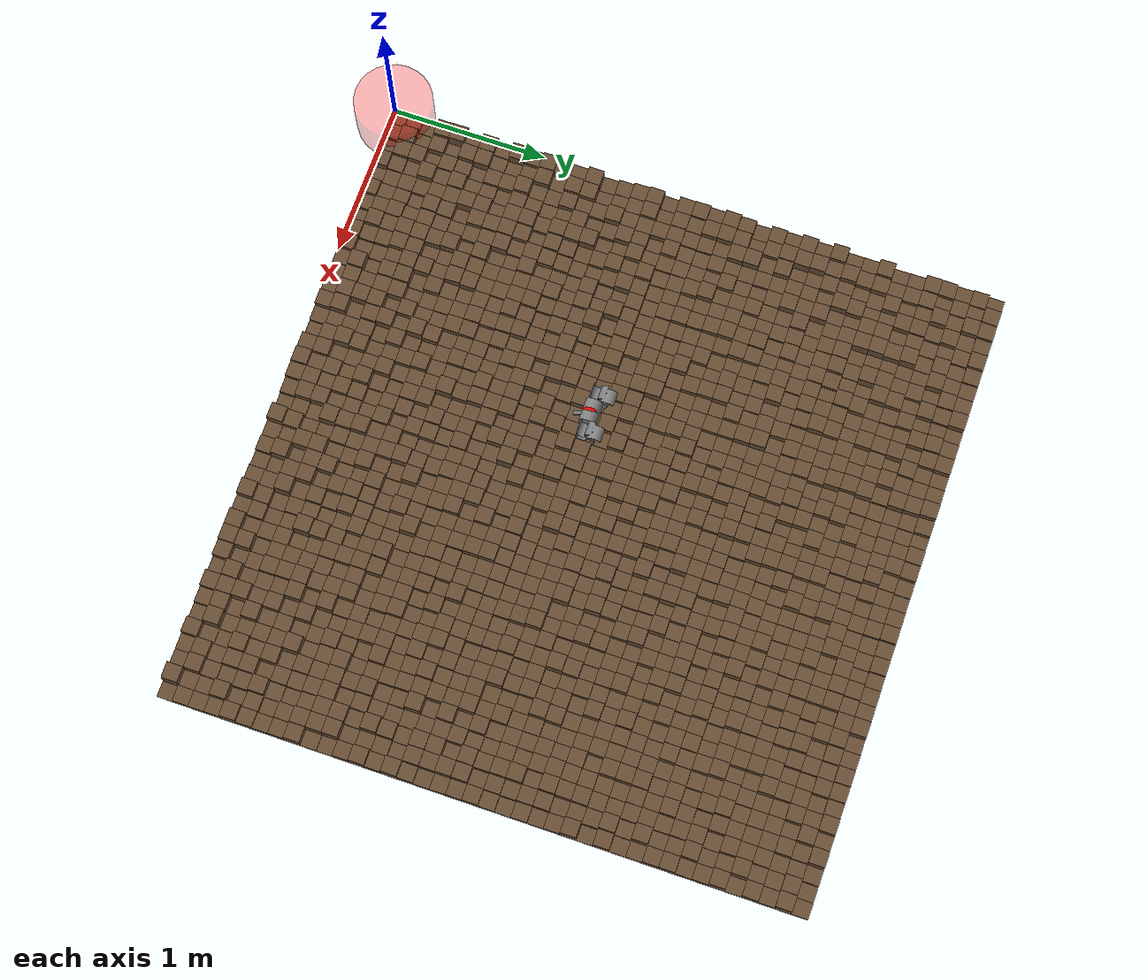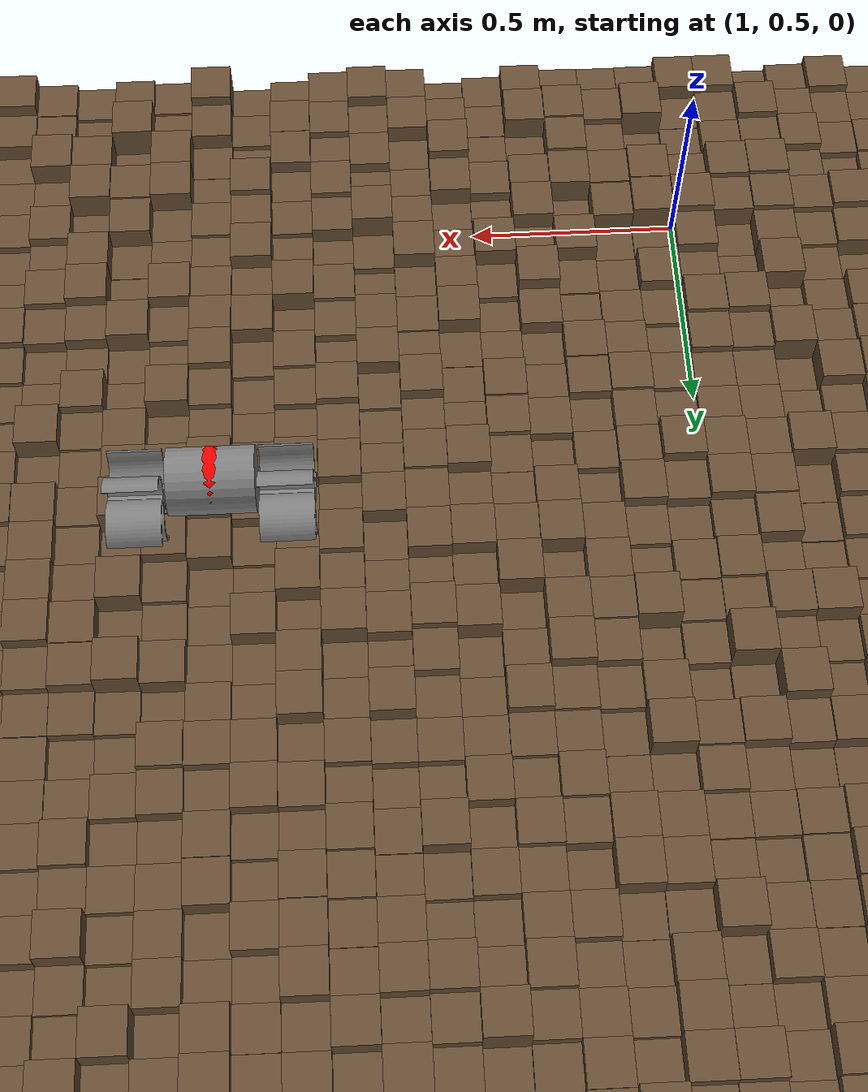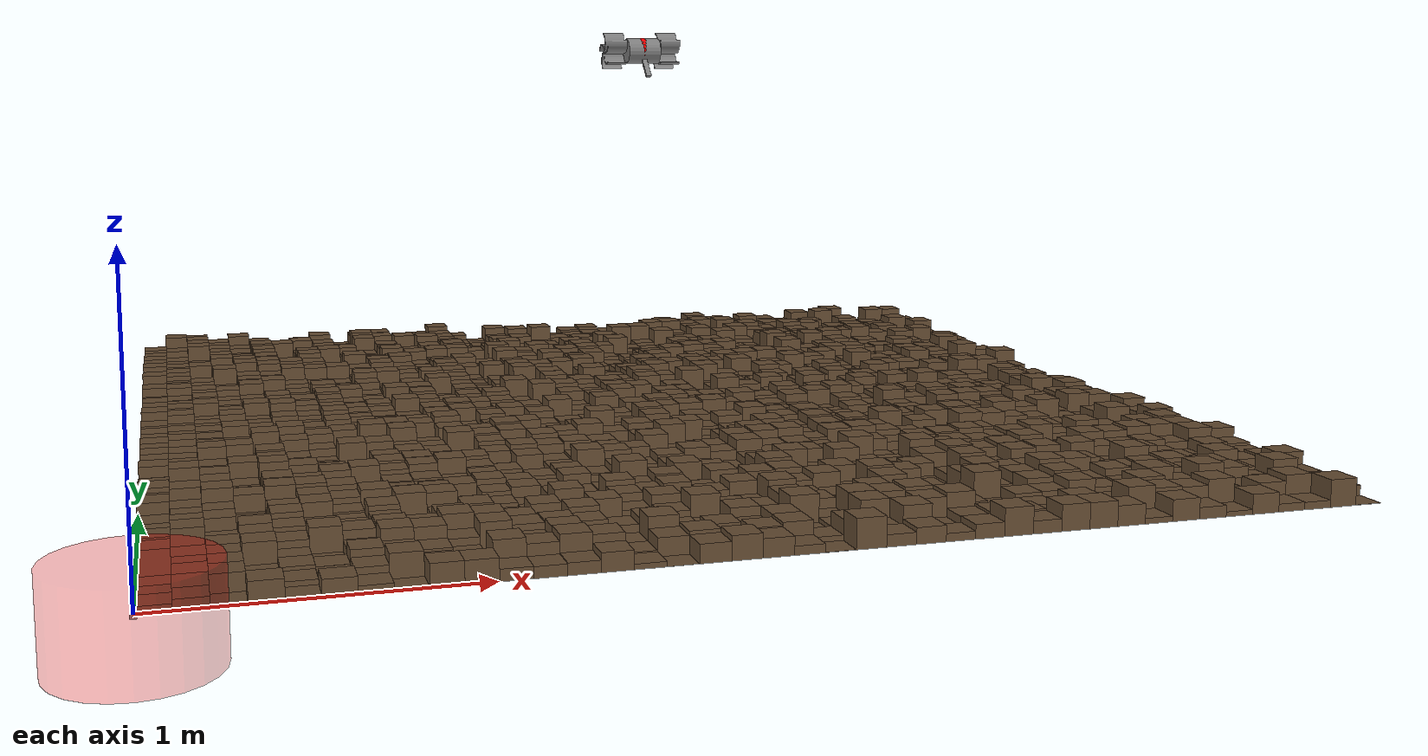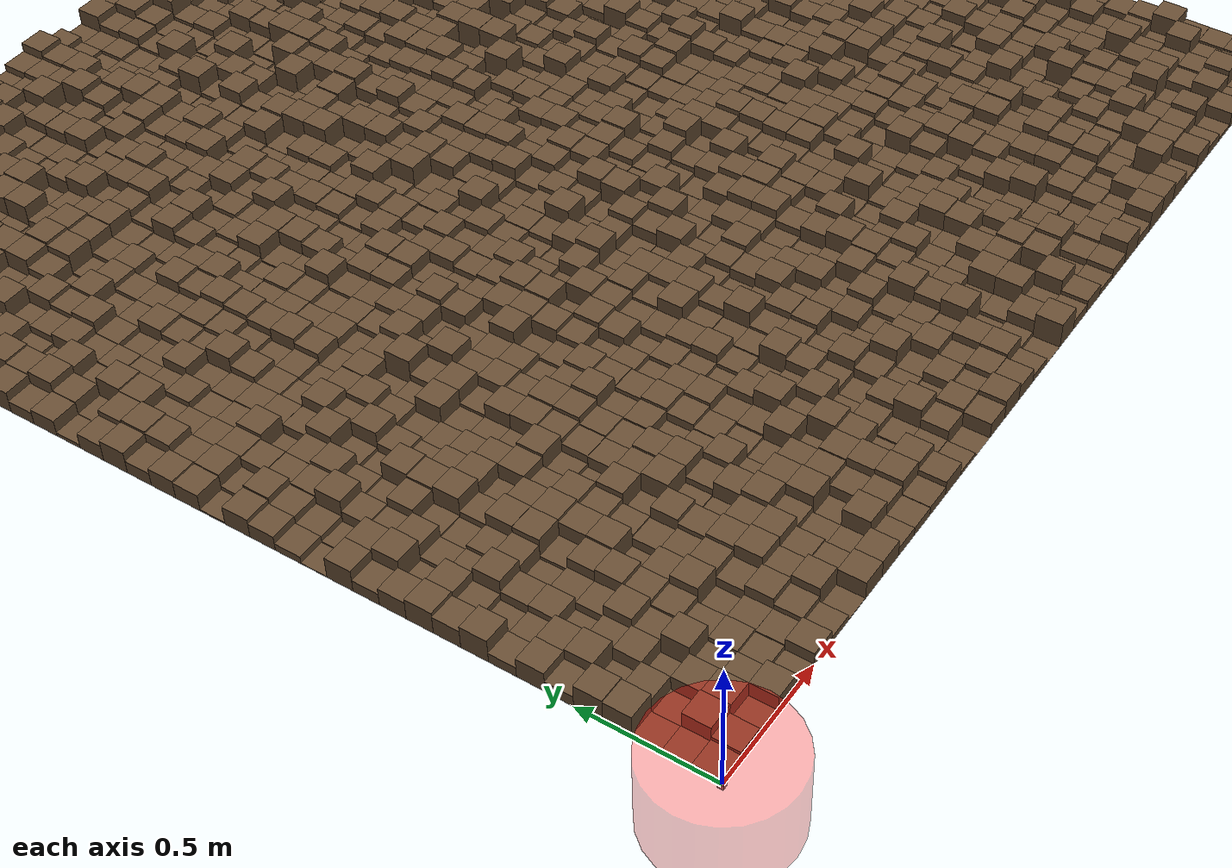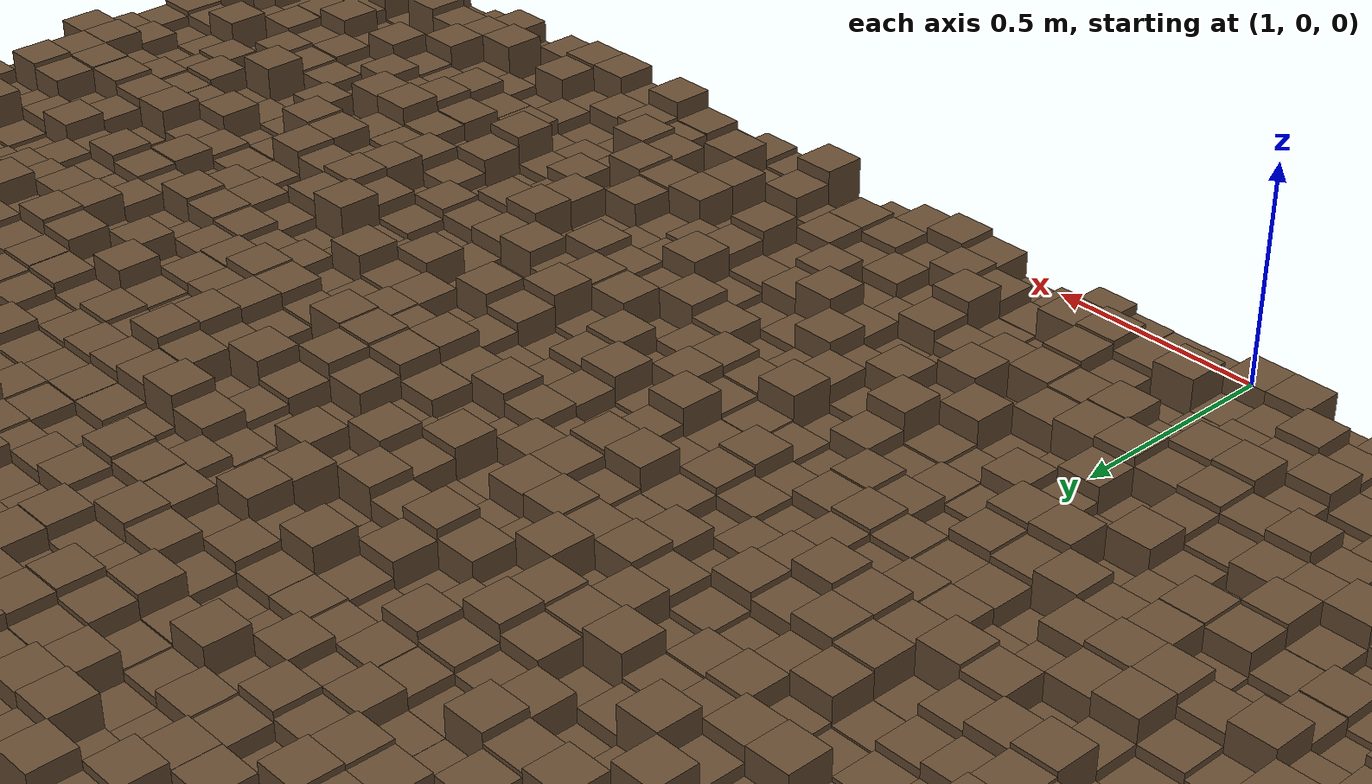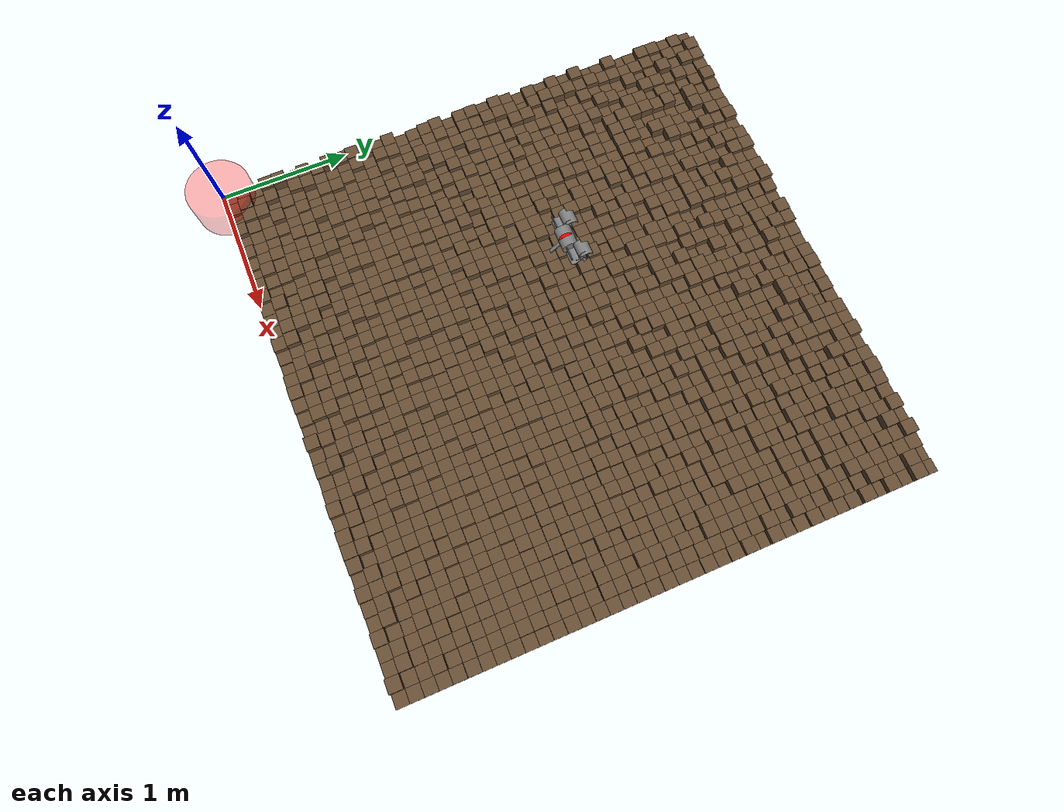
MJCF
<mujoco model="MuJoCo Model">
  <compiler angle="radian"/>

  <visual>
    <global offwidth="1024" offheight="1024"/>
    <quality shadowsize="0" numslices="36"/>
  </visual>

  <default>
    <geom type="box"/>
  </default>

  <asset>
    <texture type="2d" colorspace="auto" name="gray_field" builtin="flat" rgb1="0.5 0.5 0.5" width="100" height="100"/>
    <texture type="skybox" colorspace="auto" name="world_texture" builtin="gradient" rgb1="0 0.5 0.9" rgb2="1 1 1" width="100" height="600"/>
    <material name="field_material" texture="gray_field" reflectance="0.2"/>
    <mesh name="wheel" file="mesh/fan.stl" inertia="exact" scale="0.001 0.001 0.001"/>
  </asset>

  <worldbody>
    <geom name="floor" size="5 5 0.001" pos="5 5 0" type="plane" group="1" material="field_material" rgba="0 0 0 0"/>
    <camera name="main_cam" pos="2 -0.7 2.2" quat="0.93358 0.358368 0 0"/>
    <light name="main_light" pos="0 0 3" dir="0 0 -1" type="directional" diffuse="1.5 1.5 1.5" specular="0.1 0.1 0.1"/>
    <body name="target_body" gravcomp="1">
      <joint name="slide_x" pos="0 0 0" axis="1 0 0" type="slide"/>
      <joint name="slide_y" pos="0 0 0" axis="0 1 0" type="slide"/>
      <joint name="slide_z" pos="0 0 0" axis="0 0 1" type="slide"/>
      <geom name="target_box" size="0.01 0.01 0.01" contype="0" conaffinity="0"/>
      <site name="target" pos="0 0 0" size="0.25 0.15" type="cylinder" rgba="1 0 0 0.3"/>
    </body>
    <body name="2wheel_rover" pos="2 2 1.5">
      <joint name="body_free_joint" type="free" damping="1"/>
      <geom name="stabilizer" size="0.01 0.07 0.005" pos="0 -0.049497 -0.049497" quat="0.92388 0.382683 0 0" group="2" mass="0.2"/>
      <site name="marker" pos="0 -0.0005 0.001" size="0.05" rgba="1 0 0 1"/>
      <site name="IMU" pos="0 0 0" size="0.01" rgba="1 0 1 1"/>
      <site name="GYRO" pos="0 0 0" size="0.01" rgba="0 1 1 1"/>
      <site name="VELOCITY" pos="0 0 0" size="0.01" rgba="0 1 1 1"/>
      <body name="main_body">
        <geom name="main_body_geom" size="0.05 0.065" quat="0.707107 0 0.707107 0" type="cylinder" group="2" mass="0.5"/>
      </body>
      <body name="r_wheel" pos="0.07 0 0">
        <joint name="r_wheel_joint" pos="0 0 0" axis="-1 0 0" damping="0.3" frictionloss="0.01"/>
        <geom name="r_wheel_geom" pos="0 0.03 0" type="mesh" group="2" friction="1 0.1 0.1" mass="0.25" mesh="wheel"/>
      </body>
      <body name="l_wheel" pos="-0.15 0 0">
        <joint name="l_wheel_joint" pos="0 0 0" axis="-1 0 0" damping="0.3" frictionloss="0.01"/>
        <geom name="l_wheel_geom" pos="0 0.03 0" type="mesh" group="2" friction="1 0.1 0.1" mass="0.25" mesh="wheel"/>
      </body>
    </body>
    <body name="boxy terrain" pos="2 2 0">
      <geom size="0.05 0.05 0.0118982" pos="-1.95 1.95 0.0118982" group="1" friction="1 0.1 0.1" rgba="0.4 0.3 0.2 1"/>
      <geom size="0.05 0.05 0.0272115" pos="-1.95 1.85 0.0272115" group="1" friction="1 0.1 0.1" rgba="0.4 0.3 0.2 1"/>
      <geom size="0.05 0.05 0.0184978" pos="-1.95 1.75 0.0184978" group="1" friction="1 0.1 0.1" rgba="0.4 0.3 0.2 1"/>
      <geom size="0.05 0.05 0.030196" pos="-1.95 1.65 0.030196" group="1" friction="1 0.1 0.1" rgba="0.4 0.3 0.2 1"/>
      <geom size="0.05 0.05 0.031286" pos="-1.95 1.55 0.031286" group="1" friction="1 0.1 0.1" rgba="0.4 0.3 0.2 1"/>
      <geom size="0.05 0.05 0.00327644" pos="-1.95 1.45 0.00327644" group="1" friction="1 0.1 0.1" rgba="0.4 0.3 0.2 1"/>
      <geom size="0.05 0.05 0.0006584" pos="-1.95 1.35 0.0006584" group="1" friction="1 0.1 0.1" rgba="0.4 0.3 0.2 1"/>
      <geom size="0.05 0.05 0.0418735" pos="-1.95 1.25 0.0418735" group="1" friction="1 0.1 0.1" rgba="0.4 0.3 0.2 1"/>
      <geom size="0.05 0.05 0.0129677" pos="-1.95 1.15 0.0129677" group="1" friction="1 0.1 0.1" rgba="0.4 0.3 0.2 1"/>
      <geom size="0.05 0.05 0.0117165" pos="-1.95 1.05 0.0117165" group="1" friction="1 0.1 0.1" rgba="0.4 0.3 0.2 1"/>
      <geom size="0.05 0.05 0.0497822" pos="-1.95 0.95 0.0497822" group="1" friction="1 0.1 0.1" rgba="0.4 0.3 0.2 1"/>
      <geom size="0.05 0.05 0.0235132" pos="-1.95 0.85 0.0235132" group="1" friction="1 0.1 0.1" rgba="0.4 0.3 0.2 1"/>
      <geom size="0.05 0.05 0.0418231" pos="-1.95 0.75 0.0418231" group="1" friction="1 0.1 0.1" rgba="0.4 0.3 0.2 1"/>
      <geom size="0.05 0.05 0.0238177" pos="-1.95 0.65 0.0238177" group="1" friction="1 0.1 0.1" rgba="0.4 0.3 0.2 1"/>
      <geom size="0.05 0.05 0.0319534" pos="-1.95 0.55 0.0319534" group="1" friction="1 0.1 0.1" rgba="0.4 0.3 0.2 1"/>
      <geom size="0.05 0.05 0.00753082" pos="-1.95 0.45 0.00753082" group="1" friction="1 0.1 0.1" rgba="0.4 0.3 0.2 1"/>
      <geom size="0.05 0.05 0.031743" pos="-1.95 0.35 0.031743" group="1" friction="1 0.1 0.1" rgba="0.4 0.3 0.2 1"/>
      <geom size="0.05 0.05 0.0434023" pos="-1.95 0.25 0.0434023" group="1" friction="1 0.1 0.1" rgba="0.4 0.3 0.2 1"/>
      <geom size="0.05 0.05 0.0261591" pos="-1.95 0.15 0.0261591" group="1" friction="1 0.1 0.1" rgba="0.4 0.3 0.2 1"/>
      <geom size="0.05 0.05 0.0370626" pos="-1.95 0.05 0.0370626" group="1" friction="1 0.1 0.1" rgba="0.4 0.3 0.2 1"/>
      <geom size="0.05 0.05 0.0335706" pos="-1.95 -0.05 0.0335706" group="1" friction="1 0.1 0.1" rgba="0.4 0.3 0.2 1"/>
      <geom size="0.05 0.05 0.00320157" pos="-1.95 -0.15 0.00320157" group="1" friction="1 0.1 0.1" rgba="0.4 0.3 0.2 1"/>
      <geom size="0.05 0.05 0.0379115" pos="-1.95 -0.25 0.0379115" group="1" friction="1 0.1 0.1" rgba="0.4 0.3 0.2 1"/>
      <geom size="0.05 0.05 0.029555" pos="-1.95 -0.35 0.029555" group="1" friction="1 0.1 0.1" rgba="0.4 0.3 0.2 1"/>
      <geom size="0.05 0.05 0.0150634" pos="-1.95 -0.45 0.0150634" group="1" friction="1 0.1 0.1" rgba="0.4 0.3 0.2 1"/>
      <geom size="0.05 0.05 0.00155059" pos="-1.95 -0.55 0.00155059" group="1" friction="1 0.1 0.1" rgba="0.4 0.3 0.2 1"/>
      <geom size="0.05 0.05 0.0432764" pos="-1.95 -0.65 0.0432764" group="1" friction="1 0.1 0.1" rgba="0.4 0.3 0.2 1"/>
      <geom size="0.05 0.05 0.0236375" pos="-1.95 -0.75 0.0236375" group="1" friction="1 0.1 0.1" rgba="0.4 0.3 0.2 1"/>
      <geom size="0.05 0.05 0.0359412" pos="-1.95 -0.85 0.0359412" group="1" friction="1 0.1 0.1" rgba="0.4 0.3 0.2 1"/>
      <geom size="0.05 0.05 0.0439406" pos="-1.95 -0.95 0.0439406" group="1" friction="1 0.1 0.1" rgba="0.4 0.3 0.2 1"/>
      <geom size="0.05 0.05 0.0357065" pos="-1.95 -1.05 0.0357065" group="1" friction="1 0.1 0.1" rgba="0.4 0.3 0.2 1"/>
      <geom size="0.05 0.05 0.0460549" pos="-1.95 -1.15 0.0460549" group="1" friction="1 0.1 0.1" rgba="0.4 0.3 0.2 1"/>
      <geom size="0.05 0.05 0.0197482" pos="-1.95 -1.25 0.0197482" group="1" friction="1 0.1 0.1" rgba="0.4 0.3 0.2 1"/>
      <geom size="0.05 0.05 0.0400454" pos="-1.95 -1.35 0.0400454" group="1" friction="1 0.1 0.1" rgba="0.4 0.3 0.2 1"/>
      <geom size="0.05 0.05 0.0222311" pos="-1.95 -1.45 0.0222311" group="1" friction="1 0.1 0.1" rgba="0.4 0.3 0.2 1"/>
      <geom size="0.05 0.05 0.0467793" pos="-1.95 -1.55 0.0467793" group="1" friction="1 0.1 0.1" rgba="0.4 0.3 0.2 1"/>
      <geom size="0.05 0.05 0.0439433" pos="-1.95 -1.65 0.0439433" group="1" friction="1 0.1 0.1" rgba="0.4 0.3 0.2 1"/>
      <geom size="0.05 0.05 0.00487272" pos="-1.95 -1.75 0.00487272" group="1" friction="1 0.1 0.1" rgba="0.4 0.3 0.2 1"/>
      <geom size="0.05 0.05 0.00679844" pos="-1.95 -1.85 0.00679844" group="1" friction="1 0.1 0.1" rgba="0.4 0.3 0.2 1"/>
      <geom size="0.05 0.05 0.0108493" pos="-1.95 -1.95 0.0108493" group="1" friction="1 0.1 0.1" rgba="0.4 0.3 0.2 1"/>
      <geom size="0.05 0.05 0.048274" pos="-1.85 1.95 0.048274" group="1" friction="1 0.1 0.1" rgba="0.4 0.3 0.2 1"/>
      <geom size="0.05 0.05 0.0218081" pos="-1.85 1.85 0.0218081" group="1" friction="1 0.1 0.1" rgba="0.4 0.3 0.2 1"/>
      <geom size="0.05 0.05 0.0313324" pos="-1.85 1.75 0.0313324" group="1" friction="1 0.1 0.1" rgba="0.4 0.3 0.2 1"/>
      <geom size="0.05 0.05 0.0150513" pos="-1.85 1.65 0.0150513" group="1" friction="1 0.1 0.1" rgba="0.4 0.3 0.2 1"/>
      <geom size="0.05 0.05 0.0253621" pos="-1.85 1.55 0.0253621" group="1" friction="1 0.1 0.1" rgba="0.4 0.3 0.2 1"/>
      <geom size="0.05 0.05 0.0192933" pos="-1.85 1.45 0.0192933" group="1" friction="1 0.1 0.1" rgba="0.4 0.3 0.2 1"/>
      <geom size="0.05 0.05 0.0175455" pos="-1.85 1.35 0.0175455" group="1" friction="1 0.1 0.1" rgba="0.4 0.3 0.2 1"/>
      <geom size="0.05 0.05 0.0292537" pos="-1.85 1.25 0.0292537" group="1" friction="1 0.1 0.1" rgba="0.4 0.3 0.2 1"/>
      <geom size="0.05 0.05 0.0292126" pos="-1.85 1.15 0.0292126" group="1" friction="1 0.1 0.1" rgba="0.4 0.3 0.2 1"/>
      <geom size="0.05 0.05 0.0452101" pos="-1.85 1.05 0.0452101" group="1" friction="1 0.1 0.1" rgba="0.4 0.3 0.2 1"/>
      <geom size="0.05 0.05 0.0340991" pos="-1.85 0.95 0.0340991" group="1" friction="1 0.1 0.1" rgba="0.4 0.3 0.2 1"/>
      <geom size="0.05 0.05 0.0464473" pos="-1.85 0.85 0.0464473" group="1" friction="1 0.1 0.1" rgba="0.4 0.3 0.2 1"/>
      <geom size="0.05 0.05 0.04282" pos="-1.85 0.75 0.04282" group="1" friction="1 0.1 0.1" rgba="0.4 0.3 0.2 1"/>
      <geom size="0.05 0.05 0.0495495" pos="-1.85 0.65 0.0495495" group="1" friction="1 0.1 0.1" rgba="0.4 0.3 0.2 1"/>
      <geom size="0.05 0.05 0.0335637" pos="-1.85 0.55 0.0335637" group="1" friction="1 0.1 0.1" rgba="0.4 0.3 0.2 1"/>
      <geom size="0.05 0.05 0.00815498" pos="-1.85 0.45 0.00815498" group="1" friction="1 0.1 0.1" rgba="0.4 0.3 0.2 1"/>
      <geom size="0.05 0.05 0.0430319" pos="-1.85 0.35 0.0430319" group="1" friction="1 0.1 0.1" rgba="0.4 0.3 0.2 1"/>
      <geom size="0.05 0.05 0.0482316" pos="-1.85 0.25 0.0482316" group="1" friction="1 0.1 0.1" rgba="0.4 0.3 0.2 1"/>
      <geom size="0.05 0.05 0.0452348" pos="-1.85 0.15 0.0452348" group="1" friction="1 0.1 0.1" rgba="0.4 0.3 0.2 1"/>
      <geom size="0.05 0.05 0.0284554" pos="-1.85 0.05 0.0284554" group="1" friction="1 0.1 0.1" rgba="0.4 0.3 0.2 1"/>
      <geom size="0.05 0.05 0.0356909" pos="-1.85 -0.05 0.0356909" group="1" friction="1 0.1 0.1" rgba="0.4 0.3 0.2 1"/>
      <geom size="0.05 0.05 0.0105562" pos="-1.85 -0.15 0.0105562" group="1" friction="1 0.1 0.1" rgba="0.4 0.3 0.2 1"/>
      <geom size="0.05 0.05 0.0415804" pos="-1.85 -0.25 0.0415804" group="1" friction="1 0.1 0.1" rgba="0.4 0.3 0.2 1"/>
      <geom size="0.05 0.05 0.0286766" pos="-1.85 -0.35 0.0286766" group="1" friction="1 0.1 0.1" rgba="0.4 0.3 0.2 1"/>
      <geom size="0.05 0.05 0.0142479" pos="-1.85 -0.45 0.0142479" group="1" friction="1 0.1 0.1" rgba="0.4 0.3 0.2 1"/>
      <geom size="0.05 0.05 0.00317303" pos="-1.85 -0.55 0.00317303" group="1" friction="1 0.1 0.1" rgba="0.4 0.3 0.2 1"/>
      <geom size="0.05 0.05 0.0426971" pos="-1.85 -0.65 0.0426971" group="1" friction="1 0.1 0.1" rgba="0.4 0.3 0.2 1"/>
      <geom size="0.05 0.05 0.0494903" pos="-1.85 -0.75 0.0494903" group="1" friction="1 0.1 0.1" rgba="0.4 0.3 0.2 1"/>
      <geom size="0.05 0.05 0.0044259" pos="-1.85 -0.85 0.0044259" group="1" friction="1 0.1 0.1" rgba="0.4 0.3 0.2 1"/>
      <geom size="0.05 0.05 0.0400298" pos="-1.85 -0.95 0.0400298" group="1" friction="1 0.1 0.1" rgba="0.4 0.3 0.2 1"/>
      <geom size="0.05 0.05 0.0205231" pos="-1.85 -1.05 0.0205231" group="1" friction="1 0.1 0.1" rgba="0.4 0.3 0.2 1"/>
      <geom size="0.05 0.05 0.00753827" pos="-1.85 -1.15 0.00753827" group="1" friction="1 0.1 0.1" rgba="0.4 0.3 0.2 1"/>
      <geom size="0.05 0.05 0.0146946" pos="-1.85 -1.25 0.0146946" group="1" friction="1 0.1 0.1" rgba="0.4 0.3 0.2 1"/>
      <geom size="0.05 0.05 0.0384396" pos="-1.85 -1.35 0.0384396" group="1" friction="1 0.1 0.1" rgba="0.4 0.3 0.2 1"/>
      <geom size="0.05 0.05 0.0436384" pos="-1.85 -1.45 0.0436384" group="1" friction="1 0.1 0.1" rgba="0.4 0.3 0.2 1"/>
      <geom size="0.05 0.05 0.0022095" pos="-1.85 -1.55 0.0022095" group="1" friction="1 0.1 0.1" rgba="0.4 0.3 0.2 1"/>
      <geom size="0.05 0.05 0.0307266" pos="-1.85 -1.65 0.0307266" group="1" friction="1 0.1 0.1" rgba="0.4 0.3 0.2 1"/>
      <geom size="0.05 0.05 0.00224701" pos="-1.85 -1.75 0.00224701" group="1" friction="1 0.1 0.1" rgba="0.4 0.3 0.2 1"/>
      <geom size="0.05 0.05 0.035922" pos="-1.85 -1.85 0.035922" group="1" friction="1 0.1 0.1" rgba="0.4 0.3 0.2 1"/>
      <geom size="0.05 0.05 0.0165477" pos="-1.85 -1.95 0.0165477" group="1" friction="1 0.1 0.1" rgba="0.4 0.3 0.2 1"/>
      <geom size="0.05 0.05 0.0440453" pos="-1.75 1.95 0.0440453" group="1" friction="1 0.1 0.1" rgba="0.4 0.3 0.2 1"/>
      <geom size="0.05 0.05 0.0490318" pos="-1.75 1.85 0.0490318" group="1" friction="1 0.1 0.1" rgba="0.4 0.3 0.2 1"/>
      <geom size="0.05 0.05 0.025271" pos="-1.75 1.75 0.025271" group="1" friction="1 0.1 0.1" rgba="0.4 0.3 0.2 1"/>
      <geom size="0.05 0.05 0.0499254" pos="-1.75 1.65 0.0499254" group="1" friction="1 0.1 0.1" rgba="0.4 0.3 0.2 1"/>
      <geom size="0.05 0.05 0.0154835" pos="-1.75 1.55 0.0154835" group="1" friction="1 0.1 0.1" rgba="0.4 0.3 0.2 1"/>
      <geom size="0.05 0.05 0.00384854" pos="-1.75 1.45 0.00384854" group="1" friction="1 0.1 0.1" rgba="0.4 0.3 0.2 1"/>
      <geom size="0.05 0.05 0.0299881" pos="-1.75 1.35 0.0299881" group="1" friction="1 0.1 0.1" rgba="0.4 0.3 0.2 1"/>
      <geom size="0.05 0.05 0.00156889" pos="-1.75 1.25 0.00156889" group="1" friction="1 0.1 0.1" rgba="0.4 0.3 0.2 1"/>
      <geom size="0.05 0.05 0.00986924" pos="-1.75 1.15 0.00986924" group="1" friction="1 0.1 0.1" rgba="0.4 0.3 0.2 1"/>
      <geom size="0.05 0.05 0.0203968" pos="-1.75 1.05 0.0203968" group="1" friction="1 0.1 0.1" rgba="0.4 0.3 0.2 1"/>
      <geom size="0.05 0.05 0.0305234" pos="-1.75 0.95 0.0305234" group="1" friction="1 0.1 0.1" rgba="0.4 0.3 0.2 1"/>
      <geom size="0.05 0.05 0.00780995" pos="-1.75 0.85 0.00780995" group="1" friction="1 0.1 0.1" rgba="0.4 0.3 0.2 1"/>
      <geom size="0.05 0.05 0.00212179" pos="-1.75 0.75 0.00212179" group="1" friction="1 0.1 0.1" rgba="0.4 0.3 0.2 1"/>
      <geom size="0.05 0.05 0.043389" pos="-1.75 0.65 0.043389" group="1" friction="1 0.1 0.1" rgba="0.4 0.3 0.2 1"/>
      <geom size="0.05 0.05 0.0156915" pos="-1.75 0.55 0.0156915" group="1" friction="1 0.1 0.1" rgba="0.4 0.3 0.2 1"/>
      <geom size="0.05 0.05 0.047933" pos="-1.75 0.45 0.047933" group="1" friction="1 0.1 0.1" rgba="0.4 0.3 0.2 1"/>
      <geom size="0.05 0.05 0.044833" pos="-1.75 0.35 0.044833" group="1" friction="1 0.1 0.1" rgba="0.4 0.3 0.2 1"/>
      <geom size="0.05 0.05 0.0188895" pos="-1.75 0.25 0.0188895" group="1" friction="1 0.1 0.1" rgba="0.4 0.3 0.2 1"/>
      <geom size="0.05 0.05 0.0230205" pos="-1.75 0.15 0.0230205" group="1" friction="1 0.1 0.1" rgba="0.4 0.3 0.2 1"/>
      <geom size="0.05 0.05 0.0260036" pos="-1.75 0.05 0.0260036" group="1" friction="1 0.1 0.1" rgba="0.4 0.3 0.2 1"/>
      <geom size="0.05 0.05 0.0321944" pos="-1.75 -0.05 0.0321944" group="1" friction="1 0.1 0.1" rgba="0.4 0.3 0.2 1"/>
      <geom size="0.05 0.05 0.0297825" pos="-1.75 -0.15 0.0297825" group="1" friction="1 0.1 0.1" rgba="0.4 0.3 0.2 1"/>
      <geom size="0.05 0.05 0.0279631" pos="-1.75 -0.25 0.0279631" group="1" friction="1 0.1 0.1" rgba="0.4 0.3 0.2 1"/>
      <geom size="0.05 0.05 0.0310063" pos="-1.75 -0.35 0.0310063" group="1" friction="1 0.1 0.1" rgba="0.4 0.3 0.2 1"/>
      <geom size="0.05 0.05 0.0470311" pos="-1.75 -0.45 0.0470311" group="1" friction="1 0.1 0.1" rgba="0.4 0.3 0.2 1"/>
      <geom size="0.05 0.05 0.0253513" pos="-1.75 -0.55 0.0253513" group="1" friction="1 0.1 0.1" rgba="0.4 0.3 0.2 1"/>
      <geom size="0.05 0.05 0.0215596" pos="-1.75 -0.65 0.0215596" group="1" friction="1 0.1 0.1" rgba="0.4 0.3 0.2 1"/>
      <geom size="0.05 0.05 0.0360156" pos="-1.75 -0.75 0.0360156" group="1" friction="1 0.1 0.1" rgba="0.4 0.3 0.2 1"/>
      <geom size="0.05 0.05 0.0118818" pos="-1.75 -0.85 0.0118818" group="1" friction="1 0.1 0.1" rgba="0.4 0.3 0.2 1"/>
      <geom size="0.05 0.05 0.0150543" pos="-1.75 -0.95 0.0150543" group="1" friction="1 0.1 0.1" rgba="0.4 0.3 0.2 1"/>
      <geom size="0.05 0.05 0.0488899" pos="-1.75 -1.05 0.0488899" group="1" friction="1 0.1 0.1" rgba="0.4 0.3 0.2 1"/>
      <geom size="0.05 0.05 0.0260564" pos="-1.75 -1.15 0.0260564" group="1" friction="1 0.1 0.1" rgba="0.4 0.3 0.2 1"/>
      <geom size="0.05 0.05 0.0274215" pos="-1.75 -1.25 0.0274215" group="1" friction="1 0.1 0.1" rgba="0.4 0.3 0.2 1"/>
      <geom size="0.05 0.05 0.000572874" pos="-1.75 -1.35 0.000572874" group="1" friction="1 0.1 0.1" rgba="0.4 0.3 0.2 1"/>
      <geom size="0.05 0.05 0.0207605" pos="-1.75 -1.45 0.0207605" group="1" friction="1 0.1 0.1" rgba="0.4 0.3 0.2 1"/>
      <geom size="0.05 0.05 0.0289983" pos="-1.75 -1.55 0.0289983" group="1" friction="1 0.1 0.1" rgba="0.4 0.3 0.2 1"/>
      <geom size="0.05 0.05 0.00100264" pos="-1.75 -1.65 0.00100264" group="1" friction="1 0.1 0.1" rgba="0.4 0.3 0.2 1"/>
      <geom size="0.05 0.05 0.0307899" pos="-1.75 -1.75 0.0307899" group="1" friction="1 0.1 0.1" rgba="0.4 0.3 0.2 1"/>
      <geom size="0.05 0.05 0.031609" pos="-1.75 -1.85 0.031609" group="1" friction="1 0.1 0.1" rgba="0.4 0.3 0.2 1"/>
      <geom size="0.05 0.05 0.00300403" pos="-1.75 -1.95 0.00300403" group="1" friction="1 0.1 0.1" rgba="0.4 0.3 0.2 1"/>
      <geom size="0.05 0.05 0.0313671" pos="-1.65 1.95 0.0313671" group="1" friction="1 0.1 0.1" rgba="0.4 0.3 0.2 1"/>
      <geom size="0.05 0.05 0.0233125" pos="-1.65 1.85 0.0233125" group="1" friction="1 0.1 0.1" rgba="0.4 0.3 0.2 1"/>
      <geom size="0.05 0.05 0.0339641" pos="-1.65 1.75 0.0339641" group="1" friction="1 0.1 0.1" rgba="0.4 0.3 0.2 1"/>
      <geom size="0.05 0.05 0.0176288" pos="-1.65 1.65 0.0176288" group="1" friction="1 0.1 0.1" rgba="0.4 0.3 0.2 1"/>
      <geom size="0.05 0.05 0.0353475" pos="-1.65 1.55 0.0353475" group="1" friction="1 0.1 0.1" rgba="0.4 0.3 0.2 1"/>
      <geom size="0.05 0.05 0.0369017" pos="-1.65 1.45 0.0369017" group="1" friction="1 0.1 0.1" rgba="0.4 0.3 0.2 1"/>
      <geom size="0.05 0.05 0.00110912" pos="-1.65 1.35 0.00110912" group="1" friction="1 0.1 0.1" rgba="0.4 0.3 0.2 1"/>
      <geom size="0.05 0.05 0.00302884" pos="-1.65 1.25 0.00302884" group="1" friction="1 0.1 0.1" rgba="0.4 0.3 0.2 1"/>
      <geom size="0.05 0.05 0.033801" pos="-1.65 1.15 0.033801" group="1" friction="1 0.1 0.1" rgba="0.4 0.3 0.2 1"/>
      <geom size="0.05 0.05 0.0481653" pos="-1.65 1.05 0.0481653" group="1" friction="1 0.1 0.1" rgba="0.4 0.3 0.2 1"/>
      <geom size="0.05 0.05 0.0125561" pos="-1.65 0.95 0.0125561" group="1" friction="1 0.1 0.1" rgba="0.4 0.3 0.2 1"/>
      <geom size="0.05 0.05 0.0228156" pos="-1.65 0.85 0.0228156" group="1" friction="1 0.1 0.1" rgba="0.4 0.3 0.2 1"/>
      <geom size="0.05 0.05 0.0296336" pos="-1.65 0.75 0.0296336" group="1" friction="1 0.1 0.1" rgba="0.4 0.3 0.2 1"/>
      <geom size="0.05 0.05 0.0160013" pos="-1.65 0.65 0.0160013" group="1" friction="1 0.1 0.1" rgba="0.4 0.3 0.2 1"/>
      <geom size="0.05 0.05 0.0181978" pos="-1.65 0.55 0.0181978" group="1" friction="1 0.1 0.1" rgba="0.4 0.3 0.2 1"/>
      <geom size="0.05 0.05 0.0156335" pos="-1.65 0.45 0.0156335" group="1" friction="1 0.1 0.1" rgba="0.4 0.3 0.2 1"/>
      <geom size="0.05 0.05 0.0184577" pos="-1.65 0.35 0.0184577" group="1" friction="1 0.1 0.1" rgba="0.4 0.3 0.2 1"/>
      <geom size="0.05 0.05 0.0297811" pos="-1.65 0.25 0.0297811" group="1" friction="1 0.1 0.1" rgba="0.4 0.3 0.2 1"/>
      <geom size="0.05 0.05 0.0150202" pos="-1.65 0.15 0.0150202" group="1" friction="1 0.1 0.1" rgba="0.4 0.3 0.2 1"/>
      <geom size="0.05 0.05 0.018858" pos="-1.65 0.05 0.018858" group="1" friction="1 0.1 0.1" rgba="0.4 0.3 0.2 1"/>
      <geom size="0.05 0.05 0.0386137" pos="-1.65 -0.05 0.0386137" group="1" friction="1 0.1 0.1" rgba="0.4 0.3 0.2 1"/>
      <geom size="0.05 0.05 0.00134606" pos="-1.65 -0.15 0.00134606" group="1" friction="1 0.1 0.1" rgba="0.4 0.3 0.2 1"/>
      <geom size="0.05 0.05 0.0284629" pos="-1.65 -0.25 0.0284629" group="1" friction="1 0.1 0.1" rgba="0.4 0.3 0.2 1"/>
      <geom size="0.05 0.05 0.0367587" pos="-1.65 -0.35 0.0367587" group="1" friction="1 0.1 0.1" rgba="0.4 0.3 0.2 1"/>
      <geom size="0.05 0.05 0.0155008" pos="-1.65 -0.45 0.0155008" group="1" friction="1 0.1 0.1" rgba="0.4 0.3 0.2 1"/>
      <geom size="0.05 0.05 0.0111269" pos="-1.65 -0.55 0.0111269" group="1" friction="1 0.1 0.1" rgba="0.4 0.3 0.2 1"/>
      <geom size="0.05 0.05 0.0401904" pos="-1.65 -0.65 0.0401904" group="1" friction="1 0.1 0.1" rgba="0.4 0.3 0.2 1"/>
      <geom size="0.05 0.05 0.0119348" pos="-1.65 -0.75 0.0119348" group="1" friction="1 0.1 0.1" rgba="0.4 0.3 0.2 1"/>
      <geom size="0.05 0.05 0.00936972" pos="-1.65 -0.85 0.00936972" group="1" friction="1 0.1 0.1" rgba="0.4 0.3 0.2 1"/>
      <geom size="0.05 0.05 0.0217617" pos="-1.65 -0.95 0.0217617" group="1" friction="1 0.1 0.1" rgba="0.4 0.3 0.2 1"/>
      <geom size="0.05 0.05 0.0349033" pos="-1.65 -1.05 0.0349033" group="1" friction="1 0.1 0.1" rgba="0.4 0.3 0.2 1"/>
      <geom size="0.05 0.05 0.00509208" pos="-1.65 -1.15 0.00509208" group="1" friction="1 0.1 0.1" rgba="0.4 0.3 0.2 1"/>
      <geom size="0.05 0.05 0.0160983" pos="-1.65 -1.25 0.0160983" group="1" friction="1 0.1 0.1" rgba="0.4 0.3 0.2 1"/>
      <geom size="0.05 0.05 0.0166877" pos="-1.65 -1.35 0.0166877" group="1" friction="1 0.1 0.1" rgba="0.4 0.3 0.2 1"/>
      <geom size="0.05 0.05 0.0416769" pos="-1.65 -1.45 0.0416769" group="1" friction="1 0.1 0.1" rgba="0.4 0.3 0.2 1"/>
      <geom size="0.05 0.05 0.0219215" pos="-1.65 -1.55 0.0219215" group="1" friction="1 0.1 0.1" rgba="0.4 0.3 0.2 1"/>
      <geom size="0.05 0.05 0.0427768" pos="-1.65 -1.65 0.0427768" group="1" friction="1 0.1 0.1" rgba="0.4 0.3 0.2 1"/>
      <geom size="0.05 0.05 0.00846421" pos="-1.65 -1.75 0.00846421" group="1" friction="1 0.1 0.1" rgba="0.4 0.3 0.2 1"/>
      <geom size="0.05 0.05 0.0168355" pos="-1.65 -1.85 0.0168355" group="1" friction="1 0.1 0.1" rgba="0.4 0.3 0.2 1"/>
      <geom size="0.05 0.05 0.0325116" pos="-1.65 -1.95 0.0325116" group="1" friction="1 0.1 0.1" rgba="0.4 0.3 0.2 1"/>
      <geom size="0.05 0.05 0.0442449" pos="-1.55 1.95 0.0442449" group="1" friction="1 0.1 0.1" rgba="0.4 0.3 0.2 1"/>
      <geom size="0.05 0.05 0.0225551" pos="-1.55 1.85 0.0225551" group="1" friction="1 0.1 0.1" rgba="0.4 0.3 0.2 1"/>
      <geom size="0.05 0.05 0.0112514" pos="-1.55 1.75 0.0112514" group="1" friction="1 0.1 0.1" rgba="0.4 0.3 0.2 1"/>
      <geom size="0.05 0.05 0.00604597" pos="-1.55 1.65 0.00604597" group="1" friction="1 0.1 0.1" rgba="0.4 0.3 0.2 1"/>
      <geom size="0.05 0.05 0.0264814" pos="-1.55 1.55 0.0264814" group="1" friction="1 0.1 0.1" rgba="0.4 0.3 0.2 1"/>
      <geom size="0.05 0.05 0.00954019" pos="-1.55 1.45 0.00954019" group="1" friction="1 0.1 0.1" rgba="0.4 0.3 0.2 1"/>
      <geom size="0.05 0.05 0.0403389" pos="-1.55 1.35 0.0403389" group="1" friction="1 0.1 0.1" rgba="0.4 0.3 0.2 1"/>
      <geom size="0.05 0.05 0.0419238" pos="-1.55 1.25 0.0419238" group="1" friction="1 0.1 0.1" rgba="0.4 0.3 0.2 1"/>
      <geom size="0.05 0.05 0.00917932" pos="-1.55 1.15 0.00917932" group="1" friction="1 0.1 0.1" rgba="0.4 0.3 0.2 1"/>
      <geom size="0.05 0.05 0.0139296" pos="-1.55 1.05 0.0139296" group="1" friction="1 0.1 0.1" rgba="0.4 0.3 0.2 1"/>
      <geom size="0.05 0.05 0.0403613" pos="-1.55 0.95 0.0403613" group="1" friction="1 0.1 0.1" rgba="0.4 0.3 0.2 1"/>
      <geom size="0.05 0.05 0.0320969" pos="-1.55 0.85 0.0320969" group="1" friction="1 0.1 0.1" rgba="0.4 0.3 0.2 1"/>
      <geom size="0.05 0.05 0.0403129" pos="-1.55 0.75 0.0403129" group="1" friction="1 0.1 0.1" rgba="0.4 0.3 0.2 1"/>
      <geom size="0.05 0.05 0.0172641" pos="-1.55 0.65 0.0172641" group="1" friction="1 0.1 0.1" rgba="0.4 0.3 0.2 1"/>
      <geom size="0.05 0.05 0.00648446" pos="-1.55 0.55 0.00648446" group="1" friction="1 0.1 0.1" rgba="0.4 0.3 0.2 1"/>
      <geom size="0.05 0.05 0.0145971" pos="-1.55 0.45 0.0145971" group="1" friction="1 0.1 0.1" rgba="0.4 0.3 0.2 1"/>
      <geom size="0.05 0.05 0.0396931" pos="-1.55 0.35 0.0396931" group="1" friction="1 0.1 0.1" rgba="0.4 0.3 0.2 1"/>
      <geom size="0.05 0.05 0.0135587" pos="-1.55 0.25 0.0135587" group="1" friction="1 0.1 0.1" rgba="0.4 0.3 0.2 1"/>
      <geom size="0.05 0.05 0.0173177" pos="-1.55 0.15 0.0173177" group="1" friction="1 0.1 0.1" rgba="0.4 0.3 0.2 1"/>
      <geom size="0.05 0.05 0.0208453" pos="-1.55 0.05 0.0208453" group="1" friction="1 0.1 0.1" rgba="0.4 0.3 0.2 1"/>
      <geom size="0.05 0.05 0.0209886" pos="-1.55 -0.05 0.0209886" group="1" friction="1 0.1 0.1" rgba="0.4 0.3 0.2 1"/>
      <geom size="0.05 0.05 0.0204761" pos="-1.55 -0.15 0.0204761" group="1" friction="1 0.1 0.1" rgba="0.4 0.3 0.2 1"/>
      <geom size="0.05 0.05 0.0460306" pos="-1.55 -0.25 0.0460306" group="1" friction="1 0.1 0.1" rgba="0.4 0.3 0.2 1"/>
      <geom size="0.05 0.05 0.00779989" pos="-1.55 -0.35 0.00779989" group="1" friction="1 0.1 0.1" rgba="0.4 0.3 0.2 1"/>
      <geom size="0.05 0.05 0.00023309" pos="-1.55 -0.45 0.00023309" group="1" friction="1 0.1 0.1" rgba="0.4 0.3 0.2 1"/>
      <geom size="0.05 0.05 0.0471634" pos="-1.55 -0.55 0.0471634" group="1" friction="1 0.1 0.1" rgba="0.4 0.3 0.2 1"/>
      <geom size="0.05 0.05 0.0439989" pos="-1.55 -0.65 0.0439989" group="1" friction="1 0.1 0.1" rgba="0.4 0.3 0.2 1"/>
      <geom size="0.05 0.05 0.0493457" pos="-1.55 -0.75 0.0493457" group="1" friction="1 0.1 0.1" rgba="0.4 0.3 0.2 1"/>
      <geom size="0.05 0.05 0.0217176" pos="-1.55 -0.85 0.0217176" group="1" friction="1 0.1 0.1" rgba="0.4 0.3 0.2 1"/>
      <geom size="0.05 0.05 0.0475081" pos="-1.55 -0.95 0.0475081" group="1" friction="1 0.1 0.1" rgba="0.4 0.3 0.2 1"/>
      <geom size="0.05 0.05 0.0463689" pos="-1.55 -1.05 0.0463689" group="1" friction="1 0.1 0.1" rgba="0.4 0.3 0.2 1"/>
      <geom size="0.05 0.05 0.0111045" pos="-1.55 -1.15 0.0111045" group="1" friction="1 0.1 0.1" rgba="0.4 0.3 0.2 1"/>
      <geom size="0.05 0.05 0.0372762" pos="-1.55 -1.25 0.0372762" group="1" friction="1 0.1 0.1" rgba="0.4 0.3 0.2 1"/>
      <geom size="0.05 0.05 0.0418349" pos="-1.55 -1.35 0.0418349" group="1" friction="1 0.1 0.1" rgba="0.4 0.3 0.2 1"/>
      <geom size="0.05 0.05 0.0331494" pos="-1.55 -1.45 0.0331494" group="1" friction="1 0.1 0.1" rgba="0.4 0.3 0.2 1"/>
      <geom size="0.05 0.05 0.0259507" pos="-1.55 -1.55 0.0259507" group="1" friction="1 0.1 0.1" rgba="0.4 0.3 0.2 1"/>
      <geom size="0.05 0.05 0.0144521" pos="-1.55 -1.65 0.0144521" group="1" friction="1 0.1 0.1" rgba="0.4 0.3 0.2 1"/>
      <geom size="0.05 0.05 0.0170534" pos="-1.55 -1.75 0.0170534" group="1" friction="1 0.1 0.1" rgba="0.4 0.3 0.2 1"/>
      <geom size="0.05 0.05 0.0113733" pos="-1.55 -1.85 0.0113733" group="1" friction="1 0.1 0.1" rgba="0.4 0.3 0.2 1"/>
      <geom size="0.05 0.05 0.00340338" pos="-1.55 -1.95 0.00340338" group="1" friction="1 0.1 0.1" rgba="0.4 0.3 0.2 1"/>
      <geom size="0.05 0.05 0.0294339" pos="-1.45 1.95 0.0294339" group="1" friction="1 0.1 0.1" rgba="0.4 0.3 0.2 1"/>
      <geom size="0.05 0.05 0.0143506" pos="-1.45 1.85 0.0143506" group="1" friction="1 0.1 0.1" rgba="0.4 0.3 0.2 1"/>
      <geom size="0.05 0.05 0.0405096" pos="-1.45 1.75 0.0405096" group="1" friction="1 0.1 0.1" rgba="0.4 0.3 0.2 1"/>
      <geom size="0.05 0.05 0.00225384" pos="-1.45 1.65 0.00225384" group="1" friction="1 0.1 0.1" rgba="0.4 0.3 0.2 1"/>
      <geom size="0.05 0.05 0.0451805" pos="-1.45 1.55 0.0451805" group="1" friction="1 0.1 0.1" rgba="0.4 0.3 0.2 1"/>
      <geom size="0.05 0.05 0.0346853" pos="-1.45 1.45 0.0346853" group="1" friction="1 0.1 0.1" rgba="0.4 0.3 0.2 1"/>
      <geom size="0.05 0.05 0.0461927" pos="-1.45 1.35 0.0461927" group="1" friction="1 0.1 0.1" rgba="0.4 0.3 0.2 1"/>
      <geom size="0.05 0.05 0.0448284" pos="-1.45 1.25 0.0448284" group="1" friction="1 0.1 0.1" rgba="0.4 0.3 0.2 1"/>
      <geom size="0.05 0.05 0.0449837" pos="-1.45 1.15 0.0449837" group="1" friction="1 0.1 0.1" rgba="0.4 0.3 0.2 1"/>
      <geom size="0.05 0.05 0.0288477" pos="-1.45 1.05 0.0288477" group="1" friction="1 0.1 0.1" rgba="0.4 0.3 0.2 1"/>
      <geom size="0.05 0.05 0.000657225" pos="-1.45 0.95 0.000657225" group="1" friction="1 0.1 0.1" rgba="0.4 0.3 0.2 1"/>
      <geom size="0.05 0.05 0.0372649" pos="-1.45 0.85 0.0372649" group="1" friction="1 0.1 0.1" rgba="0.4 0.3 0.2 1"/>
      <geom size="0.05 0.05 0.00859108" pos="-1.45 0.75 0.00859108" group="1" friction="1 0.1 0.1" rgba="0.4 0.3 0.2 1"/>
      <geom size="0.05 0.05 0.0149944" pos="-1.45 0.65 0.0149944" group="1" friction="1 0.1 0.1" rgba="0.4 0.3 0.2 1"/>
      <geom size="0.05 0.05 0.0331448" pos="-1.45 0.55 0.0331448" group="1" friction="1 0.1 0.1" rgba="0.4 0.3 0.2 1"/>
      <geom size="0.05 0.05 0.0262482" pos="-1.45 0.45 0.0262482" group="1" friction="1 0.1 0.1" rgba="0.4 0.3 0.2 1"/>
      <geom size="0.05 0.05 0.0206875" pos="-1.45 0.35 0.0206875" group="1" friction="1 0.1 0.1" rgba="0.4 0.3 0.2 1"/>
      <geom size="0.05 0.05 0.0469521" pos="-1.45 0.25 0.0469521" group="1" friction="1 0.1 0.1" rgba="0.4 0.3 0.2 1"/>
      <geom size="0.05 0.05 0.0306082" pos="-1.45 0.15 0.0306082" group="1" friction="1 0.1 0.1" rgba="0.4 0.3 0.2 1"/>
      <geom size="0.05 0.05 0.0170676" pos="-1.45 0.05 0.0170676" group="1" friction="1 0.1 0.1" rgba="0.4 0.3 0.2 1"/>
      <geom size="0.05 0.05 0.0126237" pos="-1.45 -0.05 0.0126237" group="1" friction="1 0.1 0.1" rgba="0.4 0.3 0.2 1"/>
      <geom size="0.05 0.05 0.0430832" pos="-1.45 -0.15 0.0430832" group="1" friction="1 0.1 0.1" rgba="0.4 0.3 0.2 1"/>
      <geom size="0.05 0.05 0.0238599" pos="-1.45 -0.25 0.0238599" group="1" friction="1 0.1 0.1" rgba="0.4 0.3 0.2 1"/>
      <geom size="0.05 0.05 0.0391163" pos="-1.45 -0.35 0.0391163" group="1" friction="1 0.1 0.1" rgba="0.4 0.3 0.2 1"/>
      <geom size="0.05 0.05 0.0175921" pos="-1.45 -0.45 0.0175921" group="1" friction="1 0.1 0.1" rgba="0.4 0.3 0.2 1"/>
      <geom size="0.05 0.05 0.00986668" pos="-1.45 -0.55 0.00986668" group="1" friction="1 0.1 0.1" rgba="0.4 0.3 0.2 1"/>
      <geom size="0.05 0.05 0.0267319" pos="-1.45 -0.65 0.0267319" group="1" friction="1 0.1 0.1" rgba="0.4 0.3 0.2 1"/>
      <geom size="0.05 0.05 0.0408405" pos="-1.45 -0.75 0.0408405" group="1" friction="1 0.1 0.1" rgba="0.4 0.3 0.2 1"/>
      <geom size="0.05 0.05 0.00856511" pos="-1.45 -0.85 0.00856511" group="1" friction="1 0.1 0.1" rgba="0.4 0.3 0.2 1"/>
      <geom size="0.05 0.05 0.0395836" pos="-1.45 -0.95 0.0395836" group="1" friction="1 0.1 0.1" rgba="0.4 0.3 0.2 1"/>
      <geom size="0.05 0.05 0.0460883" pos="-1.45 -1.05 0.0460883" group="1" friction="1 0.1 0.1" rgba="0.4 0.3 0.2 1"/>
      <geom size="0.05 0.05 0.0403026" pos="-1.45 -1.15 0.0403026" group="1" friction="1 0.1 0.1" rgba="0.4 0.3 0.2 1"/>
      <geom size="0.05 0.05 0.0411749" pos="-1.45 -1.25 0.0411749" group="1" friction="1 0.1 0.1" rgba="0.4 0.3 0.2 1"/>
      <geom size="0.05 0.05 0.000375236" pos="-1.45 -1.35 0.000375236" group="1" friction="1 0.1 0.1" rgba="0.4 0.3 0.2 1"/>
      <geom size="0.05 0.05 0.0314304" pos="-1.45 -1.45 0.0314304" group="1" friction="1 0.1 0.1" rgba="0.4 0.3 0.2 1"/>
      <geom size="0.05 0.05 0.0431277" pos="-1.45 -1.55 0.0431277" group="1" friction="1 0.1 0.1" rgba="0.4 0.3 0.2 1"/>
      <geom size="0.05 0.05 0.00249659" pos="-1.45 -1.65 0.00249659" group="1" friction="1 0.1 0.1" rgba="0.4 0.3 0.2 1"/>
      <geom size="0.05 0.05 0.0135699" pos="-1.45 -1.75 0.0135699" group="1" friction="1 0.1 0.1" rgba="0.4 0.3 0.2 1"/>
      <geom size="0.05 0.05 0.0134293" pos="-1.45 -1.85 0.0134293" group="1" friction="1 0.1 0.1" rgba="0.4 0.3 0.2 1"/>
      <geom size="0.05 0.05 0.0263633" pos="-1.45 -1.95 0.0263633" group="1" friction="1 0.1 0.1" rgba="0.4 0.3 0.2 1"/>
      <geom size="0.05 0.05 0.0211492" pos="-1.35 1.95 0.0211492" group="1" friction="1 0.1 0.1" rgba="0.4 0.3 0.2 1"/>
      <geom size="0.05 0.05 0.023645" pos="-1.35 1.85 0.023645" group="1" friction="1 0.1 0.1" rgba="0.4 0.3 0.2 1"/>
      <geom size="0.05 0.05 0.0388249" pos="-1.35 1.75 0.0388249" group="1" friction="1 0.1 0.1" rgba="0.4 0.3 0.2 1"/>
      <geom size="0.05 0.05 9.04325e-05" pos="-1.35 1.65 9.04325e-05" group="1" friction="1 0.1 0.1" rgba="0.4 0.3 0.2 1"/>
      <geom size="0.05 0.05 0.00274168" pos="-1.35 1.55 0.00274168" group="1" friction="1 0.1 0.1" rgba="0.4 0.3 0.2 1"/>
      <geom size="0.05 0.05 0.00634316" pos="-1.35 1.45 0.00634316" group="1" friction="1 0.1 0.1" rgba="0.4 0.3 0.2 1"/>
      <geom size="0.05 0.05 0.00623131" pos="-1.35 1.35 0.00623131" group="1" friction="1 0.1 0.1" rgba="0.4 0.3 0.2 1"/>
      <geom size="0.05 0.05 0.00342083" pos="-1.35 1.25 0.00342083" group="1" friction="1 0.1 0.1" rgba="0.4 0.3 0.2 1"/>
      <geom size="0.05 0.05 0.0487346" pos="-1.35 1.15 0.0487346" group="1" friction="1 0.1 0.1" rgba="0.4 0.3 0.2 1"/>
      <geom size="0.05 0.05 0.0427224" pos="-1.35 1.05 0.0427224" group="1" friction="1 0.1 0.1" rgba="0.4 0.3 0.2 1"/>
      <geom size="0.05 0.05 0.0043064" pos="-1.35 0.95 0.0043064" group="1" friction="1 0.1 0.1" rgba="0.4 0.3 0.2 1"/>
      <geom size="0.05 0.05 0.025106" pos="-1.35 0.85 0.025106" group="1" friction="1 0.1 0.1" rgba="0.4 0.3 0.2 1"/>
      <geom size="0.05 0.05 0.0157948" pos="-1.35 0.75 0.0157948" group="1" friction="1 0.1 0.1" rgba="0.4 0.3 0.2 1"/>
      <geom size="0.05 0.05 0.015729" pos="-1.35 0.65 0.015729" group="1" friction="1 0.1 0.1" rgba="0.4 0.3 0.2 1"/>
      <geom size="0.05 0.05 0.0175645" pos="-1.35 0.55 0.0175645" group="1" friction="1 0.1 0.1" rgba="0.4 0.3 0.2 1"/>
      <geom size="0.05 0.05 0.0323457" pos="-1.35 0.45 0.0323457" group="1" friction="1 0.1 0.1" rgba="0.4 0.3 0.2 1"/>
      <geom size="0.05 0.05 0.0293307" pos="-1.35 0.35 0.0293307" group="1" friction="1 0.1 0.1" rgba="0.4 0.3 0.2 1"/>
      <geom size="0.05 0.05 0.0180417" pos="-1.35 0.25 0.0180417" group="1" friction="1 0.1 0.1" rgba="0.4 0.3 0.2 1"/>
      <geom size="0.05 0.05 0.0095541" pos="-1.35 0.15 0.0095541" group="1" friction="1 0.1 0.1" rgba="0.4 0.3 0.2 1"/>
      <geom size="0.05 0.05 0.0164388" pos="-1.35 0.05 0.0164388" group="1" friction="1 0.1 0.1" rgba="0.4 0.3 0.2 1"/>
      <geom size="0.05 0.05 0.00618775" pos="-1.35 -0.05 0.00618775" group="1" friction="1 0.1 0.1" rgba="0.4 0.3 0.2 1"/>
      <geom size="0.05 0.05 0.0277763" pos="-1.35 -0.15 0.0277763" group="1" friction="1 0.1 0.1" rgba="0.4 0.3 0.2 1"/>
      <geom size="0.05 0.05 0.0358021" pos="-1.35 -0.25 0.0358021" group="1" friction="1 0.1 0.1" rgba="0.4 0.3 0.2 1"/>
      <geom size="0.05 0.05 0.0190119" pos="-1.35 -0.35 0.0190119" group="1" friction="1 0.1 0.1" rgba="0.4 0.3 0.2 1"/>
      <geom size="0.05 0.05 0.00399506" pos="-1.35 -0.45 0.00399506" group="1" friction="1 0.1 0.1" rgba="0.4 0.3 0.2 1"/>
      <geom size="0.05 0.05 0.00892781" pos="-1.35 -0.55 0.00892781" group="1" friction="1 0.1 0.1" rgba="0.4 0.3 0.2 1"/>
      <geom size="0.05 0.05 0.0186637" pos="-1.35 -0.65 0.0186637" group="1" friction="1 0.1 0.1" rgba="0.4 0.3 0.2 1"/>
      <geom size="0.05 0.05 0.0302217" pos="-1.35 -0.75 0.0302217" group="1" friction="1 0.1 0.1" rgba="0.4 0.3 0.2 1"/>
      <geom size="0.05 0.05 0.0391311" pos="-1.35 -0.85 0.0391311" group="1" friction="1 0.1 0.1" rgba="0.4 0.3 0.2 1"/>
      <geom size="0.05 0.05 0.0190132" pos="-1.35 -0.95 0.0190132" group="1" friction="1 0.1 0.1" rgba="0.4 0.3 0.2 1"/>
      <geom size="0.05 0.05 0.040058" pos="-1.35 -1.05 0.040058" group="1" friction="1 0.1 0.1" rgba="0.4 0.3 0.2 1"/>
      <geom size="0.05 0.05 0.0311463" pos="-1.35 -1.15 0.0311463" group="1" friction="1 0.1 0.1" rgba="0.4 0.3 0.2 1"/>
      <geom size="0.05 0.05 0.0215797" pos="-1.35 -1.25 0.0215797" group="1" friction="1 0.1 0.1" rgba="0.4 0.3 0.2 1"/>
      <geom size="0.05 0.05 0.018621" pos="-1.35 -1.35 0.018621" group="1" friction="1 0.1 0.1" rgba="0.4 0.3 0.2 1"/>
      <geom size="0.05 0.05 0.0248076" pos="-1.35 -1.45 0.0248076" group="1" friction="1 0.1 0.1" rgba="0.4 0.3 0.2 1"/>
      <geom size="0.05 0.05 0.035144" pos="-1.35 -1.55 0.035144" group="1" friction="1 0.1 0.1" rgba="0.4 0.3 0.2 1"/>
      <geom size="0.05 0.05 0.0210257" pos="-1.35 -1.65 0.0210257" group="1" friction="1 0.1 0.1" rgba="0.4 0.3 0.2 1"/>
      <geom size="0.05 0.05 0.0347062" pos="-1.35 -1.75 0.0347062" group="1" friction="1 0.1 0.1" rgba="0.4 0.3 0.2 1"/>
      <geom size="0.05 0.05 0.023042" pos="-1.35 -1.85 0.023042" group="1" friction="1 0.1 0.1" rgba="0.4 0.3 0.2 1"/>
      <geom size="0.05 0.05 0.0122542" pos="-1.35 -1.95 0.0122542" group="1" friction="1 0.1 0.1" rgba="0.4 0.3 0.2 1"/>
      <geom size="0.05 0.05 0.0267919" pos="-1.25 1.95 0.0267919" group="1" friction="1 0.1 0.1" rgba="0.4 0.3 0.2 1"/>
      <geom size="0.05 0.05 0.0347585" pos="-1.25 1.85 0.0347585" group="1" friction="1 0.1 0.1" rgba="0.4 0.3 0.2 1"/>
      <geom size="0.05 0.05 0.00357905" pos="-1.25 1.75 0.00357905" group="1" friction="1 0.1 0.1" rgba="0.4 0.3 0.2 1"/>
      <geom size="0.05 0.05 0.0212444" pos="-1.25 1.65 0.0212444" group="1" friction="1 0.1 0.1" rgba="0.4 0.3 0.2 1"/>
      <geom size="0.05 0.05 0.0212928" pos="-1.25 1.55 0.0212928" group="1" friction="1 0.1 0.1" rgba="0.4 0.3 0.2 1"/>
      <geom size="0.05 0.05 0.0439835" pos="-1.25 1.45 0.0439835" group="1" friction="1 0.1 0.1" rgba="0.4 0.3 0.2 1"/>
      <geom size="0.05 0.05 0.0468242" pos="-1.25 1.35 0.0468242" group="1" friction="1 0.1 0.1" rgba="0.4 0.3 0.2 1"/>
      <geom size="0.05 0.05 0.0187118" pos="-1.25 1.25 0.0187118" group="1" friction="1 0.1 0.1" rgba="0.4 0.3 0.2 1"/>
      <geom size="0.05 0.05 0.0448927" pos="-1.25 1.15 0.0448927" group="1" friction="1 0.1 0.1" rgba="0.4 0.3 0.2 1"/>
      <geom size="0.05 0.05 0.0395458" pos="-1.25 1.05 0.0395458" group="1" friction="1 0.1 0.1" rgba="0.4 0.3 0.2 1"/>
      <geom size="0.05 0.05 0.013109" pos="-1.25 0.95 0.013109" group="1" friction="1 0.1 0.1" rgba="0.4 0.3 0.2 1"/>
      <geom size="0.05 0.05 0.0232072" pos="-1.25 0.85 0.0232072" group="1" friction="1 0.1 0.1" rgba="0.4 0.3 0.2 1"/>
      <geom size="0.05 0.05 0.0061573" pos="-1.25 0.75 0.0061573" group="1" friction="1 0.1 0.1" rgba="0.4 0.3 0.2 1"/>
      <geom size="0.05 0.05 0.0406611" pos="-1.25 0.65 0.0406611" group="1" friction="1 0.1 0.1" rgba="0.4 0.3 0.2 1"/>
      <geom size="0.05 0.05 0.0331145" pos="-1.25 0.55 0.0331145" group="1" friction="1 0.1 0.1" rgba="0.4 0.3 0.2 1"/>
      <geom size="0.05 0.05 0.0443672" pos="-1.25 0.45 0.0443672" group="1" friction="1 0.1 0.1" rgba="0.4 0.3 0.2 1"/>
      <geom size="0.05 0.05 0.0396235" pos="-1.25 0.35 0.0396235" group="1" friction="1 0.1 0.1" rgba="0.4 0.3 0.2 1"/>
      <geom size="0.05 0.05 0.0333781" pos="-1.25 0.25 0.0333781" group="1" friction="1 0.1 0.1" rgba="0.4 0.3 0.2 1"/>
      <geom size="0.05 0.05 0.0366868" pos="-1.25 0.15 0.0366868" group="1" friction="1 0.1 0.1" rgba="0.4 0.3 0.2 1"/>
      <geom size="0.05 0.05 0.0281922" pos="-1.25 0.05 0.0281922" group="1" friction="1 0.1 0.1" rgba="0.4 0.3 0.2 1"/>
      <geom size="0.05 0.05 0.00515666" pos="-1.25 -0.05 0.00515666" group="1" friction="1 0.1 0.1" rgba="0.4 0.3 0.2 1"/>
      <geom size="0.05 0.05 0.0293879" pos="-1.25 -0.15 0.0293879" group="1" friction="1 0.1 0.1" rgba="0.4 0.3 0.2 1"/>
      <geom size="0.05 0.05 0.000245064" pos="-1.25 -0.25 0.000245064" group="1" friction="1 0.1 0.1" rgba="0.4 0.3 0.2 1"/>
      <geom size="0.05 0.05 0.00717592" pos="-1.25 -0.35 0.00717592" group="1" friction="1 0.1 0.1" rgba="0.4 0.3 0.2 1"/>
      <geom size="0.05 0.05 0.0387152" pos="-1.25 -0.45 0.0387152" group="1" friction="1 0.1 0.1" rgba="0.4 0.3 0.2 1"/>
      <geom size="0.05 0.05 0.00221564" pos="-1.25 -0.55 0.00221564" group="1" friction="1 0.1 0.1" rgba="0.4 0.3 0.2 1"/>
      <geom size="0.05 0.05 0.00458994" pos="-1.25 -0.65 0.00458994" group="1" friction="1 0.1 0.1" rgba="0.4 0.3 0.2 1"/>
      <geom size="0.05 0.05 0.00496498" pos="-1.25 -0.75 0.00496498" group="1" friction="1 0.1 0.1" rgba="0.4 0.3 0.2 1"/>
      <geom size="0.05 0.05 0.0440234" pos="-1.25 -0.85 0.0440234" group="1" friction="1 0.1 0.1" rgba="0.4 0.3 0.2 1"/>
      <geom size="0.05 0.05 0.00895768" pos="-1.25 -0.95 0.00895768" group="1" friction="1 0.1 0.1" rgba="0.4 0.3 0.2 1"/>
      <geom size="0.05 0.05 0.00117437" pos="-1.25 -1.05 0.00117437" group="1" friction="1 0.1 0.1" rgba="0.4 0.3 0.2 1"/>
      <geom size="0.05 0.05 0.0420768" pos="-1.25 -1.15 0.0420768" group="1" friction="1 0.1 0.1" rgba="0.4 0.3 0.2 1"/>
      <geom size="0.05 0.05 0.00606417" pos="-1.25 -1.25 0.00606417" group="1" friction="1 0.1 0.1" rgba="0.4 0.3 0.2 1"/>
      <geom size="0.05 0.05 0.0421972" pos="-1.25 -1.35 0.0421972" group="1" friction="1 0.1 0.1" rgba="0.4 0.3 0.2 1"/>
      <geom size="0.05 0.05 0.0336767" pos="-1.25 -1.45 0.0336767" group="1" friction="1 0.1 0.1" rgba="0.4 0.3 0.2 1"/>
      <geom size="0.05 0.05 0.0418091" pos="-1.25 -1.55 0.0418091" group="1" friction="1 0.1 0.1" rgba="0.4 0.3 0.2 1"/>
      <geom size="0.05 0.05 0.0476206" pos="-1.25 -1.65 0.0476206" group="1" friction="1 0.1 0.1" rgba="0.4 0.3 0.2 1"/>
      <geom size="0.05 0.05 0.0289538" pos="-1.25 -1.75 0.0289538" group="1" friction="1 0.1 0.1" rgba="0.4 0.3 0.2 1"/>
      <geom size="0.05 0.05 0.0399374" pos="-1.25 -1.85 0.0399374" group="1" friction="1 0.1 0.1" rgba="0.4 0.3 0.2 1"/>
      <geom size="0.05 0.05 0.00181346" pos="-1.25 -1.95 0.00181346" group="1" friction="1 0.1 0.1" rgba="0.4 0.3 0.2 1"/>
      <geom size="0.05 0.05 0.0383709" pos="-1.15 1.95 0.0383709" group="1" friction="1 0.1 0.1" rgba="0.4 0.3 0.2 1"/>
      <geom size="0.05 0.05 0.0255663" pos="-1.15 1.85 0.0255663" group="1" friction="1 0.1 0.1" rgba="0.4 0.3 0.2 1"/>
      <geom size="0.05 0.05 0.0357579" pos="-1.15 1.75 0.0357579" group="1" friction="1 0.1 0.1" rgba="0.4 0.3 0.2 1"/>
      <geom size="0.05 0.05 0.00533718" pos="-1.15 1.65 0.00533718" group="1" friction="1 0.1 0.1" rgba="0.4 0.3 0.2 1"/>
      <geom size="0.05 0.05 0.0374482" pos="-1.15 1.55 0.0374482" group="1" friction="1 0.1 0.1" rgba="0.4 0.3 0.2 1"/>
      <geom size="0.05 0.05 0.0467281" pos="-1.15 1.45 0.0467281" group="1" friction="1 0.1 0.1" rgba="0.4 0.3 0.2 1"/>
      <geom size="0.05 0.05 0.00305697" pos="-1.15 1.35 0.00305697" group="1" friction="1 0.1 0.1" rgba="0.4 0.3 0.2 1"/>
      <geom size="0.05 0.05 0.0162123" pos="-1.15 1.25 0.0162123" group="1" friction="1 0.1 0.1" rgba="0.4 0.3 0.2 1"/>
      <geom size="0.05 0.05 0.0281989" pos="-1.15 1.15 0.0281989" group="1" friction="1 0.1 0.1" rgba="0.4 0.3 0.2 1"/>
      <geom size="0.05 0.05 0.041403" pos="-1.15 1.05 0.041403" group="1" friction="1 0.1 0.1" rgba="0.4 0.3 0.2 1"/>
      <geom size="0.05 0.05 0.0121063" pos="-1.15 0.95 0.0121063" group="1" friction="1 0.1 0.1" rgba="0.4 0.3 0.2 1"/>
      <geom size="0.05 0.05 0.00898862" pos="-1.15 0.85 0.00898862" group="1" friction="1 0.1 0.1" rgba="0.4 0.3 0.2 1"/>
      <geom size="0.05 0.05 0.0124983" pos="-1.15 0.75 0.0124983" group="1" friction="1 0.1 0.1" rgba="0.4 0.3 0.2 1"/>
      <geom size="0.05 0.05 0.030799" pos="-1.15 0.65 0.030799" group="1" friction="1 0.1 0.1" rgba="0.4 0.3 0.2 1"/>
      <geom size="0.05 0.05 0.0376772" pos="-1.15 0.55 0.0376772" group="1" friction="1 0.1 0.1" rgba="0.4 0.3 0.2 1"/>
      <geom size="0.05 0.05 0.0196865" pos="-1.15 0.45 0.0196865" group="1" friction="1 0.1 0.1" rgba="0.4 0.3 0.2 1"/>
      <geom size="0.05 0.05 0.0183736" pos="-1.15 0.35 0.0183736" group="1" friction="1 0.1 0.1" rgba="0.4 0.3 0.2 1"/>
      <geom size="0.05 0.05 0.019832" pos="-1.15 0.25 0.019832" group="1" friction="1 0.1 0.1" rgba="0.4 0.3 0.2 1"/>
      <geom size="0.05 0.05 0.0175142" pos="-1.15 0.15 0.0175142" group="1" friction="1 0.1 0.1" rgba="0.4 0.3 0.2 1"/>
      <geom size="0.05 0.05 0.0209109" pos="-1.15 0.05 0.0209109" group="1" friction="1 0.1 0.1" rgba="0.4 0.3 0.2 1"/>
      <geom size="0.05 0.05 0.00416302" pos="-1.15 -0.05 0.00416302" group="1" friction="1 0.1 0.1" rgba="0.4 0.3 0.2 1"/>
      <geom size="0.05 0.05 0.0250155" pos="-1.15 -0.15 0.0250155" group="1" friction="1 0.1 0.1" rgba="0.4 0.3 0.2 1"/>
      <geom size="0.05 0.05 0.0486528" pos="-1.15 -0.25 0.0486528" group="1" friction="1 0.1 0.1" rgba="0.4 0.3 0.2 1"/>
      <geom size="0.05 0.05 0.0206416" pos="-1.15 -0.35 0.0206416" group="1" friction="1 0.1 0.1" rgba="0.4 0.3 0.2 1"/>
      <geom size="0.05 0.05 0.0373705" pos="-1.15 -0.45 0.0373705" group="1" friction="1 0.1 0.1" rgba="0.4 0.3 0.2 1"/>
      <geom size="0.05 0.05 0.00803102" pos="-1.15 -0.55 0.00803102" group="1" friction="1 0.1 0.1" rgba="0.4 0.3 0.2 1"/>
      <geom size="0.05 0.05 0.0345419" pos="-1.15 -0.65 0.0345419" group="1" friction="1 0.1 0.1" rgba="0.4 0.3 0.2 1"/>
      <geom size="0.05 0.05 0.0378058" pos="-1.15 -0.75 0.0378058" group="1" friction="1 0.1 0.1" rgba="0.4 0.3 0.2 1"/>
      <geom size="0.05 0.05 0.0336928" pos="-1.15 -0.85 0.0336928" group="1" friction="1 0.1 0.1" rgba="0.4 0.3 0.2 1"/>
      <geom size="0.05 0.05 0.0258546" pos="-1.15 -0.95 0.0258546" group="1" friction="1 0.1 0.1" rgba="0.4 0.3 0.2 1"/>
      <geom size="0.05 0.05 0.024186" pos="-1.15 -1.05 0.024186" group="1" friction="1 0.1 0.1" rgba="0.4 0.3 0.2 1"/>
      <geom size="0.05 0.05 0.0321477" pos="-1.15 -1.15 0.0321477" group="1" friction="1 0.1 0.1" rgba="0.4 0.3 0.2 1"/>
      <geom size="0.05 0.05 0.0448701" pos="-1.15 -1.25 0.0448701" group="1" friction="1 0.1 0.1" rgba="0.4 0.3 0.2 1"/>
      <geom size="0.05 0.05 0.00746637" pos="-1.15 -1.35 0.00746637" group="1" friction="1 0.1 0.1" rgba="0.4 0.3 0.2 1"/>
      <geom size="0.05 0.05 0.00479304" pos="-1.15 -1.45 0.00479304" group="1" friction="1 0.1 0.1" rgba="0.4 0.3 0.2 1"/>
      <geom size="0.05 0.05 0.0374077" pos="-1.15 -1.55 0.0374077" group="1" friction="1 0.1 0.1" rgba="0.4 0.3 0.2 1"/>
      <geom size="0.05 0.05 0.0458307" pos="-1.15 -1.65 0.0458307" group="1" friction="1 0.1 0.1" rgba="0.4 0.3 0.2 1"/>
      <geom size="0.05 0.05 0.0258627" pos="-1.15 -1.75 0.0258627" group="1" friction="1 0.1 0.1" rgba="0.4 0.3 0.2 1"/>
      <geom size="0.05 0.05 0.0221527" pos="-1.15 -1.85 0.0221527" group="1" friction="1 0.1 0.1" rgba="0.4 0.3 0.2 1"/>
      <geom size="0.05 0.05 0.0359455" pos="-1.15 -1.95 0.0359455" group="1" friction="1 0.1 0.1" rgba="0.4 0.3 0.2 1"/>
      <geom size="0.05 0.05 0.00930555" pos="-1.05 1.95 0.00930555" group="1" friction="1 0.1 0.1" rgba="0.4 0.3 0.2 1"/>
      <geom size="0.05 0.05 0.0133679" pos="-1.05 1.85 0.0133679" group="1" friction="1 0.1 0.1" rgba="0.4 0.3 0.2 1"/>
      <geom size="0.05 0.05 0.00995899" pos="-1.05 1.75 0.00995899" group="1" friction="1 0.1 0.1" rgba="0.4 0.3 0.2 1"/>
      <geom size="0.05 0.05 0.0292809" pos="-1.05 1.65 0.0292809" group="1" friction="1 0.1 0.1" rgba="0.4 0.3 0.2 1"/>
      <geom size="0.05 0.05 0.0157424" pos="-1.05 1.55 0.0157424" group="1" friction="1 0.1 0.1" rgba="0.4 0.3 0.2 1"/>
      <geom size="0.05 0.05 0.0116153" pos="-1.05 1.45 0.0116153" group="1" friction="1 0.1 0.1" rgba="0.4 0.3 0.2 1"/>
      <geom size="0.05 0.05 0.0345566" pos="-1.05 1.35 0.0345566" group="1" friction="1 0.1 0.1" rgba="0.4 0.3 0.2 1"/>
      <geom size="0.05 0.05 0.0476713" pos="-1.05 1.25 0.0476713" group="1" friction="1 0.1 0.1" rgba="0.4 0.3 0.2 1"/>
      <geom size="0.05 0.05 0.0147932" pos="-1.05 1.15 0.0147932" group="1" friction="1 0.1 0.1" rgba="0.4 0.3 0.2 1"/>
      <geom size="0.05 0.05 0.0352667" pos="-1.05 1.05 0.0352667" group="1" friction="1 0.1 0.1" rgba="0.4 0.3 0.2 1"/>
      <geom size="0.05 0.05 0.02066" pos="-1.05 0.95 0.02066" group="1" friction="1 0.1 0.1" rgba="0.4 0.3 0.2 1"/>
      <geom size="0.05 0.05 0.042682" pos="-1.05 0.85 0.042682" group="1" friction="1 0.1 0.1" rgba="0.4 0.3 0.2 1"/>
      <geom size="0.05 0.05 0.0292324" pos="-1.05 0.75 0.0292324" group="1" friction="1 0.1 0.1" rgba="0.4 0.3 0.2 1"/>
      <geom size="0.05 0.05 0.0133587" pos="-1.05 0.65 0.0133587" group="1" friction="1 0.1 0.1" rgba="0.4 0.3 0.2 1"/>
      <geom size="0.05 0.05 0.0108802" pos="-1.05 0.55 0.0108802" group="1" friction="1 0.1 0.1" rgba="0.4 0.3 0.2 1"/>
      <geom size="0.05 0.05 0.00115624" pos="-1.05 0.45 0.00115624" group="1" friction="1 0.1 0.1" rgba="0.4 0.3 0.2 1"/>
      <geom size="0.05 0.05 0.0239745" pos="-1.05 0.35 0.0239745" group="1" friction="1 0.1 0.1" rgba="0.4 0.3 0.2 1"/>
      <geom size="0.05 0.05 0.0191375" pos="-1.05 0.25 0.0191375" group="1" friction="1 0.1 0.1" rgba="0.4 0.3 0.2 1"/>
      <geom size="0.05 0.05 0.00861239" pos="-1.05 0.15 0.00861239" group="1" friction="1 0.1 0.1" rgba="0.4 0.3 0.2 1"/>
      <geom size="0.05 0.05 0.0180235" pos="-1.05 0.05 0.0180235" group="1" friction="1 0.1 0.1" rgba="0.4 0.3 0.2 1"/>
      <geom size="0.05 0.05 0.0161021" pos="-1.05 -0.05 0.0161021" group="1" friction="1 0.1 0.1" rgba="0.4 0.3 0.2 1"/>
      <geom size="0.05 0.05 0.0387102" pos="-1.05 -0.15 0.0387102" group="1" friction="1 0.1 0.1" rgba="0.4 0.3 0.2 1"/>
      <geom size="0.05 0.05 0.00718051" pos="-1.05 -0.25 0.00718051" group="1" friction="1 0.1 0.1" rgba="0.4 0.3 0.2 1"/>
      <geom size="0.05 0.05 0.0495609" pos="-1.05 -0.35 0.0495609" group="1" friction="1 0.1 0.1" rgba="0.4 0.3 0.2 1"/>
      <geom size="0.05 0.05 0.0239795" pos="-1.05 -0.45 0.0239795" group="1" friction="1 0.1 0.1" rgba="0.4 0.3 0.2 1"/>
      <geom size="0.05 0.05 0.02995" pos="-1.05 -0.55 0.02995" group="1" friction="1 0.1 0.1" rgba="0.4 0.3 0.2 1"/>
      <geom size="0.05 0.05 0.0234026" pos="-1.05 -0.65 0.0234026" group="1" friction="1 0.1 0.1" rgba="0.4 0.3 0.2 1"/>
      <geom size="0.05 0.05 0.0417306" pos="-1.05 -0.75 0.0417306" group="1" friction="1 0.1 0.1" rgba="0.4 0.3 0.2 1"/>
      <geom size="0.05 0.05 0.0410808" pos="-1.05 -0.85 0.0410808" group="1" friction="1 0.1 0.1" rgba="0.4 0.3 0.2 1"/>
      <geom size="0.05 0.05 0.0278561" pos="-1.05 -0.95 0.0278561" group="1" friction="1 0.1 0.1" rgba="0.4 0.3 0.2 1"/>
      <geom size="0.05 0.05 0.024065" pos="-1.05 -1.05 0.024065" group="1" friction="1 0.1 0.1" rgba="0.4 0.3 0.2 1"/>
      <geom size="0.05 0.05 0.0360355" pos="-1.05 -1.15 0.0360355" group="1" friction="1 0.1 0.1" rgba="0.4 0.3 0.2 1"/>
      <geom size="0.05 0.05 0.0428324" pos="-1.05 -1.25 0.0428324" group="1" friction="1 0.1 0.1" rgba="0.4 0.3 0.2 1"/>
      <geom size="0.05 0.05 0.0200131" pos="-1.05 -1.35 0.0200131" group="1" friction="1 0.1 0.1" rgba="0.4 0.3 0.2 1"/>
      <geom size="0.05 0.05 0.0366794" pos="-1.05 -1.45 0.0366794" group="1" friction="1 0.1 0.1" rgba="0.4 0.3 0.2 1"/>
      <geom size="0.05 0.05 0.0480129" pos="-1.05 -1.55 0.0480129" group="1" friction="1 0.1 0.1" rgba="0.4 0.3 0.2 1"/>
      <geom size="0.05 0.05 0.0233698" pos="-1.05 -1.65 0.0233698" group="1" friction="1 0.1 0.1" rgba="0.4 0.3 0.2 1"/>
      <geom size="0.05 0.05 0.0114801" pos="-1.05 -1.75 0.0114801" group="1" friction="1 0.1 0.1" rgba="0.4 0.3 0.2 1"/>
      <geom size="0.05 0.05 0.0117389" pos="-1.05 -1.85 0.0117389" group="1" friction="1 0.1 0.1" rgba="0.4 0.3 0.2 1"/>
      <geom size="0.05 0.05 0.0358844" pos="-1.05 -1.95 0.0358844" group="1" friction="1 0.1 0.1" rgba="0.4 0.3 0.2 1"/>
      <geom size="0.05 0.05 0.0337675" pos="-0.95 1.95 0.0337675" group="1" friction="1 0.1 0.1" rgba="0.4 0.3 0.2 1"/>
      <geom size="0.05 0.05 0.0479357" pos="-0.95 1.85 0.0479357" group="1" friction="1 0.1 0.1" rgba="0.4 0.3 0.2 1"/>
      <geom size="0.05 0.05 0.0426941" pos="-0.95 1.75 0.0426941" group="1" friction="1 0.1 0.1" rgba="0.4 0.3 0.2 1"/>
      <geom size="0.05 0.05 0.0121046" pos="-0.95 1.65 0.0121046" group="1" friction="1 0.1 0.1" rgba="0.4 0.3 0.2 1"/>
      <geom size="0.05 0.05 0.00948116" pos="-0.95 1.55 0.00948116" group="1" friction="1 0.1 0.1" rgba="0.4 0.3 0.2 1"/>
      <geom size="0.05 0.05 0.0129312" pos="-0.95 1.45 0.0129312" group="1" friction="1 0.1 0.1" rgba="0.4 0.3 0.2 1"/>
      <geom size="0.05 0.05 0.00935929" pos="-0.95 1.35 0.00935929" group="1" friction="1 0.1 0.1" rgba="0.4 0.3 0.2 1"/>
      <geom size="0.05 0.05 0.0352367" pos="-0.95 1.25 0.0352367" group="1" friction="1 0.1 0.1" rgba="0.4 0.3 0.2 1"/>
      <geom size="0.05 0.05 0.0429298" pos="-0.95 1.15 0.0429298" group="1" friction="1 0.1 0.1" rgba="0.4 0.3 0.2 1"/>
      <geom size="0.05 0.05 0.044988" pos="-0.95 1.05 0.044988" group="1" friction="1 0.1 0.1" rgba="0.4 0.3 0.2 1"/>
      <geom size="0.05 0.05 0.0127504" pos="-0.95 0.95 0.0127504" group="1" friction="1 0.1 0.1" rgba="0.4 0.3 0.2 1"/>
      <geom size="0.05 0.05 0.0432549" pos="-0.95 0.85 0.0432549" group="1" friction="1 0.1 0.1" rgba="0.4 0.3 0.2 1"/>
      <geom size="0.05 0.05 0.0156708" pos="-0.95 0.75 0.0156708" group="1" friction="1 0.1 0.1" rgba="0.4 0.3 0.2 1"/>
      <geom size="0.05 0.05 0.0211648" pos="-0.95 0.65 0.0211648" group="1" friction="1 0.1 0.1" rgba="0.4 0.3 0.2 1"/>
      <geom size="0.05 0.05 0.0364484" pos="-0.95 0.55 0.0364484" group="1" friction="1 0.1 0.1" rgba="0.4 0.3 0.2 1"/>
      <geom size="0.05 0.05 0.00429627" pos="-0.95 0.45 0.00429627" group="1" friction="1 0.1 0.1" rgba="0.4 0.3 0.2 1"/>
      <geom size="0.05 0.05 0.00463212" pos="-0.95 0.35 0.00463212" group="1" friction="1 0.1 0.1" rgba="0.4 0.3 0.2 1"/>
      <geom size="0.05 0.05 0.0416965" pos="-0.95 0.25 0.0416965" group="1" friction="1 0.1 0.1" rgba="0.4 0.3 0.2 1"/>
      <geom size="0.05 0.05 0.0145882" pos="-0.95 0.15 0.0145882" group="1" friction="1 0.1 0.1" rgba="0.4 0.3 0.2 1"/>
      <geom size="0.05 0.05 0.0178331" pos="-0.95 0.05 0.0178331" group="1" friction="1 0.1 0.1" rgba="0.4 0.3 0.2 1"/>
      <geom size="0.05 0.05 0.029015" pos="-0.95 -0.05 0.029015" group="1" friction="1 0.1 0.1" rgba="0.4 0.3 0.2 1"/>
      <geom size="0.05 0.05 0.0337754" pos="-0.95 -0.15 0.0337754" group="1" friction="1 0.1 0.1" rgba="0.4 0.3 0.2 1"/>
      <geom size="0.05 0.05 0.000344185" pos="-0.95 -0.25 0.000344185" group="1" friction="1 0.1 0.1" rgba="0.4 0.3 0.2 1"/>
      <geom size="0.05 0.05 0.0167401" pos="-0.95 -0.35 0.0167401" group="1" friction="1 0.1 0.1" rgba="0.4 0.3 0.2 1"/>
      <geom size="0.05 0.05 0.0218111" pos="-0.95 -0.45 0.0218111" group="1" friction="1 0.1 0.1" rgba="0.4 0.3 0.2 1"/>
      <geom size="0.05 0.05 0.024295" pos="-0.95 -0.55 0.024295" group="1" friction="1 0.1 0.1" rgba="0.4 0.3 0.2 1"/>
      <geom size="0.05 0.05 0.0105048" pos="-0.95 -0.65 0.0105048" group="1" friction="1 0.1 0.1" rgba="0.4 0.3 0.2 1"/>
      <geom size="0.05 0.05 0.0292553" pos="-0.95 -0.75 0.0292553" group="1" friction="1 0.1 0.1" rgba="0.4 0.3 0.2 1"/>
      <geom size="0.05 0.05 0.0477669" pos="-0.95 -0.85 0.0477669" group="1" friction="1 0.1 0.1" rgba="0.4 0.3 0.2 1"/>
      <geom size="0.05 0.05 0.019546" pos="-0.95 -0.95 0.019546" group="1" friction="1 0.1 0.1" rgba="0.4 0.3 0.2 1"/>
      <geom size="0.05 0.05 0.0272178" pos="-0.95 -1.05 0.0272178" group="1" friction="1 0.1 0.1" rgba="0.4 0.3 0.2 1"/>
      <geom size="0.05 0.05 0.00595883" pos="-0.95 -1.15 0.00595883" group="1" friction="1 0.1 0.1" rgba="0.4 0.3 0.2 1"/>
      <geom size="0.05 0.05 0.0137381" pos="-0.95 -1.25 0.0137381" group="1" friction="1 0.1 0.1" rgba="0.4 0.3 0.2 1"/>
      <geom size="0.05 0.05 0.0332717" pos="-0.95 -1.35 0.0332717" group="1" friction="1 0.1 0.1" rgba="0.4 0.3 0.2 1"/>
      <geom size="0.05 0.05 0.00562645" pos="-0.95 -1.45 0.00562645" group="1" friction="1 0.1 0.1" rgba="0.4 0.3 0.2 1"/>
      <geom size="0.05 0.05 0.0443595" pos="-0.95 -1.55 0.0443595" group="1" friction="1 0.1 0.1" rgba="0.4 0.3 0.2 1"/>
      <geom size="0.05 0.05 0.0454381" pos="-0.95 -1.65 0.0454381" group="1" friction="1 0.1 0.1" rgba="0.4 0.3 0.2 1"/>
      <geom size="0.05 0.05 0.00484528" pos="-0.95 -1.75 0.00484528" group="1" friction="1 0.1 0.1" rgba="0.4 0.3 0.2 1"/>
      <geom size="0.05 0.05 0.0470644" pos="-0.95 -1.85 0.0470644" group="1" friction="1 0.1 0.1" rgba="0.4 0.3 0.2 1"/>
      <geom size="0.05 0.05 0.0187112" pos="-0.95 -1.95 0.0187112" group="1" friction="1 0.1 0.1" rgba="0.4 0.3 0.2 1"/>
      <geom size="0.05 0.05 0.038621" pos="-0.85 1.95 0.038621" group="1" friction="1 0.1 0.1" rgba="0.4 0.3 0.2 1"/>
      <geom size="0.05 0.05 0.0378662" pos="-0.85 1.85 0.0378662" group="1" friction="1 0.1 0.1" rgba="0.4 0.3 0.2 1"/>
      <geom size="0.05 0.05 0.0147767" pos="-0.85 1.75 0.0147767" group="1" friction="1 0.1 0.1" rgba="0.4 0.3 0.2 1"/>
      <geom size="0.05 0.05 0.0337944" pos="-0.85 1.65 0.0337944" group="1" friction="1 0.1 0.1" rgba="0.4 0.3 0.2 1"/>
      <geom size="0.05 0.05 0.0327039" pos="-0.85 1.55 0.0327039" group="1" friction="1 0.1 0.1" rgba="0.4 0.3 0.2 1"/>
      <geom size="0.05 0.05 0.0403028" pos="-0.85 1.45 0.0403028" group="1" friction="1 0.1 0.1" rgba="0.4 0.3 0.2 1"/>
      <geom size="0.05 0.05 0.0132796" pos="-0.85 1.35 0.0132796" group="1" friction="1 0.1 0.1" rgba="0.4 0.3 0.2 1"/>
      <geom size="0.05 0.05 0.0377095" pos="-0.85 1.25 0.0377095" group="1" friction="1 0.1 0.1" rgba="0.4 0.3 0.2 1"/>
      <geom size="0.05 0.05 0.0480663" pos="-0.85 1.15 0.0480663" group="1" friction="1 0.1 0.1" rgba="0.4 0.3 0.2 1"/>
      <geom size="0.05 0.05 0.0336413" pos="-0.85 1.05 0.0336413" group="1" friction="1 0.1 0.1" rgba="0.4 0.3 0.2 1"/>
      <geom size="0.05 0.05 0.0268084" pos="-0.85 0.95 0.0268084" group="1" friction="1 0.1 0.1" rgba="0.4 0.3 0.2 1"/>
      <geom size="0.05 0.05 0.0056648" pos="-0.85 0.85 0.0056648" group="1" friction="1 0.1 0.1" rgba="0.4 0.3 0.2 1"/>
      <geom size="0.05 0.05 0.024694" pos="-0.85 0.75 0.024694" group="1" friction="1 0.1 0.1" rgba="0.4 0.3 0.2 1"/>
      <geom size="0.05 0.05 0.0176079" pos="-0.85 0.65 0.0176079" group="1" friction="1 0.1 0.1" rgba="0.4 0.3 0.2 1"/>
      <geom size="0.05 0.05 0.0359047" pos="-0.85 0.55 0.0359047" group="1" friction="1 0.1 0.1" rgba="0.4 0.3 0.2 1"/>
      <geom size="0.05 0.05 0.0339272" pos="-0.85 0.45 0.0339272" group="1" friction="1 0.1 0.1" rgba="0.4 0.3 0.2 1"/>
      <geom size="0.05 0.05 0.0283196" pos="-0.85 0.35 0.0283196" group="1" friction="1 0.1 0.1" rgba="0.4 0.3 0.2 1"/>
      <geom size="0.05 0.05 0.00909899" pos="-0.85 0.25 0.00909899" group="1" friction="1 0.1 0.1" rgba="0.4 0.3 0.2 1"/>
      <geom size="0.05 0.05 0.0322834" pos="-0.85 0.15 0.0322834" group="1" friction="1 0.1 0.1" rgba="0.4 0.3 0.2 1"/>
      <geom size="0.05 0.05 0.0315442" pos="-0.85 0.05 0.0315442" group="1" friction="1 0.1 0.1" rgba="0.4 0.3 0.2 1"/>
      <geom size="0.05 0.05 0.00895522" pos="-0.85 -0.05 0.00895522" group="1" friction="1 0.1 0.1" rgba="0.4 0.3 0.2 1"/>
      <geom size="0.05 0.05 0.044496" pos="-0.85 -0.15 0.044496" group="1" friction="1 0.1 0.1" rgba="0.4 0.3 0.2 1"/>
      <geom size="0.05 0.05 0.0327686" pos="-0.85 -0.25 0.0327686" group="1" friction="1 0.1 0.1" rgba="0.4 0.3 0.2 1"/>
      <geom size="0.05 0.05 0.00615654" pos="-0.85 -0.35 0.00615654" group="1" friction="1 0.1 0.1" rgba="0.4 0.3 0.2 1"/>
      <geom size="0.05 0.05 0.0465922" pos="-0.85 -0.45 0.0465922" group="1" friction="1 0.1 0.1" rgba="0.4 0.3 0.2 1"/>
      <geom size="0.05 0.05 0.00706921" pos="-0.85 -0.55 0.00706921" group="1" friction="1 0.1 0.1" rgba="0.4 0.3 0.2 1"/>
      <geom size="0.05 0.05 0.0165765" pos="-0.85 -0.65 0.0165765" group="1" friction="1 0.1 0.1" rgba="0.4 0.3 0.2 1"/>
      <geom size="0.05 0.05 0.0360239" pos="-0.85 -0.75 0.0360239" group="1" friction="1 0.1 0.1" rgba="0.4 0.3 0.2 1"/>
      <geom size="0.05 0.05 0.0298716" pos="-0.85 -0.85 0.0298716" group="1" friction="1 0.1 0.1" rgba="0.4 0.3 0.2 1"/>
      <geom size="0.05 0.05 0.0277462" pos="-0.85 -0.95 0.0277462" group="1" friction="1 0.1 0.1" rgba="0.4 0.3 0.2 1"/>
      <geom size="0.05 0.05 0.0323743" pos="-0.85 -1.05 0.0323743" group="1" friction="1 0.1 0.1" rgba="0.4 0.3 0.2 1"/>
      <geom size="0.05 0.05 0.0228852" pos="-0.85 -1.15 0.0228852" group="1" friction="1 0.1 0.1" rgba="0.4 0.3 0.2 1"/>
      <geom size="0.05 0.05 0.0156221" pos="-0.85 -1.25 0.0156221" group="1" friction="1 0.1 0.1" rgba="0.4 0.3 0.2 1"/>
      <geom size="0.05 0.05 0.00881906" pos="-0.85 -1.35 0.00881906" group="1" friction="1 0.1 0.1" rgba="0.4 0.3 0.2 1"/>
      <geom size="0.05 0.05 0.00342981" pos="-0.85 -1.45 0.00342981" group="1" friction="1 0.1 0.1" rgba="0.4 0.3 0.2 1"/>
      <geom size="0.05 0.05 0.0357918" pos="-0.85 -1.55 0.0357918" group="1" friction="1 0.1 0.1" rgba="0.4 0.3 0.2 1"/>
      <geom size="0.05 0.05 0.037724" pos="-0.85 -1.65 0.037724" group="1" friction="1 0.1 0.1" rgba="0.4 0.3 0.2 1"/>
      <geom size="0.05 0.05 0.0271568" pos="-0.85 -1.75 0.0271568" group="1" friction="1 0.1 0.1" rgba="0.4 0.3 0.2 1"/>
      <geom size="0.05 0.05 0.0369819" pos="-0.85 -1.85 0.0369819" group="1" friction="1 0.1 0.1" rgba="0.4 0.3 0.2 1"/>
      <geom size="0.05 0.05 0.0179611" pos="-0.85 -1.95 0.0179611" group="1" friction="1 0.1 0.1" rgba="0.4 0.3 0.2 1"/>
      <geom size="0.05 0.05 0.0132923" pos="-0.75 1.95 0.0132923" group="1" friction="1 0.1 0.1" rgba="0.4 0.3 0.2 1"/>
      <geom size="0.05 0.05 0.019169" pos="-0.75 1.85 0.019169" group="1" friction="1 0.1 0.1" rgba="0.4 0.3 0.2 1"/>
      <geom size="0.05 0.05 0.043627" pos="-0.75 1.75 0.043627" group="1" friction="1 0.1 0.1" rgba="0.4 0.3 0.2 1"/>
      <geom size="0.05 0.05 0.00210554" pos="-0.75 1.65 0.00210554" group="1" friction="1 0.1 0.1" rgba="0.4 0.3 0.2 1"/>
      <geom size="0.05 0.05 0.0252356" pos="-0.75 1.55 0.0252356" group="1" friction="1 0.1 0.1" rgba="0.4 0.3 0.2 1"/>
      <geom size="0.05 0.05 0.0123598" pos="-0.75 1.45 0.0123598" group="1" friction="1 0.1 0.1" rgba="0.4 0.3 0.2 1"/>
      <geom size="0.05 0.05 0.0384451" pos="-0.75 1.35 0.0384451" group="1" friction="1 0.1 0.1" rgba="0.4 0.3 0.2 1"/>
      <geom size="0.05 0.05 0.0177055" pos="-0.75 1.25 0.0177055" group="1" friction="1 0.1 0.1" rgba="0.4 0.3 0.2 1"/>
      <geom size="0.05 0.05 0.0166431" pos="-0.75 1.15 0.0166431" group="1" friction="1 0.1 0.1" rgba="0.4 0.3 0.2 1"/>
      <geom size="0.05 0.05 0.0201669" pos="-0.75 1.05 0.0201669" group="1" friction="1 0.1 0.1" rgba="0.4 0.3 0.2 1"/>
      <geom size="0.05 0.05 0.0270749" pos="-0.75 0.95 0.0270749" group="1" friction="1 0.1 0.1" rgba="0.4 0.3 0.2 1"/>
      <geom size="0.05 0.05 0.0385855" pos="-0.75 0.85 0.0385855" group="1" friction="1 0.1 0.1" rgba="0.4 0.3 0.2 1"/>
      <geom size="0.05 0.05 0.0176442" pos="-0.75 0.75 0.0176442" group="1" friction="1 0.1 0.1" rgba="0.4 0.3 0.2 1"/>
      <geom size="0.05 0.05 0.0423442" pos="-0.75 0.65 0.0423442" group="1" friction="1 0.1 0.1" rgba="0.4 0.3 0.2 1"/>
      <geom size="0.05 0.05 0.00560654" pos="-0.75 0.55 0.00560654" group="1" friction="1 0.1 0.1" rgba="0.4 0.3 0.2 1"/>
      <geom size="0.05 0.05 0.0135244" pos="-0.75 0.45 0.0135244" group="1" friction="1 0.1 0.1" rgba="0.4 0.3 0.2 1"/>
      <geom size="0.05 0.05 0.00498244" pos="-0.75 0.35 0.00498244" group="1" friction="1 0.1 0.1" rgba="0.4 0.3 0.2 1"/>
      <geom size="0.05 0.05 0.00563424" pos="-0.75 0.25 0.00563424" group="1" friction="1 0.1 0.1" rgba="0.4 0.3 0.2 1"/>
      <geom size="0.05 0.05 0.0389492" pos="-0.75 0.15 0.0389492" group="1" friction="1 0.1 0.1" rgba="0.4 0.3 0.2 1"/>
      <geom size="0.05 0.05 0.0363645" pos="-0.75 0.05 0.0363645" group="1" friction="1 0.1 0.1" rgba="0.4 0.3 0.2 1"/>
      <geom size="0.05 0.05 0.0092423" pos="-0.75 -0.05 0.0092423" group="1" friction="1 0.1 0.1" rgba="0.4 0.3 0.2 1"/>
      <geom size="0.05 0.05 0.00945848" pos="-0.75 -0.15 0.00945848" group="1" friction="1 0.1 0.1" rgba="0.4 0.3 0.2 1"/>
      <geom size="0.05 0.05 0.0208328" pos="-0.75 -0.25 0.0208328" group="1" friction="1 0.1 0.1" rgba="0.4 0.3 0.2 1"/>
      <geom size="0.05 0.05 0.0371659" pos="-0.75 -0.35 0.0371659" group="1" friction="1 0.1 0.1" rgba="0.4 0.3 0.2 1"/>
      <geom size="0.05 0.05 0.0407874" pos="-0.75 -0.45 0.0407874" group="1" friction="1 0.1 0.1" rgba="0.4 0.3 0.2 1"/>
      <geom size="0.05 0.05 0.037435" pos="-0.75 -0.55 0.037435" group="1" friction="1 0.1 0.1" rgba="0.4 0.3 0.2 1"/>
      <geom size="0.05 0.05 0.0295958" pos="-0.75 -0.65 0.0295958" group="1" friction="1 0.1 0.1" rgba="0.4 0.3 0.2 1"/>
      <geom size="0.05 0.05 0.00732356" pos="-0.75 -0.75 0.00732356" group="1" friction="1 0.1 0.1" rgba="0.4 0.3 0.2 1"/>
      <geom size="0.05 0.05 0.019921" pos="-0.75 -0.85 0.019921" group="1" friction="1 0.1 0.1" rgba="0.4 0.3 0.2 1"/>
      <geom size="0.05 0.05 0.00968192" pos="-0.75 -0.95 0.00968192" group="1" friction="1 0.1 0.1" rgba="0.4 0.3 0.2 1"/>
      <geom size="0.05 0.05 0.0263801" pos="-0.75 -1.05 0.0263801" group="1" friction="1 0.1 0.1" rgba="0.4 0.3 0.2 1"/>
      <geom size="0.05 0.05 0.0284184" pos="-0.75 -1.15 0.0284184" group="1" friction="1 0.1 0.1" rgba="0.4 0.3 0.2 1"/>
      <geom size="0.05 0.05 0.0101038" pos="-0.75 -1.25 0.0101038" group="1" friction="1 0.1 0.1" rgba="0.4 0.3 0.2 1"/>
      <geom size="0.05 0.05 0.0125075" pos="-0.75 -1.35 0.0125075" group="1" friction="1 0.1 0.1" rgba="0.4 0.3 0.2 1"/>
      <geom size="0.05 0.05 0.0390831" pos="-0.75 -1.45 0.0390831" group="1" friction="1 0.1 0.1" rgba="0.4 0.3 0.2 1"/>
      <geom size="0.05 0.05 0.00150437" pos="-0.75 -1.55 0.00150437" group="1" friction="1 0.1 0.1" rgba="0.4 0.3 0.2 1"/>
      <geom size="0.05 0.05 0.0401578" pos="-0.75 -1.65 0.0401578" group="1" friction="1 0.1 0.1" rgba="0.4 0.3 0.2 1"/>
      <geom size="0.05 0.05 0.04456" pos="-0.75 -1.75 0.04456" group="1" friction="1 0.1 0.1" rgba="0.4 0.3 0.2 1"/>
      <geom size="0.05 0.05 0.0474661" pos="-0.75 -1.85 0.0474661" group="1" friction="1 0.1 0.1" rgba="0.4 0.3 0.2 1"/>
      <geom size="0.05 0.05 0.0191573" pos="-0.75 -1.95 0.0191573" group="1" friction="1 0.1 0.1" rgba="0.4 0.3 0.2 1"/>
      <geom size="0.05 0.05 0.0276303" pos="-0.65 1.95 0.0276303" group="1" friction="1 0.1 0.1" rgba="0.4 0.3 0.2 1"/>
      <geom size="0.05 0.05 0.0291528" pos="-0.65 1.85 0.0291528" group="1" friction="1 0.1 0.1" rgba="0.4 0.3 0.2 1"/>
      <geom size="0.05 0.05 0.0316821" pos="-0.65 1.75 0.0316821" group="1" friction="1 0.1 0.1" rgba="0.4 0.3 0.2 1"/>
      <geom size="0.05 0.05 0.0488488" pos="-0.65 1.65 0.0488488" group="1" friction="1 0.1 0.1" rgba="0.4 0.3 0.2 1"/>
      <geom size="0.05 0.05 0.0343315" pos="-0.65 1.55 0.0343315" group="1" friction="1 0.1 0.1" rgba="0.4 0.3 0.2 1"/>
      <geom size="0.05 0.05 0.0149702" pos="-0.65 1.45 0.0149702" group="1" friction="1 0.1 0.1" rgba="0.4 0.3 0.2 1"/>
      <geom size="0.05 0.05 0.0430005" pos="-0.65 1.35 0.0430005" group="1" friction="1 0.1 0.1" rgba="0.4 0.3 0.2 1"/>
      <geom size="0.05 0.05 0.0242036" pos="-0.65 1.25 0.0242036" group="1" friction="1 0.1 0.1" rgba="0.4 0.3 0.2 1"/>
      <geom size="0.05 0.05 0.0300682" pos="-0.65 1.15 0.0300682" group="1" friction="1 0.1 0.1" rgba="0.4 0.3 0.2 1"/>
      <geom size="0.05 0.05 0.0363417" pos="-0.65 1.05 0.0363417" group="1" friction="1 0.1 0.1" rgba="0.4 0.3 0.2 1"/>
      <geom size="0.05 0.05 0.000118645" pos="-0.65 0.95 0.000118645" group="1" friction="1 0.1 0.1" rgba="0.4 0.3 0.2 1"/>
      <geom size="0.05 0.05 0.0385228" pos="-0.65 0.85 0.0385228" group="1" friction="1 0.1 0.1" rgba="0.4 0.3 0.2 1"/>
      <geom size="0.05 0.05 0.0330969" pos="-0.65 0.75 0.0330969" group="1" friction="1 0.1 0.1" rgba="0.4 0.3 0.2 1"/>
      <geom size="0.05 0.05 0.0245936" pos="-0.65 0.65 0.0245936" group="1" friction="1 0.1 0.1" rgba="0.4 0.3 0.2 1"/>
      <geom size="0.05 0.05 0.026182" pos="-0.65 0.55 0.026182" group="1" friction="1 0.1 0.1" rgba="0.4 0.3 0.2 1"/>
      <geom size="0.05 0.05 0.0230267" pos="-0.65 0.45 0.0230267" group="1" friction="1 0.1 0.1" rgba="0.4 0.3 0.2 1"/>
      <geom size="0.05 0.05 0.00967182" pos="-0.65 0.35 0.00967182" group="1" friction="1 0.1 0.1" rgba="0.4 0.3 0.2 1"/>
      <geom size="0.05 0.05 0.0264774" pos="-0.65 0.25 0.0264774" group="1" friction="1 0.1 0.1" rgba="0.4 0.3 0.2 1"/>
      <geom size="0.05 0.05 0.00185311" pos="-0.65 0.15 0.00185311" group="1" friction="1 0.1 0.1" rgba="0.4 0.3 0.2 1"/>
      <geom size="0.05 0.05 0.0250224" pos="-0.65 0.05 0.0250224" group="1" friction="1 0.1 0.1" rgba="0.4 0.3 0.2 1"/>
      <geom size="0.05 0.05 0.0322979" pos="-0.65 -0.05 0.0322979" group="1" friction="1 0.1 0.1" rgba="0.4 0.3 0.2 1"/>
      <geom size="0.05 0.05 0.0222111" pos="-0.65 -0.15 0.0222111" group="1" friction="1 0.1 0.1" rgba="0.4 0.3 0.2 1"/>
      <geom size="0.05 0.05 0.0283002" pos="-0.65 -0.25 0.0283002" group="1" friction="1 0.1 0.1" rgba="0.4 0.3 0.2 1"/>
      <geom size="0.05 0.05 0.0479511" pos="-0.65 -0.35 0.0479511" group="1" friction="1 0.1 0.1" rgba="0.4 0.3 0.2 1"/>
      <geom size="0.05 0.05 0.0446025" pos="-0.65 -0.45 0.0446025" group="1" friction="1 0.1 0.1" rgba="0.4 0.3 0.2 1"/>
      <geom size="0.05 0.05 0.00677939" pos="-0.65 -0.55 0.00677939" group="1" friction="1 0.1 0.1" rgba="0.4 0.3 0.2 1"/>
      <geom size="0.05 0.05 0.0396188" pos="-0.65 -0.65 0.0396188" group="1" friction="1 0.1 0.1" rgba="0.4 0.3 0.2 1"/>
      <geom size="0.05 0.05 0.0311639" pos="-0.65 -0.75 0.0311639" group="1" friction="1 0.1 0.1" rgba="0.4 0.3 0.2 1"/>
      <geom size="0.05 0.05 0.00253035" pos="-0.65 -0.85 0.00253035" group="1" friction="1 0.1 0.1" rgba="0.4 0.3 0.2 1"/>
      <geom size="0.05 0.05 0.0179951" pos="-0.65 -0.95 0.0179951" group="1" friction="1 0.1 0.1" rgba="0.4 0.3 0.2 1"/>
      <geom size="0.05 0.05 0.0116707" pos="-0.65 -1.05 0.0116707" group="1" friction="1 0.1 0.1" rgba="0.4 0.3 0.2 1"/>
      <geom size="0.05 0.05 0.00389182" pos="-0.65 -1.15 0.00389182" group="1" friction="1 0.1 0.1" rgba="0.4 0.3 0.2 1"/>
      <geom size="0.05 0.05 0.026944" pos="-0.65 -1.25 0.026944" group="1" friction="1 0.1 0.1" rgba="0.4 0.3 0.2 1"/>
      <geom size="0.05 0.05 0.0464911" pos="-0.65 -1.35 0.0464911" group="1" friction="1 0.1 0.1" rgba="0.4 0.3 0.2 1"/>
      <geom size="0.05 0.05 0.0161559" pos="-0.65 -1.45 0.0161559" group="1" friction="1 0.1 0.1" rgba="0.4 0.3 0.2 1"/>
      <geom size="0.05 0.05 0.0435255" pos="-0.65 -1.55 0.0435255" group="1" friction="1 0.1 0.1" rgba="0.4 0.3 0.2 1"/>
      <geom size="0.05 0.05 0.034733" pos="-0.65 -1.65 0.034733" group="1" friction="1 0.1 0.1" rgba="0.4 0.3 0.2 1"/>
      <geom size="0.05 0.05 0.00671783" pos="-0.65 -1.75 0.00671783" group="1" friction="1 0.1 0.1" rgba="0.4 0.3 0.2 1"/>
      <geom size="0.05 0.05 0.0429146" pos="-0.65 -1.85 0.0429146" group="1" friction="1 0.1 0.1" rgba="0.4 0.3 0.2 1"/>
      <geom size="0.05 0.05 0.0300563" pos="-0.65 -1.95 0.0300563" group="1" friction="1 0.1 0.1" rgba="0.4 0.3 0.2 1"/>
      <geom size="0.05 0.05 0.0463488" pos="-0.55 1.95 0.0463488" group="1" friction="1 0.1 0.1" rgba="0.4 0.3 0.2 1"/>
      <geom size="0.05 0.05 0.0357976" pos="-0.55 1.85 0.0357976" group="1" friction="1 0.1 0.1" rgba="0.4 0.3 0.2 1"/>
      <geom size="0.05 0.05 0.036986" pos="-0.55 1.75 0.036986" group="1" friction="1 0.1 0.1" rgba="0.4 0.3 0.2 1"/>
      <geom size="0.05 0.05 0.0171796" pos="-0.55 1.65 0.0171796" group="1" friction="1 0.1 0.1" rgba="0.4 0.3 0.2 1"/>
      <geom size="0.05 0.05 0.040334" pos="-0.55 1.55 0.040334" group="1" friction="1 0.1 0.1" rgba="0.4 0.3 0.2 1"/>
      <geom size="0.05 0.05 0.046587" pos="-0.55 1.45 0.046587" group="1" friction="1 0.1 0.1" rgba="0.4 0.3 0.2 1"/>
      <geom size="0.05 0.05 0.043073" pos="-0.55 1.35 0.043073" group="1" friction="1 0.1 0.1" rgba="0.4 0.3 0.2 1"/>
      <geom size="0.05 0.05 0.0218512" pos="-0.55 1.25 0.0218512" group="1" friction="1 0.1 0.1" rgba="0.4 0.3 0.2 1"/>
      <geom size="0.05 0.05 0.0378425" pos="-0.55 1.15 0.0378425" group="1" friction="1 0.1 0.1" rgba="0.4 0.3 0.2 1"/>
      <geom size="0.05 0.05 0.0242501" pos="-0.55 1.05 0.0242501" group="1" friction="1 0.1 0.1" rgba="0.4 0.3 0.2 1"/>
      <geom size="0.05 0.05 0.00545611" pos="-0.55 0.95 0.00545611" group="1" friction="1 0.1 0.1" rgba="0.4 0.3 0.2 1"/>
      <geom size="0.05 0.05 0.00213508" pos="-0.55 0.85 0.00213508" group="1" friction="1 0.1 0.1" rgba="0.4 0.3 0.2 1"/>
      <geom size="0.05 0.05 0.00389712" pos="-0.55 0.75 0.00389712" group="1" friction="1 0.1 0.1" rgba="0.4 0.3 0.2 1"/>
      <geom size="0.05 0.05 0.0100151" pos="-0.55 0.65 0.0100151" group="1" friction="1 0.1 0.1" rgba="0.4 0.3 0.2 1"/>
      <geom size="0.05 0.05 0.00804111" pos="-0.55 0.55 0.00804111" group="1" friction="1 0.1 0.1" rgba="0.4 0.3 0.2 1"/>
      <geom size="0.05 0.05 0.024857" pos="-0.55 0.45 0.024857" group="1" friction="1 0.1 0.1" rgba="0.4 0.3 0.2 1"/>
      <geom size="0.05 0.05 0.0349639" pos="-0.55 0.35 0.0349639" group="1" friction="1 0.1 0.1" rgba="0.4 0.3 0.2 1"/>
      <geom size="0.05 0.05 0.0268718" pos="-0.55 0.25 0.0268718" group="1" friction="1 0.1 0.1" rgba="0.4 0.3 0.2 1"/>
      <geom size="0.05 0.05 0.0211056" pos="-0.55 0.15 0.0211056" group="1" friction="1 0.1 0.1" rgba="0.4 0.3 0.2 1"/>
      <geom size="0.05 0.05 0.0324621" pos="-0.55 0.05 0.0324621" group="1" friction="1 0.1 0.1" rgba="0.4 0.3 0.2 1"/>
      <geom size="0.05 0.05 0.0152325" pos="-0.55 -0.05 0.0152325" group="1" friction="1 0.1 0.1" rgba="0.4 0.3 0.2 1"/>
      <geom size="0.05 0.05 0.0232203" pos="-0.55 -0.15 0.0232203" group="1" friction="1 0.1 0.1" rgba="0.4 0.3 0.2 1"/>
      <geom size="0.05 0.05 0.0378549" pos="-0.55 -0.25 0.0378549" group="1" friction="1 0.1 0.1" rgba="0.4 0.3 0.2 1"/>
      <geom size="0.05 0.05 0.0200729" pos="-0.55 -0.35 0.0200729" group="1" friction="1 0.1 0.1" rgba="0.4 0.3 0.2 1"/>
      <geom size="0.05 0.05 0.00902945" pos="-0.55 -0.45 0.00902945" group="1" friction="1 0.1 0.1" rgba="0.4 0.3 0.2 1"/>
      <geom size="0.05 0.05 0.0449706" pos="-0.55 -0.55 0.0449706" group="1" friction="1 0.1 0.1" rgba="0.4 0.3 0.2 1"/>
      <geom size="0.05 0.05 0.0359846" pos="-0.55 -0.65 0.0359846" group="1" friction="1 0.1 0.1" rgba="0.4 0.3 0.2 1"/>
      <geom size="0.05 0.05 0.0183466" pos="-0.55 -0.75 0.0183466" group="1" friction="1 0.1 0.1" rgba="0.4 0.3 0.2 1"/>
      <geom size="0.05 0.05 0.0185487" pos="-0.55 -0.85 0.0185487" group="1" friction="1 0.1 0.1" rgba="0.4 0.3 0.2 1"/>
      <geom size="0.05 0.05 0.0264666" pos="-0.55 -0.95 0.0264666" group="1" friction="1 0.1 0.1" rgba="0.4 0.3 0.2 1"/>
      <geom size="0.05 0.05 0.0298237" pos="-0.55 -1.05 0.0298237" group="1" friction="1 0.1 0.1" rgba="0.4 0.3 0.2 1"/>
      <geom size="0.05 0.05 0.0111923" pos="-0.55 -1.15 0.0111923" group="1" friction="1 0.1 0.1" rgba="0.4 0.3 0.2 1"/>
      <geom size="0.05 0.05 0.000135028" pos="-0.55 -1.25 0.000135028" group="1" friction="1 0.1 0.1" rgba="0.4 0.3 0.2 1"/>
      <geom size="0.05 0.05 0.0104498" pos="-0.55 -1.35 0.0104498" group="1" friction="1 0.1 0.1" rgba="0.4 0.3 0.2 1"/>
      <geom size="0.05 0.05 0.039159" pos="-0.55 -1.45 0.039159" group="1" friction="1 0.1 0.1" rgba="0.4 0.3 0.2 1"/>
      <geom size="0.05 0.05 0.00717386" pos="-0.55 -1.55 0.00717386" group="1" friction="1 0.1 0.1" rgba="0.4 0.3 0.2 1"/>
      <geom size="0.05 0.05 0.0229994" pos="-0.55 -1.65 0.0229994" group="1" friction="1 0.1 0.1" rgba="0.4 0.3 0.2 1"/>
      <geom size="0.05 0.05 0.00976498" pos="-0.55 -1.75 0.00976498" group="1" friction="1 0.1 0.1" rgba="0.4 0.3 0.2 1"/>
      <geom size="0.05 0.05 0.0104644" pos="-0.55 -1.85 0.0104644" group="1" friction="1 0.1 0.1" rgba="0.4 0.3 0.2 1"/>
      <geom size="0.05 0.05 0.0085382" pos="-0.55 -1.95 0.0085382" group="1" friction="1 0.1 0.1" rgba="0.4 0.3 0.2 1"/>
      <geom size="0.05 0.05 0.0201874" pos="-0.45 1.95 0.0201874" group="1" friction="1 0.1 0.1" rgba="0.4 0.3 0.2 1"/>
      <geom size="0.05 0.05 0.00841379" pos="-0.45 1.85 0.00841379" group="1" friction="1 0.1 0.1" rgba="0.4 0.3 0.2 1"/>
      <geom size="0.05 0.05 0.00137413" pos="-0.45 1.75 0.00137413" group="1" friction="1 0.1 0.1" rgba="0.4 0.3 0.2 1"/>
      <geom size="0.05 0.05 0.00550347" pos="-0.45 1.65 0.00550347" group="1" friction="1 0.1 0.1" rgba="0.4 0.3 0.2 1"/>
      <geom size="0.05 0.05 0.00841165" pos="-0.45 1.55 0.00841165" group="1" friction="1 0.1 0.1" rgba="0.4 0.3 0.2 1"/>
      <geom size="0.05 0.05 0.0245138" pos="-0.45 1.45 0.0245138" group="1" friction="1 0.1 0.1" rgba="0.4 0.3 0.2 1"/>
      <geom size="0.05 0.05 0.00298589" pos="-0.45 1.35 0.00298589" group="1" friction="1 0.1 0.1" rgba="0.4 0.3 0.2 1"/>
      <geom size="0.05 0.05 0.00112143" pos="-0.45 1.25 0.00112143" group="1" friction="1 0.1 0.1" rgba="0.4 0.3 0.2 1"/>
      <geom size="0.05 0.05 0.0224012" pos="-0.45 1.15 0.0224012" group="1" friction="1 0.1 0.1" rgba="0.4 0.3 0.2 1"/>
      <geom size="0.05 0.05 0.0203871" pos="-0.45 1.05 0.0203871" group="1" friction="1 0.1 0.1" rgba="0.4 0.3 0.2 1"/>
      <geom size="0.05 0.05 0.0351722" pos="-0.45 0.95 0.0351722" group="1" friction="1 0.1 0.1" rgba="0.4 0.3 0.2 1"/>
      <geom size="0.05 0.05 0.0025558" pos="-0.45 0.85 0.0025558" group="1" friction="1 0.1 0.1" rgba="0.4 0.3 0.2 1"/>
      <geom size="0.05 0.05 0.0201652" pos="-0.45 0.75 0.0201652" group="1" friction="1 0.1 0.1" rgba="0.4 0.3 0.2 1"/>
      <geom size="0.05 0.05 0.0198304" pos="-0.45 0.65 0.0198304" group="1" friction="1 0.1 0.1" rgba="0.4 0.3 0.2 1"/>
      <geom size="0.05 0.05 0.00133316" pos="-0.45 0.55 0.00133316" group="1" friction="1 0.1 0.1" rgba="0.4 0.3 0.2 1"/>
      <geom size="0.05 0.05 0.0482763" pos="-0.45 0.45 0.0482763" group="1" friction="1 0.1 0.1" rgba="0.4 0.3 0.2 1"/>
      <geom size="0.05 0.05 0.0109455" pos="-0.45 0.35 0.0109455" group="1" friction="1 0.1 0.1" rgba="0.4 0.3 0.2 1"/>
      <geom size="0.05 0.05 0.00471354" pos="-0.45 0.25 0.00471354" group="1" friction="1 0.1 0.1" rgba="0.4 0.3 0.2 1"/>
      <geom size="0.05 0.05 0.0237293" pos="-0.45 0.15 0.0237293" group="1" friction="1 0.1 0.1" rgba="0.4 0.3 0.2 1"/>
      <geom size="0.05 0.05 0.00823796" pos="-0.45 0.05 0.00823796" group="1" friction="1 0.1 0.1" rgba="0.4 0.3 0.2 1"/>
      <geom size="0.05 0.05 0.0311226" pos="-0.45 -0.05 0.0311226" group="1" friction="1 0.1 0.1" rgba="0.4 0.3 0.2 1"/>
      <geom size="0.05 0.05 0.017318" pos="-0.45 -0.15 0.017318" group="1" friction="1 0.1 0.1" rgba="0.4 0.3 0.2 1"/>
      <geom size="0.05 0.05 0.00619728" pos="-0.45 -0.25 0.00619728" group="1" friction="1 0.1 0.1" rgba="0.4 0.3 0.2 1"/>
      <geom size="0.05 0.05 0.00259456" pos="-0.45 -0.35 0.00259456" group="1" friction="1 0.1 0.1" rgba="0.4 0.3 0.2 1"/>
      <geom size="0.05 0.05 0.0363838" pos="-0.45 -0.45 0.0363838" group="1" friction="1 0.1 0.1" rgba="0.4 0.3 0.2 1"/>
      <geom size="0.05 0.05 0.0137544" pos="-0.45 -0.55 0.0137544" group="1" friction="1 0.1 0.1" rgba="0.4 0.3 0.2 1"/>
      <geom size="0.05 0.05 0.039392" pos="-0.45 -0.65 0.039392" group="1" friction="1 0.1 0.1" rgba="0.4 0.3 0.2 1"/>
      <geom size="0.05 0.05 0.0232702" pos="-0.45 -0.75 0.0232702" group="1" friction="1 0.1 0.1" rgba="0.4 0.3 0.2 1"/>
      <geom size="0.05 0.05 0.0466459" pos="-0.45 -0.85 0.0466459" group="1" friction="1 0.1 0.1" rgba="0.4 0.3 0.2 1"/>
      <geom size="0.05 0.05 0.0150274" pos="-0.45 -0.95 0.0150274" group="1" friction="1 0.1 0.1" rgba="0.4 0.3 0.2 1"/>
      <geom size="0.05 0.05 0.0124986" pos="-0.45 -1.05 0.0124986" group="1" friction="1 0.1 0.1" rgba="0.4 0.3 0.2 1"/>
      <geom size="0.05 0.05 0.0132907" pos="-0.45 -1.15 0.0132907" group="1" friction="1 0.1 0.1" rgba="0.4 0.3 0.2 1"/>
      <geom size="0.05 0.05 0.0407335" pos="-0.45 -1.25 0.0407335" group="1" friction="1 0.1 0.1" rgba="0.4 0.3 0.2 1"/>
      <geom size="0.05 0.05 0.0314552" pos="-0.45 -1.35 0.0314552" group="1" friction="1 0.1 0.1" rgba="0.4 0.3 0.2 1"/>
      <geom size="0.05 0.05 0.017237" pos="-0.45 -1.45 0.017237" group="1" friction="1 0.1 0.1" rgba="0.4 0.3 0.2 1"/>
      <geom size="0.05 0.05 0.00468579" pos="-0.45 -1.55 0.00468579" group="1" friction="1 0.1 0.1" rgba="0.4 0.3 0.2 1"/>
      <geom size="0.05 0.05 0.0341199" pos="-0.45 -1.65 0.0341199" group="1" friction="1 0.1 0.1" rgba="0.4 0.3 0.2 1"/>
      <geom size="0.05 0.05 0.0484634" pos="-0.45 -1.75 0.0484634" group="1" friction="1 0.1 0.1" rgba="0.4 0.3 0.2 1"/>
      <geom size="0.05 0.05 0.0296129" pos="-0.45 -1.85 0.0296129" group="1" friction="1 0.1 0.1" rgba="0.4 0.3 0.2 1"/>
      <geom size="0.05 0.05 0.000182813" pos="-0.45 -1.95 0.000182813" group="1" friction="1 0.1 0.1" rgba="0.4 0.3 0.2 1"/>
      <geom size="0.05 0.05 0.00151509" pos="-0.35 1.95 0.00151509" group="1" friction="1 0.1 0.1" rgba="0.4 0.3 0.2 1"/>
      <geom size="0.05 0.05 0.00452672" pos="-0.35 1.85 0.00452672" group="1" friction="1 0.1 0.1" rgba="0.4 0.3 0.2 1"/>
      <geom size="0.05 0.05 0.0085167" pos="-0.35 1.75 0.0085167" group="1" friction="1 0.1 0.1" rgba="0.4 0.3 0.2 1"/>
      <geom size="0.05 0.05 0.0018303" pos="-0.35 1.65 0.0018303" group="1" friction="1 0.1 0.1" rgba="0.4 0.3 0.2 1"/>
      <geom size="0.05 0.05 0.00269718" pos="-0.35 1.55 0.00269718" group="1" friction="1 0.1 0.1" rgba="0.4 0.3 0.2 1"/>
      <geom size="0.05 0.05 0.0327156" pos="-0.35 1.45 0.0327156" group="1" friction="1 0.1 0.1" rgba="0.4 0.3 0.2 1"/>
      <geom size="0.05 0.05 0.045015" pos="-0.35 1.35 0.045015" group="1" friction="1 0.1 0.1" rgba="0.4 0.3 0.2 1"/>
      <geom size="0.05 0.05 0.0100344" pos="-0.35 1.25 0.0100344" group="1" friction="1 0.1 0.1" rgba="0.4 0.3 0.2 1"/>
      <geom size="0.05 0.05 0.0486924" pos="-0.35 1.15 0.0486924" group="1" friction="1 0.1 0.1" rgba="0.4 0.3 0.2 1"/>
      <geom size="0.05 0.05 0.0238439" pos="-0.35 1.05 0.0238439" group="1" friction="1 0.1 0.1" rgba="0.4 0.3 0.2 1"/>
      <geom size="0.05 0.05 0.0401794" pos="-0.35 0.95 0.0401794" group="1" friction="1 0.1 0.1" rgba="0.4 0.3 0.2 1"/>
      <geom size="0.05 0.05 0.0458688" pos="-0.35 0.85 0.0458688" group="1" friction="1 0.1 0.1" rgba="0.4 0.3 0.2 1"/>
      <geom size="0.05 0.05 0.0470045" pos="-0.35 0.75 0.0470045" group="1" friction="1 0.1 0.1" rgba="0.4 0.3 0.2 1"/>
      <geom size="0.05 0.05 0.00171059" pos="-0.35 0.65 0.00171059" group="1" friction="1 0.1 0.1" rgba="0.4 0.3 0.2 1"/>
      <geom size="0.05 0.05 0.0152362" pos="-0.35 0.55 0.0152362" group="1" friction="1 0.1 0.1" rgba="0.4 0.3 0.2 1"/>
      <geom size="0.05 0.05 0.0303466" pos="-0.35 0.45 0.0303466" group="1" friction="1 0.1 0.1" rgba="0.4 0.3 0.2 1"/>
      <geom size="0.05 0.05 0.047327" pos="-0.35 0.35 0.047327" group="1" friction="1 0.1 0.1" rgba="0.4 0.3 0.2 1"/>
      <geom size="0.05 0.05 0.00438897" pos="-0.35 0.25 0.00438897" group="1" friction="1 0.1 0.1" rgba="0.4 0.3 0.2 1"/>
      <geom size="0.05 0.05 0.0146717" pos="-0.35 0.15 0.0146717" group="1" friction="1 0.1 0.1" rgba="0.4 0.3 0.2 1"/>
      <geom size="0.05 0.05 0.0424953" pos="-0.35 0.05 0.0424953" group="1" friction="1 0.1 0.1" rgba="0.4 0.3 0.2 1"/>
      <geom size="0.05 0.05 0.00573368" pos="-0.35 -0.05 0.00573368" group="1" friction="1 0.1 0.1" rgba="0.4 0.3 0.2 1"/>
      <geom size="0.05 0.05 0.0194932" pos="-0.35 -0.15 0.0194932" group="1" friction="1 0.1 0.1" rgba="0.4 0.3 0.2 1"/>
      <geom size="0.05 0.05 0.0167091" pos="-0.35 -0.25 0.0167091" group="1" friction="1 0.1 0.1" rgba="0.4 0.3 0.2 1"/>
      <geom size="0.05 0.05 0.0340024" pos="-0.35 -0.35 0.0340024" group="1" friction="1 0.1 0.1" rgba="0.4 0.3 0.2 1"/>
      <geom size="0.05 0.05 0.046426" pos="-0.35 -0.45 0.046426" group="1" friction="1 0.1 0.1" rgba="0.4 0.3 0.2 1"/>
      <geom size="0.05 0.05 0.00873155" pos="-0.35 -0.55 0.00873155" group="1" friction="1 0.1 0.1" rgba="0.4 0.3 0.2 1"/>
      <geom size="0.05 0.05 0.0369897" pos="-0.35 -0.65 0.0369897" group="1" friction="1 0.1 0.1" rgba="0.4 0.3 0.2 1"/>
      <geom size="0.05 0.05 0.0366976" pos="-0.35 -0.75 0.0366976" group="1" friction="1 0.1 0.1" rgba="0.4 0.3 0.2 1"/>
      <geom size="0.05 0.05 0.0417829" pos="-0.35 -0.85 0.0417829" group="1" friction="1 0.1 0.1" rgba="0.4 0.3 0.2 1"/>
      <geom size="0.05 0.05 0.0276668" pos="-0.35 -0.95 0.0276668" group="1" friction="1 0.1 0.1" rgba="0.4 0.3 0.2 1"/>
      <geom size="0.05 0.05 0.0461752" pos="-0.35 -1.05 0.0461752" group="1" friction="1 0.1 0.1" rgba="0.4 0.3 0.2 1"/>
      <geom size="0.05 0.05 0.0181413" pos="-0.35 -1.15 0.0181413" group="1" friction="1 0.1 0.1" rgba="0.4 0.3 0.2 1"/>
      <geom size="0.05 0.05 0.0207361" pos="-0.35 -1.25 0.0207361" group="1" friction="1 0.1 0.1" rgba="0.4 0.3 0.2 1"/>
      <geom size="0.05 0.05 0.0114702" pos="-0.35 -1.35 0.0114702" group="1" friction="1 0.1 0.1" rgba="0.4 0.3 0.2 1"/>
      <geom size="0.05 0.05 0.0389733" pos="-0.35 -1.45 0.0389733" group="1" friction="1 0.1 0.1" rgba="0.4 0.3 0.2 1"/>
      <geom size="0.05 0.05 0.0240307" pos="-0.35 -1.55 0.0240307" group="1" friction="1 0.1 0.1" rgba="0.4 0.3 0.2 1"/>
      <geom size="0.05 0.05 0.0134729" pos="-0.35 -1.65 0.0134729" group="1" friction="1 0.1 0.1" rgba="0.4 0.3 0.2 1"/>
      <geom size="0.05 0.05 0.00848716" pos="-0.35 -1.75 0.00848716" group="1" friction="1 0.1 0.1" rgba="0.4 0.3 0.2 1"/>
      <geom size="0.05 0.05 0.0360315" pos="-0.35 -1.85 0.0360315" group="1" friction="1 0.1 0.1" rgba="0.4 0.3 0.2 1"/>
      <geom size="0.05 0.05 0.0302852" pos="-0.35 -1.95 0.0302852" group="1" friction="1 0.1 0.1" rgba="0.4 0.3 0.2 1"/>
      <geom size="0.05 0.05 0.0355313" pos="-0.25 1.95 0.0355313" group="1" friction="1 0.1 0.1" rgba="0.4 0.3 0.2 1"/>
      <geom size="0.05 0.05 0.01934" pos="-0.25 1.85 0.01934" group="1" friction="1 0.1 0.1" rgba="0.4 0.3 0.2 1"/>
      <geom size="0.05 0.05 0.0243557" pos="-0.25 1.75 0.0243557" group="1" friction="1 0.1 0.1" rgba="0.4 0.3 0.2 1"/>
      <geom size="0.05 0.05 0.00769447" pos="-0.25 1.65 0.00769447" group="1" friction="1 0.1 0.1" rgba="0.4 0.3 0.2 1"/>
      <geom size="0.05 0.05 0.0355349" pos="-0.25 1.55 0.0355349" group="1" friction="1 0.1 0.1" rgba="0.4 0.3 0.2 1"/>
      <geom size="0.05 0.05 0.00114768" pos="-0.25 1.45 0.00114768" group="1" friction="1 0.1 0.1" rgba="0.4 0.3 0.2 1"/>
      <geom size="0.05 0.05 0.0233464" pos="-0.25 1.35 0.0233464" group="1" friction="1 0.1 0.1" rgba="0.4 0.3 0.2 1"/>
      <geom size="0.05 0.05 0.0379226" pos="-0.25 1.25 0.0379226" group="1" friction="1 0.1 0.1" rgba="0.4 0.3 0.2 1"/>
      <geom size="0.05 0.05 0.0338665" pos="-0.25 1.15 0.0338665" group="1" friction="1 0.1 0.1" rgba="0.4 0.3 0.2 1"/>
      <geom size="0.05 0.05 0.00485437" pos="-0.25 1.05 0.00485437" group="1" friction="1 0.1 0.1" rgba="0.4 0.3 0.2 1"/>
      <geom size="0.05 0.05 0.0118585" pos="-0.25 0.95 0.0118585" group="1" friction="1 0.1 0.1" rgba="0.4 0.3 0.2 1"/>
      <geom size="0.05 0.05 0.0421827" pos="-0.25 0.85 0.0421827" group="1" friction="1 0.1 0.1" rgba="0.4 0.3 0.2 1"/>
      <geom size="0.05 0.05 0.032119" pos="-0.25 0.75 0.032119" group="1" friction="1 0.1 0.1" rgba="0.4 0.3 0.2 1"/>
      <geom size="0.05 0.05 0.0439267" pos="-0.25 0.65 0.0439267" group="1" friction="1 0.1 0.1" rgba="0.4 0.3 0.2 1"/>
      <geom size="0.05 0.05 0.0436129" pos="-0.25 0.55 0.0436129" group="1" friction="1 0.1 0.1" rgba="0.4 0.3 0.2 1"/>
      <geom size="0.05 0.05 0.0224952" pos="-0.25 0.45 0.0224952" group="1" friction="1 0.1 0.1" rgba="0.4 0.3 0.2 1"/>
      <geom size="0.05 0.05 0.0448447" pos="-0.25 0.35 0.0448447" group="1" friction="1 0.1 0.1" rgba="0.4 0.3 0.2 1"/>
      <geom size="0.05 0.05 0.0366429" pos="-0.25 0.25 0.0366429" group="1" friction="1 0.1 0.1" rgba="0.4 0.3 0.2 1"/>
      <geom size="0.05 0.05 0.0166856" pos="-0.25 0.15 0.0166856" group="1" friction="1 0.1 0.1" rgba="0.4 0.3 0.2 1"/>
      <geom size="0.05 0.05 0.0185047" pos="-0.25 0.05 0.0185047" group="1" friction="1 0.1 0.1" rgba="0.4 0.3 0.2 1"/>
      <geom size="0.05 0.05 0.00360284" pos="-0.25 -0.05 0.00360284" group="1" friction="1 0.1 0.1" rgba="0.4 0.3 0.2 1"/>
      <geom size="0.05 0.05 0.0199667" pos="-0.25 -0.15 0.0199667" group="1" friction="1 0.1 0.1" rgba="0.4 0.3 0.2 1"/>
      <geom size="0.05 0.05 0.0477846" pos="-0.25 -0.25 0.0477846" group="1" friction="1 0.1 0.1" rgba="0.4 0.3 0.2 1"/>
      <geom size="0.05 0.05 0.00524983" pos="-0.25 -0.35 0.00524983" group="1" friction="1 0.1 0.1" rgba="0.4 0.3 0.2 1"/>
      <geom size="0.05 0.05 0.0284447" pos="-0.25 -0.45 0.0284447" group="1" friction="1 0.1 0.1" rgba="0.4 0.3 0.2 1"/>
      <geom size="0.05 0.05 0.0055066" pos="-0.25 -0.55 0.0055066" group="1" friction="1 0.1 0.1" rgba="0.4 0.3 0.2 1"/>
      <geom size="0.05 0.05 0.00404445" pos="-0.25 -0.65 0.00404445" group="1" friction="1 0.1 0.1" rgba="0.4 0.3 0.2 1"/>
      <geom size="0.05 0.05 0.0324569" pos="-0.25 -0.75 0.0324569" group="1" friction="1 0.1 0.1" rgba="0.4 0.3 0.2 1"/>
      <geom size="0.05 0.05 0.0120343" pos="-0.25 -0.85 0.0120343" group="1" friction="1 0.1 0.1" rgba="0.4 0.3 0.2 1"/>
      <geom size="0.05 0.05 0.002441" pos="-0.25 -0.95 0.002441" group="1" friction="1 0.1 0.1" rgba="0.4 0.3 0.2 1"/>
      <geom size="0.05 0.05 0.00763365" pos="-0.25 -1.05 0.00763365" group="1" friction="1 0.1 0.1" rgba="0.4 0.3 0.2 1"/>
      <geom size="0.05 0.05 0.0322278" pos="-0.25 -1.15 0.0322278" group="1" friction="1 0.1 0.1" rgba="0.4 0.3 0.2 1"/>
      <geom size="0.05 0.05 0.0292779" pos="-0.25 -1.25 0.0292779" group="1" friction="1 0.1 0.1" rgba="0.4 0.3 0.2 1"/>
      <geom size="0.05 0.05 0.000582885" pos="-0.25 -1.35 0.000582885" group="1" friction="1 0.1 0.1" rgba="0.4 0.3 0.2 1"/>
      <geom size="0.05 0.05 0.0114962" pos="-0.25 -1.45 0.0114962" group="1" friction="1 0.1 0.1" rgba="0.4 0.3 0.2 1"/>
      <geom size="0.05 0.05 0.0483624" pos="-0.25 -1.55 0.0483624" group="1" friction="1 0.1 0.1" rgba="0.4 0.3 0.2 1"/>
      <geom size="0.05 0.05 0.0110041" pos="-0.25 -1.65 0.0110041" group="1" friction="1 0.1 0.1" rgba="0.4 0.3 0.2 1"/>
      <geom size="0.05 0.05 0.0281225" pos="-0.25 -1.75 0.0281225" group="1" friction="1 0.1 0.1" rgba="0.4 0.3 0.2 1"/>
      <geom size="0.05 0.05 0.0209811" pos="-0.25 -1.85 0.0209811" group="1" friction="1 0.1 0.1" rgba="0.4 0.3 0.2 1"/>
      <geom size="0.05 0.05 0.0390574" pos="-0.25 -1.95 0.0390574" group="1" friction="1 0.1 0.1" rgba="0.4 0.3 0.2 1"/>
      <geom size="0.05 0.05 0.0302177" pos="-0.15 1.95 0.0302177" group="1" friction="1 0.1 0.1" rgba="0.4 0.3 0.2 1"/>
      <geom size="0.05 0.05 0.0394321" pos="-0.15 1.85 0.0394321" group="1" friction="1 0.1 0.1" rgba="0.4 0.3 0.2 1"/>
      <geom size="0.05 0.05 0.026761" pos="-0.15 1.75 0.026761" group="1" friction="1 0.1 0.1" rgba="0.4 0.3 0.2 1"/>
      <geom size="0.05 0.05 0.009408" pos="-0.15 1.65 0.009408" group="1" friction="1 0.1 0.1" rgba="0.4 0.3 0.2 1"/>
      <geom size="0.05 0.05 0.00888049" pos="-0.15 1.55 0.00888049" group="1" friction="1 0.1 0.1" rgba="0.4 0.3 0.2 1"/>
      <geom size="0.05 0.05 0.0039564" pos="-0.15 1.45 0.0039564" group="1" friction="1 0.1 0.1" rgba="0.4 0.3 0.2 1"/>
      <geom size="0.05 0.05 0.0412757" pos="-0.15 1.35 0.0412757" group="1" friction="1 0.1 0.1" rgba="0.4 0.3 0.2 1"/>
      <geom size="0.05 0.05 0.00562661" pos="-0.15 1.25 0.00562661" group="1" friction="1 0.1 0.1" rgba="0.4 0.3 0.2 1"/>
      <geom size="0.05 0.05 0.00119973" pos="-0.15 1.15 0.00119973" group="1" friction="1 0.1 0.1" rgba="0.4 0.3 0.2 1"/>
      <geom size="0.05 0.05 0.0483208" pos="-0.15 1.05 0.0483208" group="1" friction="1 0.1 0.1" rgba="0.4 0.3 0.2 1"/>
      <geom size="0.05 0.05 0.00996284" pos="-0.15 0.95 0.00996284" group="1" friction="1 0.1 0.1" rgba="0.4 0.3 0.2 1"/>
      <geom size="0.05 0.05 0.0446642" pos="-0.15 0.85 0.0446642" group="1" friction="1 0.1 0.1" rgba="0.4 0.3 0.2 1"/>
      <geom size="0.05 0.05 0.00428862" pos="-0.15 0.75 0.00428862" group="1" friction="1 0.1 0.1" rgba="0.4 0.3 0.2 1"/>
      <geom size="0.05 0.05 0.0232617" pos="-0.15 0.65 0.0232617" group="1" friction="1 0.1 0.1" rgba="0.4 0.3 0.2 1"/>
      <geom size="0.05 0.05 0.0111376" pos="-0.15 0.55 0.0111376" group="1" friction="1 0.1 0.1" rgba="0.4 0.3 0.2 1"/>
      <geom size="0.05 0.05 0.0414736" pos="-0.15 0.45 0.0414736" group="1" friction="1 0.1 0.1" rgba="0.4 0.3 0.2 1"/>
      <geom size="0.05 0.05 0.0307711" pos="-0.15 0.35 0.0307711" group="1" friction="1 0.1 0.1" rgba="0.4 0.3 0.2 1"/>
      <geom size="0.05 0.05 0.0320903" pos="-0.15 0.25 0.0320903" group="1" friction="1 0.1 0.1" rgba="0.4 0.3 0.2 1"/>
      <geom size="0.05 0.05 0.0380701" pos="-0.15 0.15 0.0380701" group="1" friction="1 0.1 0.1" rgba="0.4 0.3 0.2 1"/>
      <geom size="0.05 0.05 0.043585" pos="-0.15 0.05 0.043585" group="1" friction="1 0.1 0.1" rgba="0.4 0.3 0.2 1"/>
      <geom size="0.05 0.05 0.0173024" pos="-0.15 -0.05 0.0173024" group="1" friction="1 0.1 0.1" rgba="0.4 0.3 0.2 1"/>
      <geom size="0.05 0.05 0.0301553" pos="-0.15 -0.15 0.0301553" group="1" friction="1 0.1 0.1" rgba="0.4 0.3 0.2 1"/>
      <geom size="0.05 0.05 0.0222798" pos="-0.15 -0.25 0.0222798" group="1" friction="1 0.1 0.1" rgba="0.4 0.3 0.2 1"/>
      <geom size="0.05 0.05 0.00554722" pos="-0.15 -0.35 0.00554722" group="1" friction="1 0.1 0.1" rgba="0.4 0.3 0.2 1"/>
      <geom size="0.05 0.05 0.0417689" pos="-0.15 -0.45 0.0417689" group="1" friction="1 0.1 0.1" rgba="0.4 0.3 0.2 1"/>
      <geom size="0.05 0.05 0.0297198" pos="-0.15 -0.55 0.0297198" group="1" friction="1 0.1 0.1" rgba="0.4 0.3 0.2 1"/>
      <geom size="0.05 0.05 0.0407401" pos="-0.15 -0.65 0.0407401" group="1" friction="1 0.1 0.1" rgba="0.4 0.3 0.2 1"/>
      <geom size="0.05 0.05 0.0102994" pos="-0.15 -0.75 0.0102994" group="1" friction="1 0.1 0.1" rgba="0.4 0.3 0.2 1"/>
      <geom size="0.05 0.05 0.0269591" pos="-0.15 -0.85 0.0269591" group="1" friction="1 0.1 0.1" rgba="0.4 0.3 0.2 1"/>
      <geom size="0.05 0.05 0.0232087" pos="-0.15 -0.95 0.0232087" group="1" friction="1 0.1 0.1" rgba="0.4 0.3 0.2 1"/>
      <geom size="0.05 0.05 0.0364004" pos="-0.15 -1.05 0.0364004" group="1" friction="1 0.1 0.1" rgba="0.4 0.3 0.2 1"/>
      <geom size="0.05 0.05 0.00386193" pos="-0.15 -1.15 0.00386193" group="1" friction="1 0.1 0.1" rgba="0.4 0.3 0.2 1"/>
      <geom size="0.05 0.05 0.0173075" pos="-0.15 -1.25 0.0173075" group="1" friction="1 0.1 0.1" rgba="0.4 0.3 0.2 1"/>
      <geom size="0.05 0.05 0.0242271" pos="-0.15 -1.35 0.0242271" group="1" friction="1 0.1 0.1" rgba="0.4 0.3 0.2 1"/>
      <geom size="0.05 0.05 0.00357635" pos="-0.15 -1.45 0.00357635" group="1" friction="1 0.1 0.1" rgba="0.4 0.3 0.2 1"/>
      <geom size="0.05 0.05 0.0276351" pos="-0.15 -1.55 0.0276351" group="1" friction="1 0.1 0.1" rgba="0.4 0.3 0.2 1"/>
      <geom size="0.05 0.05 0.0367659" pos="-0.15 -1.65 0.0367659" group="1" friction="1 0.1 0.1" rgba="0.4 0.3 0.2 1"/>
      <geom size="0.05 0.05 0.0211426" pos="-0.15 -1.75 0.0211426" group="1" friction="1 0.1 0.1" rgba="0.4 0.3 0.2 1"/>
      <geom size="0.05 0.05 0.0324205" pos="-0.15 -1.85 0.0324205" group="1" friction="1 0.1 0.1" rgba="0.4 0.3 0.2 1"/>
      <geom size="0.05 0.05 0.0302935" pos="-0.15 -1.95 0.0302935" group="1" friction="1 0.1 0.1" rgba="0.4 0.3 0.2 1"/>
      <geom size="0.05 0.05 0.0107084" pos="-0.05 1.95 0.0107084" group="1" friction="1 0.1 0.1" rgba="0.4 0.3 0.2 1"/>
      <geom size="0.05 0.05 0.0175273" pos="-0.05 1.85 0.0175273" group="1" friction="1 0.1 0.1" rgba="0.4 0.3 0.2 1"/>
      <geom size="0.05 0.05 0.0497872" pos="-0.05 1.75 0.0497872" group="1" friction="1 0.1 0.1" rgba="0.4 0.3 0.2 1"/>
      <geom size="0.05 0.05 0.0167602" pos="-0.05 1.65 0.0167602" group="1" friction="1 0.1 0.1" rgba="0.4 0.3 0.2 1"/>
      <geom size="0.05 0.05 0.0215415" pos="-0.05 1.55 0.0215415" group="1" friction="1 0.1 0.1" rgba="0.4 0.3 0.2 1"/>
      <geom size="0.05 0.05 0.00420936" pos="-0.05 1.45 0.00420936" group="1" friction="1 0.1 0.1" rgba="0.4 0.3 0.2 1"/>
      <geom size="0.05 0.05 0.0108943" pos="-0.05 1.35 0.0108943" group="1" friction="1 0.1 0.1" rgba="0.4 0.3 0.2 1"/>
      <geom size="0.05 0.05 0.00826415" pos="-0.05 1.25 0.00826415" group="1" friction="1 0.1 0.1" rgba="0.4 0.3 0.2 1"/>
      <geom size="0.05 0.05 0.0465467" pos="-0.05 1.15 0.0465467" group="1" friction="1 0.1 0.1" rgba="0.4 0.3 0.2 1"/>
      <geom size="0.05 0.05 0.0363181" pos="-0.05 1.05 0.0363181" group="1" friction="1 0.1 0.1" rgba="0.4 0.3 0.2 1"/>
      <geom size="0.05 0.05 0.0437361" pos="-0.05 0.95 0.0437361" group="1" friction="1 0.1 0.1" rgba="0.4 0.3 0.2 1"/>
      <geom size="0.05 0.05 0.0493287" pos="-0.05 0.85 0.0493287" group="1" friction="1 0.1 0.1" rgba="0.4 0.3 0.2 1"/>
      <geom size="0.05 0.05 0.0306072" pos="-0.05 0.75 0.0306072" group="1" friction="1 0.1 0.1" rgba="0.4 0.3 0.2 1"/>
      <geom size="0.05 0.05 0.0465673" pos="-0.05 0.65 0.0465673" group="1" friction="1 0.1 0.1" rgba="0.4 0.3 0.2 1"/>
      <geom size="0.05 0.05 0.0267858" pos="-0.05 0.55 0.0267858" group="1" friction="1 0.1 0.1" rgba="0.4 0.3 0.2 1"/>
      <geom size="0.05 0.05 0.020937" pos="-0.05 0.45 0.020937" group="1" friction="1 0.1 0.1" rgba="0.4 0.3 0.2 1"/>
      <geom size="0.05 0.05 0.0474027" pos="-0.05 0.35 0.0474027" group="1" friction="1 0.1 0.1" rgba="0.4 0.3 0.2 1"/>
      <geom size="0.05 0.05 0.0451546" pos="-0.05 0.25 0.0451546" group="1" friction="1 0.1 0.1" rgba="0.4 0.3 0.2 1"/>
      <geom size="0.05 0.05 0.0474802" pos="-0.05 0.15 0.0474802" group="1" friction="1 0.1 0.1" rgba="0.4 0.3 0.2 1"/>
      <geom size="0.05 0.05 0.0242095" pos="-0.05 0.05 0.0242095" group="1" friction="1 0.1 0.1" rgba="0.4 0.3 0.2 1"/>
      <geom size="0.05 0.05 0.0386729" pos="-0.05 -0.05 0.0386729" group="1" friction="1 0.1 0.1" rgba="0.4 0.3 0.2 1"/>
      <geom size="0.05 0.05 0.0203491" pos="-0.05 -0.15 0.0203491" group="1" friction="1 0.1 0.1" rgba="0.4 0.3 0.2 1"/>
      <geom size="0.05 0.05 0.0498651" pos="-0.05 -0.25 0.0498651" group="1" friction="1 0.1 0.1" rgba="0.4 0.3 0.2 1"/>
      <geom size="0.05 0.05 0.0460152" pos="-0.05 -0.35 0.0460152" group="1" friction="1 0.1 0.1" rgba="0.4 0.3 0.2 1"/>
      <geom size="0.05 0.05 0.0146022" pos="-0.05 -0.45 0.0146022" group="1" friction="1 0.1 0.1" rgba="0.4 0.3 0.2 1"/>
      <geom size="0.05 0.05 0.0467098" pos="-0.05 -0.55 0.0467098" group="1" friction="1 0.1 0.1" rgba="0.4 0.3 0.2 1"/>
      <geom size="0.05 0.05 0.00922927" pos="-0.05 -0.65 0.00922927" group="1" friction="1 0.1 0.1" rgba="0.4 0.3 0.2 1"/>
      <geom size="0.05 0.05 0.00479337" pos="-0.05 -0.75 0.00479337" group="1" friction="1 0.1 0.1" rgba="0.4 0.3 0.2 1"/>
      <geom size="0.05 0.05 0.0361179" pos="-0.05 -0.85 0.0361179" group="1" friction="1 0.1 0.1" rgba="0.4 0.3 0.2 1"/>
      <geom size="0.05 0.05 0.0147149" pos="-0.05 -0.95 0.0147149" group="1" friction="1 0.1 0.1" rgba="0.4 0.3 0.2 1"/>
      <geom size="0.05 0.05 0.0259728" pos="-0.05 -1.05 0.0259728" group="1" friction="1 0.1 0.1" rgba="0.4 0.3 0.2 1"/>
      <geom size="0.05 0.05 0.0319626" pos="-0.05 -1.15 0.0319626" group="1" friction="1 0.1 0.1" rgba="0.4 0.3 0.2 1"/>
      <geom size="0.05 0.05 0.0020281" pos="-0.05 -1.25 0.0020281" group="1" friction="1 0.1 0.1" rgba="0.4 0.3 0.2 1"/>
      <geom size="0.05 0.05 0.0372593" pos="-0.05 -1.35 0.0372593" group="1" friction="1 0.1 0.1" rgba="0.4 0.3 0.2 1"/>
      <geom size="0.05 0.05 0.0137992" pos="-0.05 -1.45 0.0137992" group="1" friction="1 0.1 0.1" rgba="0.4 0.3 0.2 1"/>
      <geom size="0.05 0.05 0.0216197" pos="-0.05 -1.55 0.0216197" group="1" friction="1 0.1 0.1" rgba="0.4 0.3 0.2 1"/>
      <geom size="0.05 0.05 0.0172394" pos="-0.05 -1.65 0.0172394" group="1" friction="1 0.1 0.1" rgba="0.4 0.3 0.2 1"/>
      <geom size="0.05 0.05 0.0371045" pos="-0.05 -1.75 0.0371045" group="1" friction="1 0.1 0.1" rgba="0.4 0.3 0.2 1"/>
      <geom size="0.05 0.05 0.0373396" pos="-0.05 -1.85 0.0373396" group="1" friction="1 0.1 0.1" rgba="0.4 0.3 0.2 1"/>
      <geom size="0.05 0.05 0.0143652" pos="-0.05 -1.95 0.0143652" group="1" friction="1 0.1 0.1" rgba="0.4 0.3 0.2 1"/>
      <geom size="0.05 0.05 0.00516808" pos="0.05 1.95 0.00516808" group="1" friction="1 0.1 0.1" rgba="0.4 0.3 0.2 1"/>
      <geom size="0.05 0.05 0.0149667" pos="0.05 1.85 0.0149667" group="1" friction="1 0.1 0.1" rgba="0.4 0.3 0.2 1"/>
      <geom size="0.05 0.05 0.020554" pos="0.05 1.75 0.020554" group="1" friction="1 0.1 0.1" rgba="0.4 0.3 0.2 1"/>
      <geom size="0.05 0.05 0.00387788" pos="0.05 1.65 0.00387788" group="1" friction="1 0.1 0.1" rgba="0.4 0.3 0.2 1"/>
      <geom size="0.05 0.05 0.00766058" pos="0.05 1.55 0.00766058" group="1" friction="1 0.1 0.1" rgba="0.4 0.3 0.2 1"/>
      <geom size="0.05 0.05 0.0381365" pos="0.05 1.45 0.0381365" group="1" friction="1 0.1 0.1" rgba="0.4 0.3 0.2 1"/>
      <geom size="0.05 0.05 0.0350212" pos="0.05 1.35 0.0350212" group="1" friction="1 0.1 0.1" rgba="0.4 0.3 0.2 1"/>
      <geom size="0.05 0.05 0.0488202" pos="0.05 1.25 0.0488202" group="1" friction="1 0.1 0.1" rgba="0.4 0.3 0.2 1"/>
      <geom size="0.05 0.05 0.0489825" pos="0.05 1.15 0.0489825" group="1" friction="1 0.1 0.1" rgba="0.4 0.3 0.2 1"/>
      <geom size="0.05 0.05 0.0438072" pos="0.05 1.05 0.0438072" group="1" friction="1 0.1 0.1" rgba="0.4 0.3 0.2 1"/>
      <geom size="0.05 0.05 0.018629" pos="0.05 0.95 0.018629" group="1" friction="1 0.1 0.1" rgba="0.4 0.3 0.2 1"/>
      <geom size="0.05 0.05 0.00806728" pos="0.05 0.85 0.00806728" group="1" friction="1 0.1 0.1" rgba="0.4 0.3 0.2 1"/>
      <geom size="0.05 0.05 0.015597" pos="0.05 0.75 0.015597" group="1" friction="1 0.1 0.1" rgba="0.4 0.3 0.2 1"/>
      <geom size="0.05 0.05 0.0231577" pos="0.05 0.65 0.0231577" group="1" friction="1 0.1 0.1" rgba="0.4 0.3 0.2 1"/>
      <geom size="0.05 0.05 0.026297" pos="0.05 0.55 0.026297" group="1" friction="1 0.1 0.1" rgba="0.4 0.3 0.2 1"/>
      <geom size="0.05 0.05 0.0271037" pos="0.05 0.45 0.0271037" group="1" friction="1 0.1 0.1" rgba="0.4 0.3 0.2 1"/>
      <geom size="0.05 0.05 0.0179857" pos="0.05 0.35 0.0179857" group="1" friction="1 0.1 0.1" rgba="0.4 0.3 0.2 1"/>
      <geom size="0.05 0.05 0.0426347" pos="0.05 0.25 0.0426347" group="1" friction="1 0.1 0.1" rgba="0.4 0.3 0.2 1"/>
      <geom size="0.05 0.05 0.0142593" pos="0.05 0.15 0.0142593" group="1" friction="1 0.1 0.1" rgba="0.4 0.3 0.2 1"/>
      <geom size="0.05 0.05 0.0231579" pos="0.05 0.05 0.0231579" group="1" friction="1 0.1 0.1" rgba="0.4 0.3 0.2 1"/>
      <geom size="0.05 0.05 0.0443406" pos="0.05 -0.05 0.0443406" group="1" friction="1 0.1 0.1" rgba="0.4 0.3 0.2 1"/>
      <geom size="0.05 0.05 0.0403569" pos="0.05 -0.15 0.0403569" group="1" friction="1 0.1 0.1" rgba="0.4 0.3 0.2 1"/>
      <geom size="0.05 0.05 0.0148699" pos="0.05 -0.25 0.0148699" group="1" friction="1 0.1 0.1" rgba="0.4 0.3 0.2 1"/>
      <geom size="0.05 0.05 0.0121302" pos="0.05 -0.35 0.0121302" group="1" friction="1 0.1 0.1" rgba="0.4 0.3 0.2 1"/>
      <geom size="0.05 0.05 0.0403335" pos="0.05 -0.45 0.0403335" group="1" friction="1 0.1 0.1" rgba="0.4 0.3 0.2 1"/>
      <geom size="0.05 0.05 0.000502904" pos="0.05 -0.55 0.000502904" group="1" friction="1 0.1 0.1" rgba="0.4 0.3 0.2 1"/>
      <geom size="0.05 0.05 0.00657398" pos="0.05 -0.65 0.00657398" group="1" friction="1 0.1 0.1" rgba="0.4 0.3 0.2 1"/>
      <geom size="0.05 0.05 0.0265432" pos="0.05 -0.75 0.0265432" group="1" friction="1 0.1 0.1" rgba="0.4 0.3 0.2 1"/>
      <geom size="0.05 0.05 0.0267918" pos="0.05 -0.85 0.0267918" group="1" friction="1 0.1 0.1" rgba="0.4 0.3 0.2 1"/>
      <geom size="0.05 0.05 0.00828647" pos="0.05 -0.95 0.00828647" group="1" friction="1 0.1 0.1" rgba="0.4 0.3 0.2 1"/>
      <geom size="0.05 0.05 0.00251299" pos="0.05 -1.05 0.00251299" group="1" friction="1 0.1 0.1" rgba="0.4 0.3 0.2 1"/>
      <geom size="0.05 0.05 0.010197" pos="0.05 -1.15 0.010197" group="1" friction="1 0.1 0.1" rgba="0.4 0.3 0.2 1"/>
      <geom size="0.05 0.05 0.0384999" pos="0.05 -1.25 0.0384999" group="1" friction="1 0.1 0.1" rgba="0.4 0.3 0.2 1"/>
      <geom size="0.05 0.05 0.0232874" pos="0.05 -1.35 0.0232874" group="1" friction="1 0.1 0.1" rgba="0.4 0.3 0.2 1"/>
      <geom size="0.05 0.05 0.0489645" pos="0.05 -1.45 0.0489645" group="1" friction="1 0.1 0.1" rgba="0.4 0.3 0.2 1"/>
      <geom size="0.05 0.05 0.0392768" pos="0.05 -1.55 0.0392768" group="1" friction="1 0.1 0.1" rgba="0.4 0.3 0.2 1"/>
      <geom size="0.05 0.05 0.0489618" pos="0.05 -1.65 0.0489618" group="1" friction="1 0.1 0.1" rgba="0.4 0.3 0.2 1"/>
      <geom size="0.05 0.05 0.00175618" pos="0.05 -1.75 0.00175618" group="1" friction="1 0.1 0.1" rgba="0.4 0.3 0.2 1"/>
      <geom size="0.05 0.05 0.00925197" pos="0.05 -1.85 0.00925197" group="1" friction="1 0.1 0.1" rgba="0.4 0.3 0.2 1"/>
      <geom size="0.05 0.05 0.000659399" pos="0.05 -1.95 0.000659399" group="1" friction="1 0.1 0.1" rgba="0.4 0.3 0.2 1"/>
      <geom size="0.05 0.05 0.0216179" pos="0.15 1.95 0.0216179" group="1" friction="1 0.1 0.1" rgba="0.4 0.3 0.2 1"/>
      <geom size="0.05 0.05 0.0169134" pos="0.15 1.85 0.0169134" group="1" friction="1 0.1 0.1" rgba="0.4 0.3 0.2 1"/>
      <geom size="0.05 0.05 0.00256313" pos="0.15 1.75 0.00256313" group="1" friction="1 0.1 0.1" rgba="0.4 0.3 0.2 1"/>
      <geom size="0.05 0.05 0.0273008" pos="0.15 1.65 0.0273008" group="1" friction="1 0.1 0.1" rgba="0.4 0.3 0.2 1"/>
      <geom size="0.05 0.05 0.00469088" pos="0.15 1.55 0.00469088" group="1" friction="1 0.1 0.1" rgba="0.4 0.3 0.2 1"/>
      <geom size="0.05 0.05 0.0155808" pos="0.15 1.45 0.0155808" group="1" friction="1 0.1 0.1" rgba="0.4 0.3 0.2 1"/>
      <geom size="0.05 0.05 0.0123616" pos="0.15 1.35 0.0123616" group="1" friction="1 0.1 0.1" rgba="0.4 0.3 0.2 1"/>
      <geom size="0.05 0.05 0.0401064" pos="0.15 1.25 0.0401064" group="1" friction="1 0.1 0.1" rgba="0.4 0.3 0.2 1"/>
      <geom size="0.05 0.05 0.0209109" pos="0.15 1.15 0.0209109" group="1" friction="1 0.1 0.1" rgba="0.4 0.3 0.2 1"/>
      <geom size="0.05 0.05 0.0130177" pos="0.15 1.05 0.0130177" group="1" friction="1 0.1 0.1" rgba="0.4 0.3 0.2 1"/>
      <geom size="0.05 0.05 0.00220038" pos="0.15 0.95 0.00220038" group="1" friction="1 0.1 0.1" rgba="0.4 0.3 0.2 1"/>
      <geom size="0.05 0.05 0.0214782" pos="0.15 0.85 0.0214782" group="1" friction="1 0.1 0.1" rgba="0.4 0.3 0.2 1"/>
      <geom size="0.05 0.05 0.0313742" pos="0.15 0.75 0.0313742" group="1" friction="1 0.1 0.1" rgba="0.4 0.3 0.2 1"/>
      <geom size="0.05 0.05 0.0337613" pos="0.15 0.65 0.0337613" group="1" friction="1 0.1 0.1" rgba="0.4 0.3 0.2 1"/>
      <geom size="0.05 0.05 0.0456276" pos="0.15 0.55 0.0456276" group="1" friction="1 0.1 0.1" rgba="0.4 0.3 0.2 1"/>
      <geom size="0.05 0.05 0.0404283" pos="0.15 0.45 0.0404283" group="1" friction="1 0.1 0.1" rgba="0.4 0.3 0.2 1"/>
      <geom size="0.05 0.05 0.0123687" pos="0.15 0.35 0.0123687" group="1" friction="1 0.1 0.1" rgba="0.4 0.3 0.2 1"/>
      <geom size="0.05 0.05 0.00678327" pos="0.15 0.25 0.00678327" group="1" friction="1 0.1 0.1" rgba="0.4 0.3 0.2 1"/>
      <geom size="0.05 0.05 0.0379155" pos="0.15 0.15 0.0379155" group="1" friction="1 0.1 0.1" rgba="0.4 0.3 0.2 1"/>
      <geom size="0.05 0.05 0.0394754" pos="0.15 0.05 0.0394754" group="1" friction="1 0.1 0.1" rgba="0.4 0.3 0.2 1"/>
      <geom size="0.05 0.05 0.0254415" pos="0.15 -0.05 0.0254415" group="1" friction="1 0.1 0.1" rgba="0.4 0.3 0.2 1"/>
      <geom size="0.05 0.05 0.0415498" pos="0.15 -0.15 0.0415498" group="1" friction="1 0.1 0.1" rgba="0.4 0.3 0.2 1"/>
      <geom size="0.05 0.05 0.0275929" pos="0.15 -0.25 0.0275929" group="1" friction="1 0.1 0.1" rgba="0.4 0.3 0.2 1"/>
      <geom size="0.05 0.05 0.0139797" pos="0.15 -0.35 0.0139797" group="1" friction="1 0.1 0.1" rgba="0.4 0.3 0.2 1"/>
      <geom size="0.05 0.05 0.0084369" pos="0.15 -0.45 0.0084369" group="1" friction="1 0.1 0.1" rgba="0.4 0.3 0.2 1"/>
      <geom size="0.05 0.05 0.000852335" pos="0.15 -0.55 0.000852335" group="1" friction="1 0.1 0.1" rgba="0.4 0.3 0.2 1"/>
      <geom size="0.05 0.05 0.0321547" pos="0.15 -0.65 0.0321547" group="1" friction="1 0.1 0.1" rgba="0.4 0.3 0.2 1"/>
      <geom size="0.05 0.05 0.0448487" pos="0.15 -0.75 0.0448487" group="1" friction="1 0.1 0.1" rgba="0.4 0.3 0.2 1"/>
      <geom size="0.05 0.05 0.0453081" pos="0.15 -0.85 0.0453081" group="1" friction="1 0.1 0.1" rgba="0.4 0.3 0.2 1"/>
      <geom size="0.05 0.05 0.0233743" pos="0.15 -0.95 0.0233743" group="1" friction="1 0.1 0.1" rgba="0.4 0.3 0.2 1"/>
      <geom size="0.05 0.05 0.0332743" pos="0.15 -1.05 0.0332743" group="1" friction="1 0.1 0.1" rgba="0.4 0.3 0.2 1"/>
      <geom size="0.05 0.05 0.046431" pos="0.15 -1.15 0.046431" group="1" friction="1 0.1 0.1" rgba="0.4 0.3 0.2 1"/>
      <geom size="0.05 0.05 0.0407005" pos="0.15 -1.25 0.0407005" group="1" friction="1 0.1 0.1" rgba="0.4 0.3 0.2 1"/>
      <geom size="0.05 0.05 0.0301324" pos="0.15 -1.35 0.0301324" group="1" friction="1 0.1 0.1" rgba="0.4 0.3 0.2 1"/>
      <geom size="0.05 0.05 0.0207214" pos="0.15 -1.45 0.0207214" group="1" friction="1 0.1 0.1" rgba="0.4 0.3 0.2 1"/>
      <geom size="0.05 0.05 0.0259205" pos="0.15 -1.55 0.0259205" group="1" friction="1 0.1 0.1" rgba="0.4 0.3 0.2 1"/>
      <geom size="0.05 0.05 0.00853954" pos="0.15 -1.65 0.00853954" group="1" friction="1 0.1 0.1" rgba="0.4 0.3 0.2 1"/>
      <geom size="0.05 0.05 0.00914747" pos="0.15 -1.75 0.00914747" group="1" friction="1 0.1 0.1" rgba="0.4 0.3 0.2 1"/>
      <geom size="0.05 0.05 0.0341894" pos="0.15 -1.85 0.0341894" group="1" friction="1 0.1 0.1" rgba="0.4 0.3 0.2 1"/>
      <geom size="0.05 0.05 0.0496057" pos="0.15 -1.95 0.0496057" group="1" friction="1 0.1 0.1" rgba="0.4 0.3 0.2 1"/>
      <geom size="0.05 0.05 0.0273533" pos="0.25 1.95 0.0273533" group="1" friction="1 0.1 0.1" rgba="0.4 0.3 0.2 1"/>
      <geom size="0.05 0.05 0.0204073" pos="0.25 1.85 0.0204073" group="1" friction="1 0.1 0.1" rgba="0.4 0.3 0.2 1"/>
      <geom size="0.05 0.05 0.0175951" pos="0.25 1.75 0.0175951" group="1" friction="1 0.1 0.1" rgba="0.4 0.3 0.2 1"/>
      <geom size="0.05 0.05 0.0227446" pos="0.25 1.65 0.0227446" group="1" friction="1 0.1 0.1" rgba="0.4 0.3 0.2 1"/>
      <geom size="0.05 0.05 0.0401473" pos="0.25 1.55 0.0401473" group="1" friction="1 0.1 0.1" rgba="0.4 0.3 0.2 1"/>
      <geom size="0.05 0.05 0.0226258" pos="0.25 1.45 0.0226258" group="1" friction="1 0.1 0.1" rgba="0.4 0.3 0.2 1"/>
      <geom size="0.05 0.05 0.0479631" pos="0.25 1.35 0.0479631" group="1" friction="1 0.1 0.1" rgba="0.4 0.3 0.2 1"/>
      <geom size="0.05 0.05 0.00776524" pos="0.25 1.25 0.00776524" group="1" friction="1 0.1 0.1" rgba="0.4 0.3 0.2 1"/>
      <geom size="0.05 0.05 0.0157453" pos="0.25 1.15 0.0157453" group="1" friction="1 0.1 0.1" rgba="0.4 0.3 0.2 1"/>
      <geom size="0.05 0.05 0.0260999" pos="0.25 1.05 0.0260999" group="1" friction="1 0.1 0.1" rgba="0.4 0.3 0.2 1"/>
      <geom size="0.05 0.05 0.0205938" pos="0.25 0.95 0.0205938" group="1" friction="1 0.1 0.1" rgba="0.4 0.3 0.2 1"/>
      <geom size="0.05 0.05 0.0425534" pos="0.25 0.85 0.0425534" group="1" friction="1 0.1 0.1" rgba="0.4 0.3 0.2 1"/>
      <geom size="0.05 0.05 0.04138" pos="0.25 0.75 0.04138" group="1" friction="1 0.1 0.1" rgba="0.4 0.3 0.2 1"/>
      <geom size="0.05 0.05 0.0465663" pos="0.25 0.65 0.0465663" group="1" friction="1 0.1 0.1" rgba="0.4 0.3 0.2 1"/>
      <geom size="0.05 0.05 0.0306232" pos="0.25 0.55 0.0306232" group="1" friction="1 0.1 0.1" rgba="0.4 0.3 0.2 1"/>
      <geom size="0.05 0.05 0.0015298" pos="0.25 0.45 0.0015298" group="1" friction="1 0.1 0.1" rgba="0.4 0.3 0.2 1"/>
      <geom size="0.05 0.05 0.0287254" pos="0.25 0.35 0.0287254" group="1" friction="1 0.1 0.1" rgba="0.4 0.3 0.2 1"/>
      <geom size="0.05 0.05 0.0274874" pos="0.25 0.25 0.0274874" group="1" friction="1 0.1 0.1" rgba="0.4 0.3 0.2 1"/>
      <geom size="0.05 0.05 0.0243794" pos="0.25 0.15 0.0243794" group="1" friction="1 0.1 0.1" rgba="0.4 0.3 0.2 1"/>
      <geom size="0.05 0.05 0.0139925" pos="0.25 0.05 0.0139925" group="1" friction="1 0.1 0.1" rgba="0.4 0.3 0.2 1"/>
      <geom size="0.05 0.05 0.0354698" pos="0.25 -0.05 0.0354698" group="1" friction="1 0.1 0.1" rgba="0.4 0.3 0.2 1"/>
      <geom size="0.05 0.05 0.0455812" pos="0.25 -0.15 0.0455812" group="1" friction="1 0.1 0.1" rgba="0.4 0.3 0.2 1"/>
      <geom size="0.05 0.05 0.00512287" pos="0.25 -0.25 0.00512287" group="1" friction="1 0.1 0.1" rgba="0.4 0.3 0.2 1"/>
      <geom size="0.05 0.05 0.0334346" pos="0.25 -0.35 0.0334346" group="1" friction="1 0.1 0.1" rgba="0.4 0.3 0.2 1"/>
      <geom size="0.05 0.05 0.0185651" pos="0.25 -0.45 0.0185651" group="1" friction="1 0.1 0.1" rgba="0.4 0.3 0.2 1"/>
      <geom size="0.05 0.05 0.0257396" pos="0.25 -0.55 0.0257396" group="1" friction="1 0.1 0.1" rgba="0.4 0.3 0.2 1"/>
      <geom size="0.05 0.05 0.044785" pos="0.25 -0.65 0.044785" group="1" friction="1 0.1 0.1" rgba="0.4 0.3 0.2 1"/>
      <geom size="0.05 0.05 0.048016" pos="0.25 -0.75 0.048016" group="1" friction="1 0.1 0.1" rgba="0.4 0.3 0.2 1"/>
      <geom size="0.05 0.05 0.0321777" pos="0.25 -0.85 0.0321777" group="1" friction="1 0.1 0.1" rgba="0.4 0.3 0.2 1"/>
      <geom size="0.05 0.05 0.00975435" pos="0.25 -0.95 0.00975435" group="1" friction="1 0.1 0.1" rgba="0.4 0.3 0.2 1"/>
      <geom size="0.05 0.05 0.0460355" pos="0.25 -1.05 0.0460355" group="1" friction="1 0.1 0.1" rgba="0.4 0.3 0.2 1"/>
      <geom size="0.05 0.05 0.00905647" pos="0.25 -1.15 0.00905647" group="1" friction="1 0.1 0.1" rgba="0.4 0.3 0.2 1"/>
      <geom size="0.05 0.05 0.0191652" pos="0.25 -1.25 0.0191652" group="1" friction="1 0.1 0.1" rgba="0.4 0.3 0.2 1"/>
      <geom size="0.05 0.05 0.0414088" pos="0.25 -1.35 0.0414088" group="1" friction="1 0.1 0.1" rgba="0.4 0.3 0.2 1"/>
      <geom size="0.05 0.05 0.0158098" pos="0.25 -1.45 0.0158098" group="1" friction="1 0.1 0.1" rgba="0.4 0.3 0.2 1"/>
      <geom size="0.05 0.05 0.0135444" pos="0.25 -1.55 0.0135444" group="1" friction="1 0.1 0.1" rgba="0.4 0.3 0.2 1"/>
      <geom size="0.05 0.05 0.0474957" pos="0.25 -1.65 0.0474957" group="1" friction="1 0.1 0.1" rgba="0.4 0.3 0.2 1"/>
      <geom size="0.05 0.05 0.0471902" pos="0.25 -1.75 0.0471902" group="1" friction="1 0.1 0.1" rgba="0.4 0.3 0.2 1"/>
      <geom size="0.05 0.05 0.0158697" pos="0.25 -1.85 0.0158697" group="1" friction="1 0.1 0.1" rgba="0.4 0.3 0.2 1"/>
      <geom size="0.05 0.05 0.0196268" pos="0.25 -1.95 0.0196268" group="1" friction="1 0.1 0.1" rgba="0.4 0.3 0.2 1"/>
      <geom size="0.05 0.05 0.0140974" pos="0.35 1.95 0.0140974" group="1" friction="1 0.1 0.1" rgba="0.4 0.3 0.2 1"/>
      <geom size="0.05 0.05 0.00657573" pos="0.35 1.85 0.00657573" group="1" friction="1 0.1 0.1" rgba="0.4 0.3 0.2 1"/>
      <geom size="0.05 0.05 0.0125112" pos="0.35 1.75 0.0125112" group="1" friction="1 0.1 0.1" rgba="0.4 0.3 0.2 1"/>
      <geom size="0.05 0.05 0.0490086" pos="0.35 1.65 0.0490086" group="1" friction="1 0.1 0.1" rgba="0.4 0.3 0.2 1"/>
      <geom size="0.05 0.05 0.00396308" pos="0.35 1.55 0.00396308" group="1" friction="1 0.1 0.1" rgba="0.4 0.3 0.2 1"/>
      <geom size="0.05 0.05 0.0114876" pos="0.35 1.45 0.0114876" group="1" friction="1 0.1 0.1" rgba="0.4 0.3 0.2 1"/>
      <geom size="0.05 0.05 0.00999973" pos="0.35 1.35 0.00999973" group="1" friction="1 0.1 0.1" rgba="0.4 0.3 0.2 1"/>
      <geom size="0.05 0.05 0.0039766" pos="0.35 1.25 0.0039766" group="1" friction="1 0.1 0.1" rgba="0.4 0.3 0.2 1"/>
      <geom size="0.05 0.05 0.0263125" pos="0.35 1.15 0.0263125" group="1" friction="1 0.1 0.1" rgba="0.4 0.3 0.2 1"/>
      <geom size="0.05 0.05 0.037151" pos="0.35 1.05 0.037151" group="1" friction="1 0.1 0.1" rgba="0.4 0.3 0.2 1"/>
      <geom size="0.05 0.05 0.0419142" pos="0.35 0.95 0.0419142" group="1" friction="1 0.1 0.1" rgba="0.4 0.3 0.2 1"/>
      <geom size="0.05 0.05 0.0315558" pos="0.35 0.85 0.0315558" group="1" friction="1 0.1 0.1" rgba="0.4 0.3 0.2 1"/>
      <geom size="0.05 0.05 0.0408904" pos="0.35 0.75 0.0408904" group="1" friction="1 0.1 0.1" rgba="0.4 0.3 0.2 1"/>
      <geom size="0.05 0.05 0.000268294" pos="0.35 0.65 0.000268294" group="1" friction="1 0.1 0.1" rgba="0.4 0.3 0.2 1"/>
      <geom size="0.05 0.05 0.0141098" pos="0.35 0.55 0.0141098" group="1" friction="1 0.1 0.1" rgba="0.4 0.3 0.2 1"/>
      <geom size="0.05 0.05 0.0480585" pos="0.35 0.45 0.0480585" group="1" friction="1 0.1 0.1" rgba="0.4 0.3 0.2 1"/>
      <geom size="0.05 0.05 0.00346897" pos="0.35 0.35 0.00346897" group="1" friction="1 0.1 0.1" rgba="0.4 0.3 0.2 1"/>
      <geom size="0.05 0.05 0.0133811" pos="0.35 0.25 0.0133811" group="1" friction="1 0.1 0.1" rgba="0.4 0.3 0.2 1"/>
      <geom size="0.05 0.05 0.0241421" pos="0.35 0.15 0.0241421" group="1" friction="1 0.1 0.1" rgba="0.4 0.3 0.2 1"/>
      <geom size="0.05 0.05 0.0133932" pos="0.35 0.05 0.0133932" group="1" friction="1 0.1 0.1" rgba="0.4 0.3 0.2 1"/>
      <geom size="0.05 0.05 0.0273064" pos="0.35 -0.05 0.0273064" group="1" friction="1 0.1 0.1" rgba="0.4 0.3 0.2 1"/>
      <geom size="0.05 0.05 0.00235686" pos="0.35 -0.15 0.00235686" group="1" friction="1 0.1 0.1" rgba="0.4 0.3 0.2 1"/>
      <geom size="0.05 0.05 0.0117972" pos="0.35 -0.25 0.0117972" group="1" friction="1 0.1 0.1" rgba="0.4 0.3 0.2 1"/>
      <geom size="0.05 0.05 0.0478783" pos="0.35 -0.35 0.0478783" group="1" friction="1 0.1 0.1" rgba="0.4 0.3 0.2 1"/>
      <geom size="0.05 0.05 0.00721084" pos="0.35 -0.45 0.00721084" group="1" friction="1 0.1 0.1" rgba="0.4 0.3 0.2 1"/>
      <geom size="0.05 0.05 0.0452746" pos="0.35 -0.55 0.0452746" group="1" friction="1 0.1 0.1" rgba="0.4 0.3 0.2 1"/>
      <geom size="0.05 0.05 0.00889558" pos="0.35 -0.65 0.00889558" group="1" friction="1 0.1 0.1" rgba="0.4 0.3 0.2 1"/>
      <geom size="0.05 0.05 0.0496408" pos="0.35 -0.75 0.0496408" group="1" friction="1 0.1 0.1" rgba="0.4 0.3 0.2 1"/>
      <geom size="0.05 0.05 0.0337299" pos="0.35 -0.85 0.0337299" group="1" friction="1 0.1 0.1" rgba="0.4 0.3 0.2 1"/>
      <geom size="0.05 0.05 0.0323465" pos="0.35 -0.95 0.0323465" group="1" friction="1 0.1 0.1" rgba="0.4 0.3 0.2 1"/>
      <geom size="0.05 0.05 0.00711063" pos="0.35 -1.05 0.00711063" group="1" friction="1 0.1 0.1" rgba="0.4 0.3 0.2 1"/>
      <geom size="0.05 0.05 0.00272882" pos="0.35 -1.15 0.00272882" group="1" friction="1 0.1 0.1" rgba="0.4 0.3 0.2 1"/>
      <geom size="0.05 0.05 0.0379734" pos="0.35 -1.25 0.0379734" group="1" friction="1 0.1 0.1" rgba="0.4 0.3 0.2 1"/>
      <geom size="0.05 0.05 0.0088076" pos="0.35 -1.35 0.0088076" group="1" friction="1 0.1 0.1" rgba="0.4 0.3 0.2 1"/>
      <geom size="0.05 0.05 0.00947992" pos="0.35 -1.45 0.00947992" group="1" friction="1 0.1 0.1" rgba="0.4 0.3 0.2 1"/>
      <geom size="0.05 0.05 0.0411347" pos="0.35 -1.55 0.0411347" group="1" friction="1 0.1 0.1" rgba="0.4 0.3 0.2 1"/>
      <geom size="0.05 0.05 0.0437409" pos="0.35 -1.65 0.0437409" group="1" friction="1 0.1 0.1" rgba="0.4 0.3 0.2 1"/>
      <geom size="0.05 0.05 0.00243999" pos="0.35 -1.75 0.00243999" group="1" friction="1 0.1 0.1" rgba="0.4 0.3 0.2 1"/>
      <geom size="0.05 0.05 0.0480383" pos="0.35 -1.85 0.0480383" group="1" friction="1 0.1 0.1" rgba="0.4 0.3 0.2 1"/>
      <geom size="0.05 0.05 0.0267358" pos="0.35 -1.95 0.0267358" group="1" friction="1 0.1 0.1" rgba="0.4 0.3 0.2 1"/>
      <geom size="0.05 0.05 0.0191193" pos="0.45 1.95 0.0191193" group="1" friction="1 0.1 0.1" rgba="0.4 0.3 0.2 1"/>
      <geom size="0.05 0.05 0.00535303" pos="0.45 1.85 0.00535303" group="1" friction="1 0.1 0.1" rgba="0.4 0.3 0.2 1"/>
      <geom size="0.05 0.05 0.0194933" pos="0.45 1.75 0.0194933" group="1" friction="1 0.1 0.1" rgba="0.4 0.3 0.2 1"/>
      <geom size="0.05 0.05 0.0493759" pos="0.45 1.65 0.0493759" group="1" friction="1 0.1 0.1" rgba="0.4 0.3 0.2 1"/>
      <geom size="0.05 0.05 0.0140384" pos="0.45 1.55 0.0140384" group="1" friction="1 0.1 0.1" rgba="0.4 0.3 0.2 1"/>
      <geom size="0.05 0.05 0.00656567" pos="0.45 1.45 0.00656567" group="1" friction="1 0.1 0.1" rgba="0.4 0.3 0.2 1"/>
      <geom size="0.05 0.05 0.00726264" pos="0.45 1.35 0.00726264" group="1" friction="1 0.1 0.1" rgba="0.4 0.3 0.2 1"/>
      <geom size="0.05 0.05 0.00634537" pos="0.45 1.25 0.00634537" group="1" friction="1 0.1 0.1" rgba="0.4 0.3 0.2 1"/>
      <geom size="0.05 0.05 0.0176209" pos="0.45 1.15 0.0176209" group="1" friction="1 0.1 0.1" rgba="0.4 0.3 0.2 1"/>
      <geom size="0.05 0.05 0.0457482" pos="0.45 1.05 0.0457482" group="1" friction="1 0.1 0.1" rgba="0.4 0.3 0.2 1"/>
      <geom size="0.05 0.05 0.00384818" pos="0.45 0.95 0.00384818" group="1" friction="1 0.1 0.1" rgba="0.4 0.3 0.2 1"/>
      <geom size="0.05 0.05 0.00959888" pos="0.45 0.85 0.00959888" group="1" friction="1 0.1 0.1" rgba="0.4 0.3 0.2 1"/>
      <geom size="0.05 0.05 0.0469654" pos="0.45 0.75 0.0469654" group="1" friction="1 0.1 0.1" rgba="0.4 0.3 0.2 1"/>
      <geom size="0.05 0.05 0.0498449" pos="0.45 0.65 0.0498449" group="1" friction="1 0.1 0.1" rgba="0.4 0.3 0.2 1"/>
      <geom size="0.05 0.05 0.0489962" pos="0.45 0.55 0.0489962" group="1" friction="1 0.1 0.1" rgba="0.4 0.3 0.2 1"/>
      <geom size="0.05 0.05 0.0122974" pos="0.45 0.45 0.0122974" group="1" friction="1 0.1 0.1" rgba="0.4 0.3 0.2 1"/>
      <geom size="0.05 0.05 0.0177186" pos="0.45 0.35 0.0177186" group="1" friction="1 0.1 0.1" rgba="0.4 0.3 0.2 1"/>
      <geom size="0.05 0.05 0.0475419" pos="0.45 0.25 0.0475419" group="1" friction="1 0.1 0.1" rgba="0.4 0.3 0.2 1"/>
      <geom size="0.05 0.05 0.0242538" pos="0.45 0.15 0.0242538" group="1" friction="1 0.1 0.1" rgba="0.4 0.3 0.2 1"/>
      <geom size="0.05 0.05 0.0351706" pos="0.45 0.05 0.0351706" group="1" friction="1 0.1 0.1" rgba="0.4 0.3 0.2 1"/>
      <geom size="0.05 0.05 0.0156636" pos="0.45 -0.05 0.0156636" group="1" friction="1 0.1 0.1" rgba="0.4 0.3 0.2 1"/>
      <geom size="0.05 0.05 0.00106712" pos="0.45 -0.15 0.00106712" group="1" friction="1 0.1 0.1" rgba="0.4 0.3 0.2 1"/>
      <geom size="0.05 0.05 0.0172685" pos="0.45 -0.25 0.0172685" group="1" friction="1 0.1 0.1" rgba="0.4 0.3 0.2 1"/>
      <geom size="0.05 0.05 0.0374088" pos="0.45 -0.35 0.0374088" group="1" friction="1 0.1 0.1" rgba="0.4 0.3 0.2 1"/>
      <geom size="0.05 0.05 0.0390968" pos="0.45 -0.45 0.0390968" group="1" friction="1 0.1 0.1" rgba="0.4 0.3 0.2 1"/>
      <geom size="0.05 0.05 0.0284435" pos="0.45 -0.55 0.0284435" group="1" friction="1 0.1 0.1" rgba="0.4 0.3 0.2 1"/>
      <geom size="0.05 0.05 0.0232034" pos="0.45 -0.65 0.0232034" group="1" friction="1 0.1 0.1" rgba="0.4 0.3 0.2 1"/>
      <geom size="0.05 0.05 0.0269066" pos="0.45 -0.75 0.0269066" group="1" friction="1 0.1 0.1" rgba="0.4 0.3 0.2 1"/>
      <geom size="0.05 0.05 0.0221144" pos="0.45 -0.85 0.0221144" group="1" friction="1 0.1 0.1" rgba="0.4 0.3 0.2 1"/>
      <geom size="0.05 0.05 0.0267218" pos="0.45 -0.95 0.0267218" group="1" friction="1 0.1 0.1" rgba="0.4 0.3 0.2 1"/>
      <geom size="0.05 0.05 0.0416488" pos="0.45 -1.05 0.0416488" group="1" friction="1 0.1 0.1" rgba="0.4 0.3 0.2 1"/>
      <geom size="0.05 0.05 0.0100228" pos="0.45 -1.15 0.0100228" group="1" friction="1 0.1 0.1" rgba="0.4 0.3 0.2 1"/>
      <geom size="0.05 0.05 0.0297155" pos="0.45 -1.25 0.0297155" group="1" friction="1 0.1 0.1" rgba="0.4 0.3 0.2 1"/>
      <geom size="0.05 0.05 0.0466396" pos="0.45 -1.35 0.0466396" group="1" friction="1 0.1 0.1" rgba="0.4 0.3 0.2 1"/>
      <geom size="0.05 0.05 0.0424172" pos="0.45 -1.45 0.0424172" group="1" friction="1 0.1 0.1" rgba="0.4 0.3 0.2 1"/>
      <geom size="0.05 0.05 0.00897285" pos="0.45 -1.55 0.00897285" group="1" friction="1 0.1 0.1" rgba="0.4 0.3 0.2 1"/>
      <geom size="0.05 0.05 0.0481725" pos="0.45 -1.65 0.0481725" group="1" friction="1 0.1 0.1" rgba="0.4 0.3 0.2 1"/>
      <geom size="0.05 0.05 0.0420021" pos="0.45 -1.75 0.0420021" group="1" friction="1 0.1 0.1" rgba="0.4 0.3 0.2 1"/>
      <geom size="0.05 0.05 0.00839592" pos="0.45 -1.85 0.00839592" group="1" friction="1 0.1 0.1" rgba="0.4 0.3 0.2 1"/>
      <geom size="0.05 0.05 0.0132946" pos="0.45 -1.95 0.0132946" group="1" friction="1 0.1 0.1" rgba="0.4 0.3 0.2 1"/>
      <geom size="0.05 0.05 0.0101179" pos="0.55 1.95 0.0101179" group="1" friction="1 0.1 0.1" rgba="0.4 0.3 0.2 1"/>
      <geom size="0.05 0.05 0.0026532" pos="0.55 1.85 0.0026532" group="1" friction="1 0.1 0.1" rgba="0.4 0.3 0.2 1"/>
      <geom size="0.05 0.05 0.0489186" pos="0.55 1.75 0.0489186" group="1" friction="1 0.1 0.1" rgba="0.4 0.3 0.2 1"/>
      <geom size="0.05 0.05 0.0204646" pos="0.55 1.65 0.0204646" group="1" friction="1 0.1 0.1" rgba="0.4 0.3 0.2 1"/>
      <geom size="0.05 0.05 0.0436341" pos="0.55 1.55 0.0436341" group="1" friction="1 0.1 0.1" rgba="0.4 0.3 0.2 1"/>
      <geom size="0.05 0.05 0.00572843" pos="0.55 1.45 0.00572843" group="1" friction="1 0.1 0.1" rgba="0.4 0.3 0.2 1"/>
      <geom size="0.05 0.05 0.000696155" pos="0.55 1.35 0.000696155" group="1" friction="1 0.1 0.1" rgba="0.4 0.3 0.2 1"/>
      <geom size="0.05 0.05 0.0434889" pos="0.55 1.25 0.0434889" group="1" friction="1 0.1 0.1" rgba="0.4 0.3 0.2 1"/>
      <geom size="0.05 0.05 0.0397004" pos="0.55 1.15 0.0397004" group="1" friction="1 0.1 0.1" rgba="0.4 0.3 0.2 1"/>
      <geom size="0.05 0.05 0.049578" pos="0.55 1.05 0.049578" group="1" friction="1 0.1 0.1" rgba="0.4 0.3 0.2 1"/>
      <geom size="0.05 0.05 0.0342736" pos="0.55 0.95 0.0342736" group="1" friction="1 0.1 0.1" rgba="0.4 0.3 0.2 1"/>
      <geom size="0.05 0.05 0.0262616" pos="0.55 0.85 0.0262616" group="1" friction="1 0.1 0.1" rgba="0.4 0.3 0.2 1"/>
      <geom size="0.05 0.05 0.0383018" pos="0.55 0.75 0.0383018" group="1" friction="1 0.1 0.1" rgba="0.4 0.3 0.2 1"/>
      <geom size="0.05 0.05 0.00462644" pos="0.55 0.65 0.00462644" group="1" friction="1 0.1 0.1" rgba="0.4 0.3 0.2 1"/>
      <geom size="0.05 0.05 0.0270191" pos="0.55 0.55 0.0270191" group="1" friction="1 0.1 0.1" rgba="0.4 0.3 0.2 1"/>
      <geom size="0.05 0.05 0.0220595" pos="0.55 0.45 0.0220595" group="1" friction="1 0.1 0.1" rgba="0.4 0.3 0.2 1"/>
      <geom size="0.05 0.05 0.0073169" pos="0.55 0.35 0.0073169" group="1" friction="1 0.1 0.1" rgba="0.4 0.3 0.2 1"/>
      <geom size="0.05 0.05 0.0300193" pos="0.55 0.25 0.0300193" group="1" friction="1 0.1 0.1" rgba="0.4 0.3 0.2 1"/>
      <geom size="0.05 0.05 0.0161582" pos="0.55 0.15 0.0161582" group="1" friction="1 0.1 0.1" rgba="0.4 0.3 0.2 1"/>
      <geom size="0.05 0.05 0.0253194" pos="0.55 0.05 0.0253194" group="1" friction="1 0.1 0.1" rgba="0.4 0.3 0.2 1"/>
      <geom size="0.05 0.05 0.0186755" pos="0.55 -0.05 0.0186755" group="1" friction="1 0.1 0.1" rgba="0.4 0.3 0.2 1"/>
      <geom size="0.05 0.05 0.0159064" pos="0.55 -0.15 0.0159064" group="1" friction="1 0.1 0.1" rgba="0.4 0.3 0.2 1"/>
      <geom size="0.05 0.05 0.017922" pos="0.55 -0.25 0.017922" group="1" friction="1 0.1 0.1" rgba="0.4 0.3 0.2 1"/>
      <geom size="0.05 0.05 0.0300518" pos="0.55 -0.35 0.0300518" group="1" friction="1 0.1 0.1" rgba="0.4 0.3 0.2 1"/>
      <geom size="0.05 0.05 0.049025" pos="0.55 -0.45 0.049025" group="1" friction="1 0.1 0.1" rgba="0.4 0.3 0.2 1"/>
      <geom size="0.05 0.05 0.0468076" pos="0.55 -0.55 0.0468076" group="1" friction="1 0.1 0.1" rgba="0.4 0.3 0.2 1"/>
      <geom size="0.05 0.05 0.0431093" pos="0.55 -0.65 0.0431093" group="1" friction="1 0.1 0.1" rgba="0.4 0.3 0.2 1"/>
      <geom size="0.05 0.05 0.0417613" pos="0.55 -0.75 0.0417613" group="1" friction="1 0.1 0.1" rgba="0.4 0.3 0.2 1"/>
      <geom size="0.05 0.05 0.0143397" pos="0.55 -0.85 0.0143397" group="1" friction="1 0.1 0.1" rgba="0.4 0.3 0.2 1"/>
      <geom size="0.05 0.05 0.0488359" pos="0.55 -0.95 0.0488359" group="1" friction="1 0.1 0.1" rgba="0.4 0.3 0.2 1"/>
      <geom size="0.05 0.05 0.0134877" pos="0.55 -1.05 0.0134877" group="1" friction="1 0.1 0.1" rgba="0.4 0.3 0.2 1"/>
      <geom size="0.05 0.05 0.00615896" pos="0.55 -1.15 0.00615896" group="1" friction="1 0.1 0.1" rgba="0.4 0.3 0.2 1"/>
      <geom size="0.05 0.05 0.0250403" pos="0.55 -1.25 0.0250403" group="1" friction="1 0.1 0.1" rgba="0.4 0.3 0.2 1"/>
      <geom size="0.05 0.05 0.0366108" pos="0.55 -1.35 0.0366108" group="1" friction="1 0.1 0.1" rgba="0.4 0.3 0.2 1"/>
      <geom size="0.05 0.05 0.0170507" pos="0.55 -1.45 0.0170507" group="1" friction="1 0.1 0.1" rgba="0.4 0.3 0.2 1"/>
      <geom size="0.05 0.05 0.0322639" pos="0.55 -1.55 0.0322639" group="1" friction="1 0.1 0.1" rgba="0.4 0.3 0.2 1"/>
      <geom size="0.05 0.05 0.0141196" pos="0.55 -1.65 0.0141196" group="1" friction="1 0.1 0.1" rgba="0.4 0.3 0.2 1"/>
      <geom size="0.05 0.05 0.0483466" pos="0.55 -1.75 0.0483466" group="1" friction="1 0.1 0.1" rgba="0.4 0.3 0.2 1"/>
      <geom size="0.05 0.05 0.0226452" pos="0.55 -1.85 0.0226452" group="1" friction="1 0.1 0.1" rgba="0.4 0.3 0.2 1"/>
      <geom size="0.05 0.05 0.023893" pos="0.55 -1.95 0.023893" group="1" friction="1 0.1 0.1" rgba="0.4 0.3 0.2 1"/>
      <geom size="0.05 0.05 0.0265715" pos="0.65 1.95 0.0265715" group="1" friction="1 0.1 0.1" rgba="0.4 0.3 0.2 1"/>
      <geom size="0.05 0.05 0.043745" pos="0.65 1.85 0.043745" group="1" friction="1 0.1 0.1" rgba="0.4 0.3 0.2 1"/>
      <geom size="0.05 0.05 0.0493265" pos="0.65 1.75 0.0493265" group="1" friction="1 0.1 0.1" rgba="0.4 0.3 0.2 1"/>
      <geom size="0.05 0.05 0.026424" pos="0.65 1.65 0.026424" group="1" friction="1 0.1 0.1" rgba="0.4 0.3 0.2 1"/>
      <geom size="0.05 0.05 0.0220778" pos="0.65 1.55 0.0220778" group="1" friction="1 0.1 0.1" rgba="0.4 0.3 0.2 1"/>
      <geom size="0.05 0.05 0.03089" pos="0.65 1.45 0.03089" group="1" friction="1 0.1 0.1" rgba="0.4 0.3 0.2 1"/>
      <geom size="0.05 0.05 0.00346394" pos="0.65 1.35 0.00346394" group="1" friction="1 0.1 0.1" rgba="0.4 0.3 0.2 1"/>
      <geom size="0.05 0.05 0.021274" pos="0.65 1.25 0.021274" group="1" friction="1 0.1 0.1" rgba="0.4 0.3 0.2 1"/>
      <geom size="0.05 0.05 0.042374" pos="0.65 1.15 0.042374" group="1" friction="1 0.1 0.1" rgba="0.4 0.3 0.2 1"/>
      <geom size="0.05 0.05 0.0388705" pos="0.65 1.05 0.0388705" group="1" friction="1 0.1 0.1" rgba="0.4 0.3 0.2 1"/>
      <geom size="0.05 0.05 0.00296764" pos="0.65 0.95 0.00296764" group="1" friction="1 0.1 0.1" rgba="0.4 0.3 0.2 1"/>
      <geom size="0.05 0.05 0.0427241" pos="0.65 0.85 0.0427241" group="1" friction="1 0.1 0.1" rgba="0.4 0.3 0.2 1"/>
      <geom size="0.05 0.05 0.0192012" pos="0.65 0.75 0.0192012" group="1" friction="1 0.1 0.1" rgba="0.4 0.3 0.2 1"/>
      <geom size="0.05 0.05 0.0490636" pos="0.65 0.65 0.0490636" group="1" friction="1 0.1 0.1" rgba="0.4 0.3 0.2 1"/>
      <geom size="0.05 0.05 0.0183308" pos="0.65 0.55 0.0183308" group="1" friction="1 0.1 0.1" rgba="0.4 0.3 0.2 1"/>
      <geom size="0.05 0.05 0.0107325" pos="0.65 0.45 0.0107325" group="1" friction="1 0.1 0.1" rgba="0.4 0.3 0.2 1"/>
      <geom size="0.05 0.05 0.0274352" pos="0.65 0.35 0.0274352" group="1" friction="1 0.1 0.1" rgba="0.4 0.3 0.2 1"/>
      <geom size="0.05 0.05 0.0441924" pos="0.65 0.25 0.0441924" group="1" friction="1 0.1 0.1" rgba="0.4 0.3 0.2 1"/>
      <geom size="0.05 0.05 0.0215547" pos="0.65 0.15 0.0215547" group="1" friction="1 0.1 0.1" rgba="0.4 0.3 0.2 1"/>
      <geom size="0.05 0.05 0.0433736" pos="0.65 0.05 0.0433736" group="1" friction="1 0.1 0.1" rgba="0.4 0.3 0.2 1"/>
      <geom size="0.05 0.05 0.0355682" pos="0.65 -0.05 0.0355682" group="1" friction="1 0.1 0.1" rgba="0.4 0.3 0.2 1"/>
      <geom size="0.05 0.05 0.018076" pos="0.65 -0.15 0.018076" group="1" friction="1 0.1 0.1" rgba="0.4 0.3 0.2 1"/>
      <geom size="0.05 0.05 0.0150302" pos="0.65 -0.25 0.0150302" group="1" friction="1 0.1 0.1" rgba="0.4 0.3 0.2 1"/>
      <geom size="0.05 0.05 0.0252666" pos="0.65 -0.35 0.0252666" group="1" friction="1 0.1 0.1" rgba="0.4 0.3 0.2 1"/>
      <geom size="0.05 0.05 0.0199506" pos="0.65 -0.45 0.0199506" group="1" friction="1 0.1 0.1" rgba="0.4 0.3 0.2 1"/>
      <geom size="0.05 0.05 0.0186271" pos="0.65 -0.55 0.0186271" group="1" friction="1 0.1 0.1" rgba="0.4 0.3 0.2 1"/>
      <geom size="0.05 0.05 0.032586" pos="0.65 -0.65 0.032586" group="1" friction="1 0.1 0.1" rgba="0.4 0.3 0.2 1"/>
      <geom size="0.05 0.05 0.0437564" pos="0.65 -0.75 0.0437564" group="1" friction="1 0.1 0.1" rgba="0.4 0.3 0.2 1"/>
      <geom size="0.05 0.05 0.0292208" pos="0.65 -0.85 0.0292208" group="1" friction="1 0.1 0.1" rgba="0.4 0.3 0.2 1"/>
      <geom size="0.05 0.05 0.0073099" pos="0.65 -0.95 0.0073099" group="1" friction="1 0.1 0.1" rgba="0.4 0.3 0.2 1"/>
      <geom size="0.05 0.05 0.0109956" pos="0.65 -1.05 0.0109956" group="1" friction="1 0.1 0.1" rgba="0.4 0.3 0.2 1"/>
      <geom size="0.05 0.05 0.0185461" pos="0.65 -1.15 0.0185461" group="1" friction="1 0.1 0.1" rgba="0.4 0.3 0.2 1"/>
      <geom size="0.05 0.05 0.030734" pos="0.65 -1.25 0.030734" group="1" friction="1 0.1 0.1" rgba="0.4 0.3 0.2 1"/>
      <geom size="0.05 0.05 0.00697591" pos="0.65 -1.35 0.00697591" group="1" friction="1 0.1 0.1" rgba="0.4 0.3 0.2 1"/>
      <geom size="0.05 0.05 0.00407748" pos="0.65 -1.45 0.00407748" group="1" friction="1 0.1 0.1" rgba="0.4 0.3 0.2 1"/>
      <geom size="0.05 0.05 0.0160322" pos="0.65 -1.55 0.0160322" group="1" friction="1 0.1 0.1" rgba="0.4 0.3 0.2 1"/>
      <geom size="0.05 0.05 0.014149" pos="0.65 -1.65 0.014149" group="1" friction="1 0.1 0.1" rgba="0.4 0.3 0.2 1"/>
      <geom size="0.05 0.05 0.00147452" pos="0.65 -1.75 0.00147452" group="1" friction="1 0.1 0.1" rgba="0.4 0.3 0.2 1"/>
      <geom size="0.05 0.05 0.0269397" pos="0.65 -1.85 0.0269397" group="1" friction="1 0.1 0.1" rgba="0.4 0.3 0.2 1"/>
      <geom size="0.05 0.05 0.0460658" pos="0.65 -1.95 0.0460658" group="1" friction="1 0.1 0.1" rgba="0.4 0.3 0.2 1"/>
      <geom size="0.05 0.05 0.0267181" pos="0.75 1.95 0.0267181" group="1" friction="1 0.1 0.1" rgba="0.4 0.3 0.2 1"/>
      <geom size="0.05 0.05 0.0368707" pos="0.75 1.85 0.0368707" group="1" friction="1 0.1 0.1" rgba="0.4 0.3 0.2 1"/>
      <geom size="0.05 0.05 0.0414206" pos="0.75 1.75 0.0414206" group="1" friction="1 0.1 0.1" rgba="0.4 0.3 0.2 1"/>
      <geom size="0.05 0.05 0.0418848" pos="0.75 1.65 0.0418848" group="1" friction="1 0.1 0.1" rgba="0.4 0.3 0.2 1"/>
      <geom size="0.05 0.05 0.0456523" pos="0.75 1.55 0.0456523" group="1" friction="1 0.1 0.1" rgba="0.4 0.3 0.2 1"/>
      <geom size="0.05 0.05 0.0220699" pos="0.75 1.45 0.0220699" group="1" friction="1 0.1 0.1" rgba="0.4 0.3 0.2 1"/>
      <geom size="0.05 0.05 0.0341217" pos="0.75 1.35 0.0341217" group="1" friction="1 0.1 0.1" rgba="0.4 0.3 0.2 1"/>
      <geom size="0.05 0.05 0.00603639" pos="0.75 1.25 0.00603639" group="1" friction="1 0.1 0.1" rgba="0.4 0.3 0.2 1"/>
      <geom size="0.05 0.05 0.0439989" pos="0.75 1.15 0.0439989" group="1" friction="1 0.1 0.1" rgba="0.4 0.3 0.2 1"/>
      <geom size="0.05 0.05 0.0189119" pos="0.75 1.05 0.0189119" group="1" friction="1 0.1 0.1" rgba="0.4 0.3 0.2 1"/>
      <geom size="0.05 0.05 0.0237676" pos="0.75 0.95 0.0237676" group="1" friction="1 0.1 0.1" rgba="0.4 0.3 0.2 1"/>
      <geom size="0.05 0.05 0.0445149" pos="0.75 0.85 0.0445149" group="1" friction="1 0.1 0.1" rgba="0.4 0.3 0.2 1"/>
      <geom size="0.05 0.05 0.0143378" pos="0.75 0.75 0.0143378" group="1" friction="1 0.1 0.1" rgba="0.4 0.3 0.2 1"/>
      <geom size="0.05 0.05 0.00949555" pos="0.75 0.65 0.00949555" group="1" friction="1 0.1 0.1" rgba="0.4 0.3 0.2 1"/>
      <geom size="0.05 0.05 0.0411795" pos="0.75 0.55 0.0411795" group="1" friction="1 0.1 0.1" rgba="0.4 0.3 0.2 1"/>
      <geom size="0.05 0.05 0.0299425" pos="0.75 0.45 0.0299425" group="1" friction="1 0.1 0.1" rgba="0.4 0.3 0.2 1"/>
      <geom size="0.05 0.05 0.00424189" pos="0.75 0.35 0.00424189" group="1" friction="1 0.1 0.1" rgba="0.4 0.3 0.2 1"/>
      <geom size="0.05 0.05 0.00140249" pos="0.75 0.25 0.00140249" group="1" friction="1 0.1 0.1" rgba="0.4 0.3 0.2 1"/>
      <geom size="0.05 0.05 0.0175635" pos="0.75 0.15 0.0175635" group="1" friction="1 0.1 0.1" rgba="0.4 0.3 0.2 1"/>
      <geom size="0.05 0.05 0.000374219" pos="0.75 0.05 0.000374219" group="1" friction="1 0.1 0.1" rgba="0.4 0.3 0.2 1"/>
      <geom size="0.05 0.05 0.0416215" pos="0.75 -0.05 0.0416215" group="1" friction="1 0.1 0.1" rgba="0.4 0.3 0.2 1"/>
      <geom size="0.05 0.05 0.00918298" pos="0.75 -0.15 0.00918298" group="1" friction="1 0.1 0.1" rgba="0.4 0.3 0.2 1"/>
      <geom size="0.05 0.05 0.0137086" pos="0.75 -0.25 0.0137086" group="1" friction="1 0.1 0.1" rgba="0.4 0.3 0.2 1"/>
      <geom size="0.05 0.05 0.0194387" pos="0.75 -0.35 0.0194387" group="1" friction="1 0.1 0.1" rgba="0.4 0.3 0.2 1"/>
      <geom size="0.05 0.05 0.0255857" pos="0.75 -0.45 0.0255857" group="1" friction="1 0.1 0.1" rgba="0.4 0.3 0.2 1"/>
      <geom size="0.05 0.05 0.0216174" pos="0.75 -0.55 0.0216174" group="1" friction="1 0.1 0.1" rgba="0.4 0.3 0.2 1"/>
      <geom size="0.05 0.05 0.031433" pos="0.75 -0.65 0.031433" group="1" friction="1 0.1 0.1" rgba="0.4 0.3 0.2 1"/>
      <geom size="0.05 0.05 0.0329921" pos="0.75 -0.75 0.0329921" group="1" friction="1 0.1 0.1" rgba="0.4 0.3 0.2 1"/>
      <geom size="0.05 0.05 0.0218105" pos="0.75 -0.85 0.0218105" group="1" friction="1 0.1 0.1" rgba="0.4 0.3 0.2 1"/>
      <geom size="0.05 0.05 0.00485192" pos="0.75 -0.95 0.00485192" group="1" friction="1 0.1 0.1" rgba="0.4 0.3 0.2 1"/>
      <geom size="0.05 0.05 0.0489556" pos="0.75 -1.05 0.0489556" group="1" friction="1 0.1 0.1" rgba="0.4 0.3 0.2 1"/>
      <geom size="0.05 0.05 0.0345607" pos="0.75 -1.15 0.0345607" group="1" friction="1 0.1 0.1" rgba="0.4 0.3 0.2 1"/>
      <geom size="0.05 0.05 0.00417715" pos="0.75 -1.25 0.00417715" group="1" friction="1 0.1 0.1" rgba="0.4 0.3 0.2 1"/>
      <geom size="0.05 0.05 0.0220842" pos="0.75 -1.35 0.0220842" group="1" friction="1 0.1 0.1" rgba="0.4 0.3 0.2 1"/>
      <geom size="0.05 0.05 0.0376786" pos="0.75 -1.45 0.0376786" group="1" friction="1 0.1 0.1" rgba="0.4 0.3 0.2 1"/>
      <geom size="0.05 0.05 0.0495889" pos="0.75 -1.55 0.0495889" group="1" friction="1 0.1 0.1" rgba="0.4 0.3 0.2 1"/>
      <geom size="0.05 0.05 0.00330036" pos="0.75 -1.65 0.00330036" group="1" friction="1 0.1 0.1" rgba="0.4 0.3 0.2 1"/>
      <geom size="0.05 0.05 0.000474611" pos="0.75 -1.75 0.000474611" group="1" friction="1 0.1 0.1" rgba="0.4 0.3 0.2 1"/>
      <geom size="0.05 0.05 0.023997" pos="0.75 -1.85 0.023997" group="1" friction="1 0.1 0.1" rgba="0.4 0.3 0.2 1"/>
      <geom size="0.05 0.05 0.0211051" pos="0.75 -1.95 0.0211051" group="1" friction="1 0.1 0.1" rgba="0.4 0.3 0.2 1"/>
      <geom size="0.05 0.05 0.0447204" pos="0.85 1.95 0.0447204" group="1" friction="1 0.1 0.1" rgba="0.4 0.3 0.2 1"/>
      <geom size="0.05 0.05 0.0413243" pos="0.85 1.85 0.0413243" group="1" friction="1 0.1 0.1" rgba="0.4 0.3 0.2 1"/>
      <geom size="0.05 0.05 0.0165787" pos="0.85 1.75 0.0165787" group="1" friction="1 0.1 0.1" rgba="0.4 0.3 0.2 1"/>
      <geom size="0.05 0.05 0.0209381" pos="0.85 1.65 0.0209381" group="1" friction="1 0.1 0.1" rgba="0.4 0.3 0.2 1"/>
      <geom size="0.05 0.05 0.0291428" pos="0.85 1.55 0.0291428" group="1" friction="1 0.1 0.1" rgba="0.4 0.3 0.2 1"/>
      <geom size="0.05 0.05 0.0442082" pos="0.85 1.45 0.0442082" group="1" friction="1 0.1 0.1" rgba="0.4 0.3 0.2 1"/>
      <geom size="0.05 0.05 0.0100967" pos="0.85 1.35 0.0100967" group="1" friction="1 0.1 0.1" rgba="0.4 0.3 0.2 1"/>
      <geom size="0.05 0.05 0.0195936" pos="0.85 1.25 0.0195936" group="1" friction="1 0.1 0.1" rgba="0.4 0.3 0.2 1"/>
      <geom size="0.05 0.05 0.0044229" pos="0.85 1.15 0.0044229" group="1" friction="1 0.1 0.1" rgba="0.4 0.3 0.2 1"/>
      <geom size="0.05 0.05 0.032064" pos="0.85 1.05 0.032064" group="1" friction="1 0.1 0.1" rgba="0.4 0.3 0.2 1"/>
      <geom size="0.05 0.05 0.00132792" pos="0.85 0.95 0.00132792" group="1" friction="1 0.1 0.1" rgba="0.4 0.3 0.2 1"/>
      <geom size="0.05 0.05 0.0467523" pos="0.85 0.85 0.0467523" group="1" friction="1 0.1 0.1" rgba="0.4 0.3 0.2 1"/>
      <geom size="0.05 0.05 0.0261863" pos="0.85 0.75 0.0261863" group="1" friction="1 0.1 0.1" rgba="0.4 0.3 0.2 1"/>
      <geom size="0.05 0.05 0.0286952" pos="0.85 0.65 0.0286952" group="1" friction="1 0.1 0.1" rgba="0.4 0.3 0.2 1"/>
      <geom size="0.05 0.05 0.00426416" pos="0.85 0.55 0.00426416" group="1" friction="1 0.1 0.1" rgba="0.4 0.3 0.2 1"/>
      <geom size="0.05 0.05 0.0116118" pos="0.85 0.45 0.0116118" group="1" friction="1 0.1 0.1" rgba="0.4 0.3 0.2 1"/>
      <geom size="0.05 0.05 0.0234389" pos="0.85 0.35 0.0234389" group="1" friction="1 0.1 0.1" rgba="0.4 0.3 0.2 1"/>
      <geom size="0.05 0.05 0.0428683" pos="0.85 0.25 0.0428683" group="1" friction="1 0.1 0.1" rgba="0.4 0.3 0.2 1"/>
      <geom size="0.05 0.05 0.0269526" pos="0.85 0.15 0.0269526" group="1" friction="1 0.1 0.1" rgba="0.4 0.3 0.2 1"/>
      <geom size="0.05 0.05 0.0142309" pos="0.85 0.05 0.0142309" group="1" friction="1 0.1 0.1" rgba="0.4 0.3 0.2 1"/>
      <geom size="0.05 0.05 0.0491038" pos="0.85 -0.05 0.0491038" group="1" friction="1 0.1 0.1" rgba="0.4 0.3 0.2 1"/>
      <geom size="0.05 0.05 0.0330725" pos="0.85 -0.15 0.0330725" group="1" friction="1 0.1 0.1" rgba="0.4 0.3 0.2 1"/>
      <geom size="0.05 0.05 0.026419" pos="0.85 -0.25 0.026419" group="1" friction="1 0.1 0.1" rgba="0.4 0.3 0.2 1"/>
      <geom size="0.05 0.05 0.0101185" pos="0.85 -0.35 0.0101185" group="1" friction="1 0.1 0.1" rgba="0.4 0.3 0.2 1"/>
      <geom size="0.05 0.05 0.0149279" pos="0.85 -0.45 0.0149279" group="1" friction="1 0.1 0.1" rgba="0.4 0.3 0.2 1"/>
      <geom size="0.05 0.05 0.0449926" pos="0.85 -0.55 0.0449926" group="1" friction="1 0.1 0.1" rgba="0.4 0.3 0.2 1"/>
      <geom size="0.05 0.05 0.00664477" pos="0.85 -0.65 0.00664477" group="1" friction="1 0.1 0.1" rgba="0.4 0.3 0.2 1"/>
      <geom size="0.05 0.05 0.0265791" pos="0.85 -0.75 0.0265791" group="1" friction="1 0.1 0.1" rgba="0.4 0.3 0.2 1"/>
      <geom size="0.05 0.05 0.0309982" pos="0.85 -0.85 0.0309982" group="1" friction="1 0.1 0.1" rgba="0.4 0.3 0.2 1"/>
      <geom size="0.05 0.05 0.017743" pos="0.85 -0.95 0.017743" group="1" friction="1 0.1 0.1" rgba="0.4 0.3 0.2 1"/>
      <geom size="0.05 0.05 0.0384353" pos="0.85 -1.05 0.0384353" group="1" friction="1 0.1 0.1" rgba="0.4 0.3 0.2 1"/>
      <geom size="0.05 0.05 0.0454978" pos="0.85 -1.15 0.0454978" group="1" friction="1 0.1 0.1" rgba="0.4 0.3 0.2 1"/>
      <geom size="0.05 0.05 0.042877" pos="0.85 -1.25 0.042877" group="1" friction="1 0.1 0.1" rgba="0.4 0.3 0.2 1"/>
      <geom size="0.05 0.05 0.0368998" pos="0.85 -1.35 0.0368998" group="1" friction="1 0.1 0.1" rgba="0.4 0.3 0.2 1"/>
      <geom size="0.05 0.05 0.010179" pos="0.85 -1.45 0.010179" group="1" friction="1 0.1 0.1" rgba="0.4 0.3 0.2 1"/>
      <geom size="0.05 0.05 0.0029938" pos="0.85 -1.55 0.0029938" group="1" friction="1 0.1 0.1" rgba="0.4 0.3 0.2 1"/>
      <geom size="0.05 0.05 0.0216414" pos="0.85 -1.65 0.0216414" group="1" friction="1 0.1 0.1" rgba="0.4 0.3 0.2 1"/>
      <geom size="0.05 0.05 0.0156045" pos="0.85 -1.75 0.0156045" group="1" friction="1 0.1 0.1" rgba="0.4 0.3 0.2 1"/>
      <geom size="0.05 0.05 0.00969545" pos="0.85 -1.85 0.00969545" group="1" friction="1 0.1 0.1" rgba="0.4 0.3 0.2 1"/>
      <geom size="0.05 0.05 0.0435688" pos="0.85 -1.95 0.0435688" group="1" friction="1 0.1 0.1" rgba="0.4 0.3 0.2 1"/>
      <geom size="0.05 0.05 0.0108035" pos="0.95 1.95 0.0108035" group="1" friction="1 0.1 0.1" rgba="0.4 0.3 0.2 1"/>
      <geom size="0.05 0.05 0.0411384" pos="0.95 1.85 0.0411384" group="1" friction="1 0.1 0.1" rgba="0.4 0.3 0.2 1"/>
      <geom size="0.05 0.05 0.0468821" pos="0.95 1.75 0.0468821" group="1" friction="1 0.1 0.1" rgba="0.4 0.3 0.2 1"/>
      <geom size="0.05 0.05 0.00598653" pos="0.95 1.65 0.00598653" group="1" friction="1 0.1 0.1" rgba="0.4 0.3 0.2 1"/>
      <geom size="0.05 0.05 0.0456789" pos="0.95 1.55 0.0456789" group="1" friction="1 0.1 0.1" rgba="0.4 0.3 0.2 1"/>
      <geom size="0.05 0.05 0.0198574" pos="0.95 1.45 0.0198574" group="1" friction="1 0.1 0.1" rgba="0.4 0.3 0.2 1"/>
      <geom size="0.05 0.05 0.0105976" pos="0.95 1.35 0.0105976" group="1" friction="1 0.1 0.1" rgba="0.4 0.3 0.2 1"/>
      <geom size="0.05 0.05 0.00932349" pos="0.95 1.25 0.00932349" group="1" friction="1 0.1 0.1" rgba="0.4 0.3 0.2 1"/>
      <geom size="0.05 0.05 0.00188561" pos="0.95 1.15 0.00188561" group="1" friction="1 0.1 0.1" rgba="0.4 0.3 0.2 1"/>
      <geom size="0.05 0.05 0.0249379" pos="0.95 1.05 0.0249379" group="1" friction="1 0.1 0.1" rgba="0.4 0.3 0.2 1"/>
      <geom size="0.05 0.05 0.0192163" pos="0.95 0.95 0.0192163" group="1" friction="1 0.1 0.1" rgba="0.4 0.3 0.2 1"/>
      <geom size="0.05 0.05 0.0425722" pos="0.95 0.85 0.0425722" group="1" friction="1 0.1 0.1" rgba="0.4 0.3 0.2 1"/>
      <geom size="0.05 0.05 0.0416506" pos="0.95 0.75 0.0416506" group="1" friction="1 0.1 0.1" rgba="0.4 0.3 0.2 1"/>
      <geom size="0.05 0.05 0.00284963" pos="0.95 0.65 0.00284963" group="1" friction="1 0.1 0.1" rgba="0.4 0.3 0.2 1"/>
      <geom size="0.05 0.05 0.0200658" pos="0.95 0.55 0.0200658" group="1" friction="1 0.1 0.1" rgba="0.4 0.3 0.2 1"/>
      <geom size="0.05 0.05 0.0194596" pos="0.95 0.45 0.0194596" group="1" friction="1 0.1 0.1" rgba="0.4 0.3 0.2 1"/>
      <geom size="0.05 0.05 0.00888162" pos="0.95 0.35 0.00888162" group="1" friction="1 0.1 0.1" rgba="0.4 0.3 0.2 1"/>
      <geom size="0.05 0.05 0.0125353" pos="0.95 0.25 0.0125353" group="1" friction="1 0.1 0.1" rgba="0.4 0.3 0.2 1"/>
      <geom size="0.05 0.05 0.0131676" pos="0.95 0.15 0.0131676" group="1" friction="1 0.1 0.1" rgba="0.4 0.3 0.2 1"/>
      <geom size="0.05 0.05 0.0347062" pos="0.95 0.05 0.0347062" group="1" friction="1 0.1 0.1" rgba="0.4 0.3 0.2 1"/>
      <geom size="0.05 0.05 0.0170104" pos="0.95 -0.05 0.0170104" group="1" friction="1 0.1 0.1" rgba="0.4 0.3 0.2 1"/>
      <geom size="0.05 0.05 0.00555775" pos="0.95 -0.15 0.00555775" group="1" friction="1 0.1 0.1" rgba="0.4 0.3 0.2 1"/>
      <geom size="0.05 0.05 0.0110208" pos="0.95 -0.25 0.0110208" group="1" friction="1 0.1 0.1" rgba="0.4 0.3 0.2 1"/>
      <geom size="0.05 0.05 0.0221088" pos="0.95 -0.35 0.0221088" group="1" friction="1 0.1 0.1" rgba="0.4 0.3 0.2 1"/>
      <geom size="0.05 0.05 0.0282419" pos="0.95 -0.45 0.0282419" group="1" friction="1 0.1 0.1" rgba="0.4 0.3 0.2 1"/>
      <geom size="0.05 0.05 0.0122746" pos="0.95 -0.55 0.0122746" group="1" friction="1 0.1 0.1" rgba="0.4 0.3 0.2 1"/>
      <geom size="0.05 0.05 0.034981" pos="0.95 -0.65 0.034981" group="1" friction="1 0.1 0.1" rgba="0.4 0.3 0.2 1"/>
      <geom size="0.05 0.05 0.0107709" pos="0.95 -0.75 0.0107709" group="1" friction="1 0.1 0.1" rgba="0.4 0.3 0.2 1"/>
      <geom size="0.05 0.05 0.0335404" pos="0.95 -0.85 0.0335404" group="1" friction="1 0.1 0.1" rgba="0.4 0.3 0.2 1"/>
      <geom size="0.05 0.05 0.0304679" pos="0.95 -0.95 0.0304679" group="1" friction="1 0.1 0.1" rgba="0.4 0.3 0.2 1"/>
      <geom size="0.05 0.05 0.00878803" pos="0.95 -1.05 0.00878803" group="1" friction="1 0.1 0.1" rgba="0.4 0.3 0.2 1"/>
      <geom size="0.05 0.05 0.0375528" pos="0.95 -1.15 0.0375528" group="1" friction="1 0.1 0.1" rgba="0.4 0.3 0.2 1"/>
      <geom size="0.05 0.05 0.0197117" pos="0.95 -1.25 0.0197117" group="1" friction="1 0.1 0.1" rgba="0.4 0.3 0.2 1"/>
      <geom size="0.05 0.05 0.0269768" pos="0.95 -1.35 0.0269768" group="1" friction="1 0.1 0.1" rgba="0.4 0.3 0.2 1"/>
      <geom size="0.05 0.05 0.0298885" pos="0.95 -1.45 0.0298885" group="1" friction="1 0.1 0.1" rgba="0.4 0.3 0.2 1"/>
      <geom size="0.05 0.05 0.0314067" pos="0.95 -1.55 0.0314067" group="1" friction="1 0.1 0.1" rgba="0.4 0.3 0.2 1"/>
      <geom size="0.05 0.05 0.022117" pos="0.95 -1.65 0.022117" group="1" friction="1 0.1 0.1" rgba="0.4 0.3 0.2 1"/>
      <geom size="0.05 0.05 0.00279923" pos="0.95 -1.75 0.00279923" group="1" friction="1 0.1 0.1" rgba="0.4 0.3 0.2 1"/>
      <geom size="0.05 0.05 0.0393349" pos="0.95 -1.85 0.0393349" group="1" friction="1 0.1 0.1" rgba="0.4 0.3 0.2 1"/>
      <geom size="0.05 0.05 0.0429816" pos="0.95 -1.95 0.0429816" group="1" friction="1 0.1 0.1" rgba="0.4 0.3 0.2 1"/>
      <geom size="0.05 0.05 0.0245082" pos="1.05 1.95 0.0245082" group="1" friction="1 0.1 0.1" rgba="0.4 0.3 0.2 1"/>
      <geom size="0.05 0.05 0.0289496" pos="1.05 1.85 0.0289496" group="1" friction="1 0.1 0.1" rgba="0.4 0.3 0.2 1"/>
      <geom size="0.05 0.05 0.0134236" pos="1.05 1.75 0.0134236" group="1" friction="1 0.1 0.1" rgba="0.4 0.3 0.2 1"/>
      <geom size="0.05 0.05 0.0449337" pos="1.05 1.65 0.0449337" group="1" friction="1 0.1 0.1" rgba="0.4 0.3 0.2 1"/>
      <geom size="0.05 0.05 0.0342833" pos="1.05 1.55 0.0342833" group="1" friction="1 0.1 0.1" rgba="0.4 0.3 0.2 1"/>
      <geom size="0.05 0.05 0.0110943" pos="1.05 1.45 0.0110943" group="1" friction="1 0.1 0.1" rgba="0.4 0.3 0.2 1"/>
      <geom size="0.05 0.05 0.0408731" pos="1.05 1.35 0.0408731" group="1" friction="1 0.1 0.1" rgba="0.4 0.3 0.2 1"/>
      <geom size="0.05 0.05 0.049306" pos="1.05 1.25 0.049306" group="1" friction="1 0.1 0.1" rgba="0.4 0.3 0.2 1"/>
      <geom size="0.05 0.05 0.0172978" pos="1.05 1.15 0.0172978" group="1" friction="1 0.1 0.1" rgba="0.4 0.3 0.2 1"/>
      <geom size="0.05 0.05 0.0497764" pos="1.05 1.05 0.0497764" group="1" friction="1 0.1 0.1" rgba="0.4 0.3 0.2 1"/>
      <geom size="0.05 0.05 0.0241564" pos="1.05 0.95 0.0241564" group="1" friction="1 0.1 0.1" rgba="0.4 0.3 0.2 1"/>
      <geom size="0.05 0.05 0.00893611" pos="1.05 0.85 0.00893611" group="1" friction="1 0.1 0.1" rgba="0.4 0.3 0.2 1"/>
      <geom size="0.05 0.05 0.035844" pos="1.05 0.75 0.035844" group="1" friction="1 0.1 0.1" rgba="0.4 0.3 0.2 1"/>
      <geom size="0.05 0.05 0.0169436" pos="1.05 0.65 0.0169436" group="1" friction="1 0.1 0.1" rgba="0.4 0.3 0.2 1"/>
      <geom size="0.05 0.05 0.0366167" pos="1.05 0.55 0.0366167" group="1" friction="1 0.1 0.1" rgba="0.4 0.3 0.2 1"/>
      <geom size="0.05 0.05 0.0291723" pos="1.05 0.45 0.0291723" group="1" friction="1 0.1 0.1" rgba="0.4 0.3 0.2 1"/>
      <geom size="0.05 0.05 0.00538257" pos="1.05 0.35 0.00538257" group="1" friction="1 0.1 0.1" rgba="0.4 0.3 0.2 1"/>
      <geom size="0.05 0.05 0.0264038" pos="1.05 0.25 0.0264038" group="1" friction="1 0.1 0.1" rgba="0.4 0.3 0.2 1"/>
      <geom size="0.05 0.05 0.0425419" pos="1.05 0.15 0.0425419" group="1" friction="1 0.1 0.1" rgba="0.4 0.3 0.2 1"/>
      <geom size="0.05 0.05 0.0238899" pos="1.05 0.05 0.0238899" group="1" friction="1 0.1 0.1" rgba="0.4 0.3 0.2 1"/>
      <geom size="0.05 0.05 0.0269661" pos="1.05 -0.05 0.0269661" group="1" friction="1 0.1 0.1" rgba="0.4 0.3 0.2 1"/>
      <geom size="0.05 0.05 0.0431569" pos="1.05 -0.15 0.0431569" group="1" friction="1 0.1 0.1" rgba="0.4 0.3 0.2 1"/>
      <geom size="0.05 0.05 0.0223327" pos="1.05 -0.25 0.0223327" group="1" friction="1 0.1 0.1" rgba="0.4 0.3 0.2 1"/>
      <geom size="0.05 0.05 0.0246345" pos="1.05 -0.35 0.0246345" group="1" friction="1 0.1 0.1" rgba="0.4 0.3 0.2 1"/>
      <geom size="0.05 0.05 0.0291405" pos="1.05 -0.45 0.0291405" group="1" friction="1 0.1 0.1" rgba="0.4 0.3 0.2 1"/>
      <geom size="0.05 0.05 0.0411928" pos="1.05 -0.55 0.0411928" group="1" friction="1 0.1 0.1" rgba="0.4 0.3 0.2 1"/>
      <geom size="0.05 0.05 0.0101559" pos="1.05 -0.65 0.0101559" group="1" friction="1 0.1 0.1" rgba="0.4 0.3 0.2 1"/>
      <geom size="0.05 0.05 0.0046779" pos="1.05 -0.75 0.0046779" group="1" friction="1 0.1 0.1" rgba="0.4 0.3 0.2 1"/>
      <geom size="0.05 0.05 0.0380596" pos="1.05 -0.85 0.0380596" group="1" friction="1 0.1 0.1" rgba="0.4 0.3 0.2 1"/>
      <geom size="0.05 0.05 0.0276293" pos="1.05 -0.95 0.0276293" group="1" friction="1 0.1 0.1" rgba="0.4 0.3 0.2 1"/>
      <geom size="0.05 0.05 0.0151374" pos="1.05 -1.05 0.0151374" group="1" friction="1 0.1 0.1" rgba="0.4 0.3 0.2 1"/>
      <geom size="0.05 0.05 0.0446077" pos="1.05 -1.15 0.0446077" group="1" friction="1 0.1 0.1" rgba="0.4 0.3 0.2 1"/>
      <geom size="0.05 0.05 0.0442301" pos="1.05 -1.25 0.0442301" group="1" friction="1 0.1 0.1" rgba="0.4 0.3 0.2 1"/>
      <geom size="0.05 0.05 0.0270737" pos="1.05 -1.35 0.0270737" group="1" friction="1 0.1 0.1" rgba="0.4 0.3 0.2 1"/>
      <geom size="0.05 0.05 0.0494217" pos="1.05 -1.45 0.0494217" group="1" friction="1 0.1 0.1" rgba="0.4 0.3 0.2 1"/>
      <geom size="0.05 0.05 0.0417982" pos="1.05 -1.55 0.0417982" group="1" friction="1 0.1 0.1" rgba="0.4 0.3 0.2 1"/>
      <geom size="0.05 0.05 0.0374025" pos="1.05 -1.65 0.0374025" group="1" friction="1 0.1 0.1" rgba="0.4 0.3 0.2 1"/>
      <geom size="0.05 0.05 0.0145641" pos="1.05 -1.75 0.0145641" group="1" friction="1 0.1 0.1" rgba="0.4 0.3 0.2 1"/>
      <geom size="0.05 0.05 0.000540996" pos="1.05 -1.85 0.000540996" group="1" friction="1 0.1 0.1" rgba="0.4 0.3 0.2 1"/>
      <geom size="0.05 0.05 0.0339297" pos="1.05 -1.95 0.0339297" group="1" friction="1 0.1 0.1" rgba="0.4 0.3 0.2 1"/>
      <geom size="0.05 0.05 0.0367558" pos="1.15 1.95 0.0367558" group="1" friction="1 0.1 0.1" rgba="0.4 0.3 0.2 1"/>
      <geom size="0.05 0.05 0.0175333" pos="1.15 1.85 0.0175333" group="1" friction="1 0.1 0.1" rgba="0.4 0.3 0.2 1"/>
      <geom size="0.05 0.05 0.0239381" pos="1.15 1.75 0.0239381" group="1" friction="1 0.1 0.1" rgba="0.4 0.3 0.2 1"/>
      <geom size="0.05 0.05 0.0283586" pos="1.15 1.65 0.0283586" group="1" friction="1 0.1 0.1" rgba="0.4 0.3 0.2 1"/>
      <geom size="0.05 0.05 0.0124916" pos="1.15 1.55 0.0124916" group="1" friction="1 0.1 0.1" rgba="0.4 0.3 0.2 1"/>
      <geom size="0.05 0.05 0.0348809" pos="1.15 1.45 0.0348809" group="1" friction="1 0.1 0.1" rgba="0.4 0.3 0.2 1"/>
      <geom size="0.05 0.05 0.0281255" pos="1.15 1.35 0.0281255" group="1" friction="1 0.1 0.1" rgba="0.4 0.3 0.2 1"/>
      <geom size="0.05 0.05 0.0192764" pos="1.15 1.25 0.0192764" group="1" friction="1 0.1 0.1" rgba="0.4 0.3 0.2 1"/>
      <geom size="0.05 0.05 0.0054802" pos="1.15 1.15 0.0054802" group="1" friction="1 0.1 0.1" rgba="0.4 0.3 0.2 1"/>
      <geom size="0.05 0.05 0.0276974" pos="1.15 1.05 0.0276974" group="1" friction="1 0.1 0.1" rgba="0.4 0.3 0.2 1"/>
      <geom size="0.05 0.05 0.0159838" pos="1.15 0.95 0.0159838" group="1" friction="1 0.1 0.1" rgba="0.4 0.3 0.2 1"/>
      <geom size="0.05 0.05 0.036244" pos="1.15 0.85 0.036244" group="1" friction="1 0.1 0.1" rgba="0.4 0.3 0.2 1"/>
      <geom size="0.05 0.05 0.00862679" pos="1.15 0.75 0.00862679" group="1" friction="1 0.1 0.1" rgba="0.4 0.3 0.2 1"/>
      <geom size="0.05 0.05 0.0197197" pos="1.15 0.65 0.0197197" group="1" friction="1 0.1 0.1" rgba="0.4 0.3 0.2 1"/>
      <geom size="0.05 0.05 0.00981081" pos="1.15 0.55 0.00981081" group="1" friction="1 0.1 0.1" rgba="0.4 0.3 0.2 1"/>
      <geom size="0.05 0.05 0.0204137" pos="1.15 0.45 0.0204137" group="1" friction="1 0.1 0.1" rgba="0.4 0.3 0.2 1"/>
      <geom size="0.05 0.05 0.0288189" pos="1.15 0.35 0.0288189" group="1" friction="1 0.1 0.1" rgba="0.4 0.3 0.2 1"/>
      <geom size="0.05 0.05 0.00534526" pos="1.15 0.25 0.00534526" group="1" friction="1 0.1 0.1" rgba="0.4 0.3 0.2 1"/>
      <geom size="0.05 0.05 0.00274013" pos="1.15 0.15 0.00274013" group="1" friction="1 0.1 0.1" rgba="0.4 0.3 0.2 1"/>
      <geom size="0.05 0.05 0.0241134" pos="1.15 0.05 0.0241134" group="1" friction="1 0.1 0.1" rgba="0.4 0.3 0.2 1"/>
      <geom size="0.05 0.05 0.0100772" pos="1.15 -0.05 0.0100772" group="1" friction="1 0.1 0.1" rgba="0.4 0.3 0.2 1"/>
      <geom size="0.05 0.05 0.0252549" pos="1.15 -0.15 0.0252549" group="1" friction="1 0.1 0.1" rgba="0.4 0.3 0.2 1"/>
      <geom size="0.05 0.05 0.00835875" pos="1.15 -0.25 0.00835875" group="1" friction="1 0.1 0.1" rgba="0.4 0.3 0.2 1"/>
      <geom size="0.05 0.05 0.00503952" pos="1.15 -0.35 0.00503952" group="1" friction="1 0.1 0.1" rgba="0.4 0.3 0.2 1"/>
      <geom size="0.05 0.05 0.0268758" pos="1.15 -0.45 0.0268758" group="1" friction="1 0.1 0.1" rgba="0.4 0.3 0.2 1"/>
      <geom size="0.05 0.05 0.0461594" pos="1.15 -0.55 0.0461594" group="1" friction="1 0.1 0.1" rgba="0.4 0.3 0.2 1"/>
      <geom size="0.05 0.05 0.043427" pos="1.15 -0.65 0.043427" group="1" friction="1 0.1 0.1" rgba="0.4 0.3 0.2 1"/>
      <geom size="0.05 0.05 0.0257763" pos="1.15 -0.75 0.0257763" group="1" friction="1 0.1 0.1" rgba="0.4 0.3 0.2 1"/>
      <geom size="0.05 0.05 0.0198655" pos="1.15 -0.85 0.0198655" group="1" friction="1 0.1 0.1" rgba="0.4 0.3 0.2 1"/>
      <geom size="0.05 0.05 0.00330389" pos="1.15 -0.95 0.00330389" group="1" friction="1 0.1 0.1" rgba="0.4 0.3 0.2 1"/>
      <geom size="0.05 0.05 0.0138178" pos="1.15 -1.05 0.0138178" group="1" friction="1 0.1 0.1" rgba="0.4 0.3 0.2 1"/>
      <geom size="0.05 0.05 0.0157122" pos="1.15 -1.15 0.0157122" group="1" friction="1 0.1 0.1" rgba="0.4 0.3 0.2 1"/>
      <geom size="0.05 0.05 0.047077" pos="1.15 -1.25 0.047077" group="1" friction="1 0.1 0.1" rgba="0.4 0.3 0.2 1"/>
      <geom size="0.05 0.05 0.00586015" pos="1.15 -1.35 0.00586015" group="1" friction="1 0.1 0.1" rgba="0.4 0.3 0.2 1"/>
      <geom size="0.05 0.05 0.0473984" pos="1.15 -1.45 0.0473984" group="1" friction="1 0.1 0.1" rgba="0.4 0.3 0.2 1"/>
      <geom size="0.05 0.05 0.0238366" pos="1.15 -1.55 0.0238366" group="1" friction="1 0.1 0.1" rgba="0.4 0.3 0.2 1"/>
      <geom size="0.05 0.05 0.0217023" pos="1.15 -1.65 0.0217023" group="1" friction="1 0.1 0.1" rgba="0.4 0.3 0.2 1"/>
      <geom size="0.05 0.05 0.0131135" pos="1.15 -1.75 0.0131135" group="1" friction="1 0.1 0.1" rgba="0.4 0.3 0.2 1"/>
      <geom size="0.05 0.05 0.0481271" pos="1.15 -1.85 0.0481271" group="1" friction="1 0.1 0.1" rgba="0.4 0.3 0.2 1"/>
      <geom size="0.05 0.05 0.00930416" pos="1.15 -1.95 0.00930416" group="1" friction="1 0.1 0.1" rgba="0.4 0.3 0.2 1"/>
      <geom size="0.05 0.05 0.0285672" pos="1.25 1.95 0.0285672" group="1" friction="1 0.1 0.1" rgba="0.4 0.3 0.2 1"/>
      <geom size="0.05 0.05 0.0255378" pos="1.25 1.85 0.0255378" group="1" friction="1 0.1 0.1" rgba="0.4 0.3 0.2 1"/>
      <geom size="0.05 0.05 0.00997553" pos="1.25 1.75 0.00997553" group="1" friction="1 0.1 0.1" rgba="0.4 0.3 0.2 1"/>
      <geom size="0.05 0.05 0.0111479" pos="1.25 1.65 0.0111479" group="1" friction="1 0.1 0.1" rgba="0.4 0.3 0.2 1"/>
      <geom size="0.05 0.05 0.0492711" pos="1.25 1.55 0.0492711" group="1" friction="1 0.1 0.1" rgba="0.4 0.3 0.2 1"/>
      <geom size="0.05 0.05 0.0395399" pos="1.25 1.45 0.0395399" group="1" friction="1 0.1 0.1" rgba="0.4 0.3 0.2 1"/>
      <geom size="0.05 0.05 0.0366722" pos="1.25 1.35 0.0366722" group="1" friction="1 0.1 0.1" rgba="0.4 0.3 0.2 1"/>
      <geom size="0.05 0.05 0.0451448" pos="1.25 1.25 0.0451448" group="1" friction="1 0.1 0.1" rgba="0.4 0.3 0.2 1"/>
      <geom size="0.05 0.05 0.00492774" pos="1.25 1.15 0.00492774" group="1" friction="1 0.1 0.1" rgba="0.4 0.3 0.2 1"/>
      <geom size="0.05 0.05 0.0351772" pos="1.25 1.05 0.0351772" group="1" friction="1 0.1 0.1" rgba="0.4 0.3 0.2 1"/>
      <geom size="0.05 0.05 0.0375259" pos="1.25 0.95 0.0375259" group="1" friction="1 0.1 0.1" rgba="0.4 0.3 0.2 1"/>
      <geom size="0.05 0.05 0.0112685" pos="1.25 0.85 0.0112685" group="1" friction="1 0.1 0.1" rgba="0.4 0.3 0.2 1"/>
      <geom size="0.05 0.05 0.0228528" pos="1.25 0.75 0.0228528" group="1" friction="1 0.1 0.1" rgba="0.4 0.3 0.2 1"/>
      <geom size="0.05 0.05 0.0487209" pos="1.25 0.65 0.0487209" group="1" friction="1 0.1 0.1" rgba="0.4 0.3 0.2 1"/>
      <geom size="0.05 0.05 0.0163384" pos="1.25 0.55 0.0163384" group="1" friction="1 0.1 0.1" rgba="0.4 0.3 0.2 1"/>
      <geom size="0.05 0.05 0.0381174" pos="1.25 0.45 0.0381174" group="1" friction="1 0.1 0.1" rgba="0.4 0.3 0.2 1"/>
      <geom size="0.05 0.05 0.00826396" pos="1.25 0.35 0.00826396" group="1" friction="1 0.1 0.1" rgba="0.4 0.3 0.2 1"/>
      <geom size="0.05 0.05 0.033359" pos="1.25 0.25 0.033359" group="1" friction="1 0.1 0.1" rgba="0.4 0.3 0.2 1"/>
      <geom size="0.05 0.05 0.0134722" pos="1.25 0.15 0.0134722" group="1" friction="1 0.1 0.1" rgba="0.4 0.3 0.2 1"/>
      <geom size="0.05 0.05 0.02544" pos="1.25 0.05 0.02544" group="1" friction="1 0.1 0.1" rgba="0.4 0.3 0.2 1"/>
      <geom size="0.05 0.05 0.0186189" pos="1.25 -0.05 0.0186189" group="1" friction="1 0.1 0.1" rgba="0.4 0.3 0.2 1"/>
      <geom size="0.05 0.05 0.0435162" pos="1.25 -0.15 0.0435162" group="1" friction="1 0.1 0.1" rgba="0.4 0.3 0.2 1"/>
      <geom size="0.05 0.05 0.0372428" pos="1.25 -0.25 0.0372428" group="1" friction="1 0.1 0.1" rgba="0.4 0.3 0.2 1"/>
      <geom size="0.05 0.05 0.0252076" pos="1.25 -0.35 0.0252076" group="1" friction="1 0.1 0.1" rgba="0.4 0.3 0.2 1"/>
      <geom size="0.05 0.05 0.0343619" pos="1.25 -0.45 0.0343619" group="1" friction="1 0.1 0.1" rgba="0.4 0.3 0.2 1"/>
      <geom size="0.05 0.05 0.0213831" pos="1.25 -0.55 0.0213831" group="1" friction="1 0.1 0.1" rgba="0.4 0.3 0.2 1"/>
      <geom size="0.05 0.05 0.040214" pos="1.25 -0.65 0.040214" group="1" friction="1 0.1 0.1" rgba="0.4 0.3 0.2 1"/>
      <geom size="0.05 0.05 0.012873" pos="1.25 -0.75 0.012873" group="1" friction="1 0.1 0.1" rgba="0.4 0.3 0.2 1"/>
      <geom size="0.05 0.05 0.0272074" pos="1.25 -0.85 0.0272074" group="1" friction="1 0.1 0.1" rgba="0.4 0.3 0.2 1"/>
      <geom size="0.05 0.05 0.0292821" pos="1.25 -0.95 0.0292821" group="1" friction="1 0.1 0.1" rgba="0.4 0.3 0.2 1"/>
      <geom size="0.05 0.05 0.0194038" pos="1.25 -1.05 0.0194038" group="1" friction="1 0.1 0.1" rgba="0.4 0.3 0.2 1"/>
      <geom size="0.05 0.05 0.00232956" pos="1.25 -1.15 0.00232956" group="1" friction="1 0.1 0.1" rgba="0.4 0.3 0.2 1"/>
      <geom size="0.05 0.05 0.00849789" pos="1.25 -1.25 0.00849789" group="1" friction="1 0.1 0.1" rgba="0.4 0.3 0.2 1"/>
      <geom size="0.05 0.05 0.0320235" pos="1.25 -1.35 0.0320235" group="1" friction="1 0.1 0.1" rgba="0.4 0.3 0.2 1"/>
      <geom size="0.05 0.05 0.0105675" pos="1.25 -1.45 0.0105675" group="1" friction="1 0.1 0.1" rgba="0.4 0.3 0.2 1"/>
      <geom size="0.05 0.05 0.0379073" pos="1.25 -1.55 0.0379073" group="1" friction="1 0.1 0.1" rgba="0.4 0.3 0.2 1"/>
      <geom size="0.05 0.05 0.0252451" pos="1.25 -1.65 0.0252451" group="1" friction="1 0.1 0.1" rgba="0.4 0.3 0.2 1"/>
      <geom size="0.05 0.05 0.0476566" pos="1.25 -1.75 0.0476566" group="1" friction="1 0.1 0.1" rgba="0.4 0.3 0.2 1"/>
      <geom size="0.05 0.05 0.0423915" pos="1.25 -1.85 0.0423915" group="1" friction="1 0.1 0.1" rgba="0.4 0.3 0.2 1"/>
      <geom size="0.05 0.05 0.0363685" pos="1.25 -1.95 0.0363685" group="1" friction="1 0.1 0.1" rgba="0.4 0.3 0.2 1"/>
      <geom size="0.05 0.05 0.0186254" pos="1.35 1.95 0.0186254" group="1" friction="1 0.1 0.1" rgba="0.4 0.3 0.2 1"/>
      <geom size="0.05 0.05 0.00217565" pos="1.35 1.85 0.00217565" group="1" friction="1 0.1 0.1" rgba="0.4 0.3 0.2 1"/>
      <geom size="0.05 0.05 0.0278322" pos="1.35 1.75 0.0278322" group="1" friction="1 0.1 0.1" rgba="0.4 0.3 0.2 1"/>
      <geom size="0.05 0.05 0.0372836" pos="1.35 1.65 0.0372836" group="1" friction="1 0.1 0.1" rgba="0.4 0.3 0.2 1"/>
      <geom size="0.05 0.05 0.0460533" pos="1.35 1.55 0.0460533" group="1" friction="1 0.1 0.1" rgba="0.4 0.3 0.2 1"/>
      <geom size="0.05 0.05 0.0101337" pos="1.35 1.45 0.0101337" group="1" friction="1 0.1 0.1" rgba="0.4 0.3 0.2 1"/>
      <geom size="0.05 0.05 0.00792273" pos="1.35 1.35 0.00792273" group="1" friction="1 0.1 0.1" rgba="0.4 0.3 0.2 1"/>
      <geom size="0.05 0.05 0.0490238" pos="1.35 1.25 0.0490238" group="1" friction="1 0.1 0.1" rgba="0.4 0.3 0.2 1"/>
      <geom size="0.05 0.05 0.0369728" pos="1.35 1.15 0.0369728" group="1" friction="1 0.1 0.1" rgba="0.4 0.3 0.2 1"/>
      <geom size="0.05 0.05 0.0242304" pos="1.35 1.05 0.0242304" group="1" friction="1 0.1 0.1" rgba="0.4 0.3 0.2 1"/>
      <geom size="0.05 0.05 0.0369241" pos="1.35 0.95 0.0369241" group="1" friction="1 0.1 0.1" rgba="0.4 0.3 0.2 1"/>
      <geom size="0.05 0.05 0.00747156" pos="1.35 0.85 0.00747156" group="1" friction="1 0.1 0.1" rgba="0.4 0.3 0.2 1"/>
      <geom size="0.05 0.05 0.0272023" pos="1.35 0.75 0.0272023" group="1" friction="1 0.1 0.1" rgba="0.4 0.3 0.2 1"/>
      <geom size="0.05 0.05 0.0334318" pos="1.35 0.65 0.0334318" group="1" friction="1 0.1 0.1" rgba="0.4 0.3 0.2 1"/>
      <geom size="0.05 0.05 0.0301892" pos="1.35 0.55 0.0301892" group="1" friction="1 0.1 0.1" rgba="0.4 0.3 0.2 1"/>
      <geom size="0.05 0.05 0.00805815" pos="1.35 0.45 0.00805815" group="1" friction="1 0.1 0.1" rgba="0.4 0.3 0.2 1"/>
      <geom size="0.05 0.05 0.0068393" pos="1.35 0.35 0.0068393" group="1" friction="1 0.1 0.1" rgba="0.4 0.3 0.2 1"/>
      <geom size="0.05 0.05 0.0312415" pos="1.35 0.25 0.0312415" group="1" friction="1 0.1 0.1" rgba="0.4 0.3 0.2 1"/>
      <geom size="0.05 0.05 0.0442175" pos="1.35 0.15 0.0442175" group="1" friction="1 0.1 0.1" rgba="0.4 0.3 0.2 1"/>
      <geom size="0.05 0.05 0.00690582" pos="1.35 0.05 0.00690582" group="1" friction="1 0.1 0.1" rgba="0.4 0.3 0.2 1"/>
      <geom size="0.05 0.05 0.000355006" pos="1.35 -0.05 0.000355006" group="1" friction="1 0.1 0.1" rgba="0.4 0.3 0.2 1"/>
      <geom size="0.05 0.05 0.00414044" pos="1.35 -0.15 0.00414044" group="1" friction="1 0.1 0.1" rgba="0.4 0.3 0.2 1"/>
      <geom size="0.05 0.05 0.0392607" pos="1.35 -0.25 0.0392607" group="1" friction="1 0.1 0.1" rgba="0.4 0.3 0.2 1"/>
      <geom size="0.05 0.05 0.019539" pos="1.35 -0.35 0.019539" group="1" friction="1 0.1 0.1" rgba="0.4 0.3 0.2 1"/>
      <geom size="0.05 0.05 0.0227891" pos="1.35 -0.45 0.0227891" group="1" friction="1 0.1 0.1" rgba="0.4 0.3 0.2 1"/>
      <geom size="0.05 0.05 0.0497012" pos="1.35 -0.55 0.0497012" group="1" friction="1 0.1 0.1" rgba="0.4 0.3 0.2 1"/>
      <geom size="0.05 0.05 0.0305573" pos="1.35 -0.65 0.0305573" group="1" friction="1 0.1 0.1" rgba="0.4 0.3 0.2 1"/>
      <geom size="0.05 0.05 0.013166" pos="1.35 -0.75 0.013166" group="1" friction="1 0.1 0.1" rgba="0.4 0.3 0.2 1"/>
      <geom size="0.05 0.05 0.0350481" pos="1.35 -0.85 0.0350481" group="1" friction="1 0.1 0.1" rgba="0.4 0.3 0.2 1"/>
      <geom size="0.05 0.05 9.89519e-05" pos="1.35 -0.95 9.89519e-05" group="1" friction="1 0.1 0.1" rgba="0.4 0.3 0.2 1"/>
      <geom size="0.05 0.05 0.0140766" pos="1.35 -1.05 0.0140766" group="1" friction="1 0.1 0.1" rgba="0.4 0.3 0.2 1"/>
      <geom size="0.05 0.05 0.0349315" pos="1.35 -1.15 0.0349315" group="1" friction="1 0.1 0.1" rgba="0.4 0.3 0.2 1"/>
      <geom size="0.05 0.05 0.00854151" pos="1.35 -1.25 0.00854151" group="1" friction="1 0.1 0.1" rgba="0.4 0.3 0.2 1"/>
      <geom size="0.05 0.05 0.00163376" pos="1.35 -1.35 0.00163376" group="1" friction="1 0.1 0.1" rgba="0.4 0.3 0.2 1"/>
      <geom size="0.05 0.05 0.025912" pos="1.35 -1.45 0.025912" group="1" friction="1 0.1 0.1" rgba="0.4 0.3 0.2 1"/>
      <geom size="0.05 0.05 0.0163907" pos="1.35 -1.55 0.0163907" group="1" friction="1 0.1 0.1" rgba="0.4 0.3 0.2 1"/>
      <geom size="0.05 0.05 0.04856" pos="1.35 -1.65 0.04856" group="1" friction="1 0.1 0.1" rgba="0.4 0.3 0.2 1"/>
      <geom size="0.05 0.05 0.00508062" pos="1.35 -1.75 0.00508062" group="1" friction="1 0.1 0.1" rgba="0.4 0.3 0.2 1"/>
      <geom size="0.05 0.05 0.0401088" pos="1.35 -1.85 0.0401088" group="1" friction="1 0.1 0.1" rgba="0.4 0.3 0.2 1"/>
      <geom size="0.05 0.05 0.0194239" pos="1.35 -1.95 0.0194239" group="1" friction="1 0.1 0.1" rgba="0.4 0.3 0.2 1"/>
      <geom size="0.05 0.05 0.0402709" pos="1.45 1.95 0.0402709" group="1" friction="1 0.1 0.1" rgba="0.4 0.3 0.2 1"/>
      <geom size="0.05 0.05 0.022255" pos="1.45 1.85 0.022255" group="1" friction="1 0.1 0.1" rgba="0.4 0.3 0.2 1"/>
      <geom size="0.05 0.05 0.0333708" pos="1.45 1.75 0.0333708" group="1" friction="1 0.1 0.1" rgba="0.4 0.3 0.2 1"/>
      <geom size="0.05 0.05 0.0163311" pos="1.45 1.65 0.0163311" group="1" friction="1 0.1 0.1" rgba="0.4 0.3 0.2 1"/>
      <geom size="0.05 0.05 0.0112293" pos="1.45 1.55 0.0112293" group="1" friction="1 0.1 0.1" rgba="0.4 0.3 0.2 1"/>
      <geom size="0.05 0.05 0.0226212" pos="1.45 1.45 0.0226212" group="1" friction="1 0.1 0.1" rgba="0.4 0.3 0.2 1"/>
      <geom size="0.05 0.05 0.0400103" pos="1.45 1.35 0.0400103" group="1" friction="1 0.1 0.1" rgba="0.4 0.3 0.2 1"/>
      <geom size="0.05 0.05 0.0172653" pos="1.45 1.25 0.0172653" group="1" friction="1 0.1 0.1" rgba="0.4 0.3 0.2 1"/>
      <geom size="0.05 0.05 0.0114951" pos="1.45 1.15 0.0114951" group="1" friction="1 0.1 0.1" rgba="0.4 0.3 0.2 1"/>
      <geom size="0.05 0.05 0.0207932" pos="1.45 1.05 0.0207932" group="1" friction="1 0.1 0.1" rgba="0.4 0.3 0.2 1"/>
      <geom size="0.05 0.05 0.0047946" pos="1.45 0.95 0.0047946" group="1" friction="1 0.1 0.1" rgba="0.4 0.3 0.2 1"/>
      <geom size="0.05 0.05 0.0157865" pos="1.45 0.85 0.0157865" group="1" friction="1 0.1 0.1" rgba="0.4 0.3 0.2 1"/>
      <geom size="0.05 0.05 0.028642" pos="1.45 0.75 0.028642" group="1" friction="1 0.1 0.1" rgba="0.4 0.3 0.2 1"/>
      <geom size="0.05 0.05 0.027276" pos="1.45 0.65 0.027276" group="1" friction="1 0.1 0.1" rgba="0.4 0.3 0.2 1"/>
      <geom size="0.05 0.05 0.0298725" pos="1.45 0.55 0.0298725" group="1" friction="1 0.1 0.1" rgba="0.4 0.3 0.2 1"/>
      <geom size="0.05 0.05 0.0145009" pos="1.45 0.45 0.0145009" group="1" friction="1 0.1 0.1" rgba="0.4 0.3 0.2 1"/>
      <geom size="0.05 0.05 0.00123973" pos="1.45 0.35 0.00123973" group="1" friction="1 0.1 0.1" rgba="0.4 0.3 0.2 1"/>
      <geom size="0.05 0.05 0.00132484" pos="1.45 0.25 0.00132484" group="1" friction="1 0.1 0.1" rgba="0.4 0.3 0.2 1"/>
      <geom size="0.05 0.05 0.01695" pos="1.45 0.15 0.01695" group="1" friction="1 0.1 0.1" rgba="0.4 0.3 0.2 1"/>
      <geom size="0.05 0.05 0.00982304" pos="1.45 0.05 0.00982304" group="1" friction="1 0.1 0.1" rgba="0.4 0.3 0.2 1"/>
      <geom size="0.05 0.05 0.0284485" pos="1.45 -0.05 0.0284485" group="1" friction="1 0.1 0.1" rgba="0.4 0.3 0.2 1"/>
      <geom size="0.05 0.05 0.0132679" pos="1.45 -0.15 0.0132679" group="1" friction="1 0.1 0.1" rgba="0.4 0.3 0.2 1"/>
      <geom size="0.05 0.05 0.038096" pos="1.45 -0.25 0.038096" group="1" friction="1 0.1 0.1" rgba="0.4 0.3 0.2 1"/>
      <geom size="0.05 0.05 0.0300686" pos="1.45 -0.35 0.0300686" group="1" friction="1 0.1 0.1" rgba="0.4 0.3 0.2 1"/>
      <geom size="0.05 0.05 0.0331166" pos="1.45 -0.45 0.0331166" group="1" friction="1 0.1 0.1" rgba="0.4 0.3 0.2 1"/>
      <geom size="0.05 0.05 0.0367763" pos="1.45 -0.55 0.0367763" group="1" friction="1 0.1 0.1" rgba="0.4 0.3 0.2 1"/>
      <geom size="0.05 0.05 0.0260806" pos="1.45 -0.65 0.0260806" group="1" friction="1 0.1 0.1" rgba="0.4 0.3 0.2 1"/>
      <geom size="0.05 0.05 0.0213286" pos="1.45 -0.75 0.0213286" group="1" friction="1 0.1 0.1" rgba="0.4 0.3 0.2 1"/>
      <geom size="0.05 0.05 0.0154212" pos="1.45 -0.85 0.0154212" group="1" friction="1 0.1 0.1" rgba="0.4 0.3 0.2 1"/>
      <geom size="0.05 0.05 0.00314634" pos="1.45 -0.95 0.00314634" group="1" friction="1 0.1 0.1" rgba="0.4 0.3 0.2 1"/>
      <geom size="0.05 0.05 0.0397214" pos="1.45 -1.05 0.0397214" group="1" friction="1 0.1 0.1" rgba="0.4 0.3 0.2 1"/>
      <geom size="0.05 0.05 0.0250052" pos="1.45 -1.15 0.0250052" group="1" friction="1 0.1 0.1" rgba="0.4 0.3 0.2 1"/>
      <geom size="0.05 0.05 0.00498622" pos="1.45 -1.25 0.00498622" group="1" friction="1 0.1 0.1" rgba="0.4 0.3 0.2 1"/>
      <geom size="0.05 0.05 0.0463313" pos="1.45 -1.35 0.0463313" group="1" friction="1 0.1 0.1" rgba="0.4 0.3 0.2 1"/>
      <geom size="0.05 0.05 0.0291001" pos="1.45 -1.45 0.0291001" group="1" friction="1 0.1 0.1" rgba="0.4 0.3 0.2 1"/>
      <geom size="0.05 0.05 0.0311779" pos="1.45 -1.55 0.0311779" group="1" friction="1 0.1 0.1" rgba="0.4 0.3 0.2 1"/>
      <geom size="0.05 0.05 0.0219326" pos="1.45 -1.65 0.0219326" group="1" friction="1 0.1 0.1" rgba="0.4 0.3 0.2 1"/>
      <geom size="0.05 0.05 0.0063061" pos="1.45 -1.75 0.0063061" group="1" friction="1 0.1 0.1" rgba="0.4 0.3 0.2 1"/>
      <geom size="0.05 0.05 0.0499766" pos="1.45 -1.85 0.0499766" group="1" friction="1 0.1 0.1" rgba="0.4 0.3 0.2 1"/>
      <geom size="0.05 0.05 0.00840883" pos="1.45 -1.95 0.00840883" group="1" friction="1 0.1 0.1" rgba="0.4 0.3 0.2 1"/>
      <geom size="0.05 0.05 0.0183123" pos="1.55 1.95 0.0183123" group="1" friction="1 0.1 0.1" rgba="0.4 0.3 0.2 1"/>
      <geom size="0.05 0.05 0.0499668" pos="1.55 1.85 0.0499668" group="1" friction="1 0.1 0.1" rgba="0.4 0.3 0.2 1"/>
      <geom size="0.05 0.05 0.00610516" pos="1.55 1.75 0.00610516" group="1" friction="1 0.1 0.1" rgba="0.4 0.3 0.2 1"/>
      <geom size="0.05 0.05 0.0249747" pos="1.55 1.65 0.0249747" group="1" friction="1 0.1 0.1" rgba="0.4 0.3 0.2 1"/>
      <geom size="0.05 0.05 0.0239829" pos="1.55 1.55 0.0239829" group="1" friction="1 0.1 0.1" rgba="0.4 0.3 0.2 1"/>
      <geom size="0.05 0.05 0.012382" pos="1.55 1.45 0.012382" group="1" friction="1 0.1 0.1" rgba="0.4 0.3 0.2 1"/>
      <geom size="0.05 0.05 0.0462308" pos="1.55 1.35 0.0462308" group="1" friction="1 0.1 0.1" rgba="0.4 0.3 0.2 1"/>
      <geom size="0.05 0.05 0.0207095" pos="1.55 1.25 0.0207095" group="1" friction="1 0.1 0.1" rgba="0.4 0.3 0.2 1"/>
      <geom size="0.05 0.05 0.000579393" pos="1.55 1.15 0.000579393" group="1" friction="1 0.1 0.1" rgba="0.4 0.3 0.2 1"/>
      <geom size="0.05 0.05 0.0236775" pos="1.55 1.05 0.0236775" group="1" friction="1 0.1 0.1" rgba="0.4 0.3 0.2 1"/>
      <geom size="0.05 0.05 0.000235422" pos="1.55 0.95 0.000235422" group="1" friction="1 0.1 0.1" rgba="0.4 0.3 0.2 1"/>
      <geom size="0.05 0.05 0.0354249" pos="1.55 0.85 0.0354249" group="1" friction="1 0.1 0.1" rgba="0.4 0.3 0.2 1"/>
      <geom size="0.05 0.05 0.0434518" pos="1.55 0.75 0.0434518" group="1" friction="1 0.1 0.1" rgba="0.4 0.3 0.2 1"/>
      <geom size="0.05 0.05 0.0452838" pos="1.55 0.65 0.0452838" group="1" friction="1 0.1 0.1" rgba="0.4 0.3 0.2 1"/>
      <geom size="0.05 0.05 0.00239663" pos="1.55 0.55 0.00239663" group="1" friction="1 0.1 0.1" rgba="0.4 0.3 0.2 1"/>
      <geom size="0.05 0.05 0.0337613" pos="1.55 0.45 0.0337613" group="1" friction="1 0.1 0.1" rgba="0.4 0.3 0.2 1"/>
      <geom size="0.05 0.05 0.0152363" pos="1.55 0.35 0.0152363" group="1" friction="1 0.1 0.1" rgba="0.4 0.3 0.2 1"/>
      <geom size="0.05 0.05 0.0236319" pos="1.55 0.25 0.0236319" group="1" friction="1 0.1 0.1" rgba="0.4 0.3 0.2 1"/>
      <geom size="0.05 0.05 0.0150223" pos="1.55 0.15 0.0150223" group="1" friction="1 0.1 0.1" rgba="0.4 0.3 0.2 1"/>
      <geom size="0.05 0.05 0.0152506" pos="1.55 0.05 0.0152506" group="1" friction="1 0.1 0.1" rgba="0.4 0.3 0.2 1"/>
      <geom size="0.05 0.05 0.00663695" pos="1.55 -0.05 0.00663695" group="1" friction="1 0.1 0.1" rgba="0.4 0.3 0.2 1"/>
      <geom size="0.05 0.05 0.0312864" pos="1.55 -0.15 0.0312864" group="1" friction="1 0.1 0.1" rgba="0.4 0.3 0.2 1"/>
      <geom size="0.05 0.05 0.00442839" pos="1.55 -0.25 0.00442839" group="1" friction="1 0.1 0.1" rgba="0.4 0.3 0.2 1"/>
      <geom size="0.05 0.05 0.0482095" pos="1.55 -0.35 0.0482095" group="1" friction="1 0.1 0.1" rgba="0.4 0.3 0.2 1"/>
      <geom size="0.05 0.05 0.00219123" pos="1.55 -0.45 0.00219123" group="1" friction="1 0.1 0.1" rgba="0.4 0.3 0.2 1"/>
      <geom size="0.05 0.05 0.0482037" pos="1.55 -0.55 0.0482037" group="1" friction="1 0.1 0.1" rgba="0.4 0.3 0.2 1"/>
      <geom size="0.05 0.05 0.00957773" pos="1.55 -0.65 0.00957773" group="1" friction="1 0.1 0.1" rgba="0.4 0.3 0.2 1"/>
      <geom size="0.05 0.05 0.00417347" pos="1.55 -0.75 0.00417347" group="1" friction="1 0.1 0.1" rgba="0.4 0.3 0.2 1"/>
      <geom size="0.05 0.05 0.0372403" pos="1.55 -0.85 0.0372403" group="1" friction="1 0.1 0.1" rgba="0.4 0.3 0.2 1"/>
      <geom size="0.05 0.05 0.0265442" pos="1.55 -0.95 0.0265442" group="1" friction="1 0.1 0.1" rgba="0.4 0.3 0.2 1"/>
      <geom size="0.05 0.05 0.0384464" pos="1.55 -1.05 0.0384464" group="1" friction="1 0.1 0.1" rgba="0.4 0.3 0.2 1"/>
      <geom size="0.05 0.05 0.0254229" pos="1.55 -1.15 0.0254229" group="1" friction="1 0.1 0.1" rgba="0.4 0.3 0.2 1"/>
      <geom size="0.05 0.05 0.0315271" pos="1.55 -1.25 0.0315271" group="1" friction="1 0.1 0.1" rgba="0.4 0.3 0.2 1"/>
      <geom size="0.05 0.05 0.00413403" pos="1.55 -1.35 0.00413403" group="1" friction="1 0.1 0.1" rgba="0.4 0.3 0.2 1"/>
      <geom size="0.05 0.05 0.0336926" pos="1.55 -1.45 0.0336926" group="1" friction="1 0.1 0.1" rgba="0.4 0.3 0.2 1"/>
      <geom size="0.05 0.05 0.0256225" pos="1.55 -1.55 0.0256225" group="1" friction="1 0.1 0.1" rgba="0.4 0.3 0.2 1"/>
      <geom size="0.05 0.05 0.0481113" pos="1.55 -1.65 0.0481113" group="1" friction="1 0.1 0.1" rgba="0.4 0.3 0.2 1"/>
      <geom size="0.05 0.05 0.00030965" pos="1.55 -1.75 0.00030965" group="1" friction="1 0.1 0.1" rgba="0.4 0.3 0.2 1"/>
      <geom size="0.05 0.05 0.0034151" pos="1.55 -1.85 0.0034151" group="1" friction="1 0.1 0.1" rgba="0.4 0.3 0.2 1"/>
      <geom size="0.05 0.05 0.0338127" pos="1.55 -1.95 0.0338127" group="1" friction="1 0.1 0.1" rgba="0.4 0.3 0.2 1"/>
      <geom size="0.05 0.05 0.0463081" pos="1.65 1.95 0.0463081" group="1" friction="1 0.1 0.1" rgba="0.4 0.3 0.2 1"/>
      <geom size="0.05 0.05 0.0210856" pos="1.65 1.85 0.0210856" group="1" friction="1 0.1 0.1" rgba="0.4 0.3 0.2 1"/>
      <geom size="0.05 0.05 0.0355469" pos="1.65 1.75 0.0355469" group="1" friction="1 0.1 0.1" rgba="0.4 0.3 0.2 1"/>
      <geom size="0.05 0.05 0.0280268" pos="1.65 1.65 0.0280268" group="1" friction="1 0.1 0.1" rgba="0.4 0.3 0.2 1"/>
      <geom size="0.05 0.05 0.019545" pos="1.65 1.55 0.019545" group="1" friction="1 0.1 0.1" rgba="0.4 0.3 0.2 1"/>
      <geom size="0.05 0.05 0.0232708" pos="1.65 1.45 0.0232708" group="1" friction="1 0.1 0.1" rgba="0.4 0.3 0.2 1"/>
      <geom size="0.05 0.05 0.0300817" pos="1.65 1.35 0.0300817" group="1" friction="1 0.1 0.1" rgba="0.4 0.3 0.2 1"/>
      <geom size="0.05 0.05 0.00144419" pos="1.65 1.25 0.00144419" group="1" friction="1 0.1 0.1" rgba="0.4 0.3 0.2 1"/>
      <geom size="0.05 0.05 0.0152809" pos="1.65 1.15 0.0152809" group="1" friction="1 0.1 0.1" rgba="0.4 0.3 0.2 1"/>
      <geom size="0.05 0.05 0.0369032" pos="1.65 1.05 0.0369032" group="1" friction="1 0.1 0.1" rgba="0.4 0.3 0.2 1"/>
      <geom size="0.05 0.05 0.0129061" pos="1.65 0.95 0.0129061" group="1" friction="1 0.1 0.1" rgba="0.4 0.3 0.2 1"/>
      <geom size="0.05 0.05 0.0236575" pos="1.65 0.85 0.0236575" group="1" friction="1 0.1 0.1" rgba="0.4 0.3 0.2 1"/>
      <geom size="0.05 0.05 0.0128362" pos="1.65 0.75 0.0128362" group="1" friction="1 0.1 0.1" rgba="0.4 0.3 0.2 1"/>
      <geom size="0.05 0.05 0.0178806" pos="1.65 0.65 0.0178806" group="1" friction="1 0.1 0.1" rgba="0.4 0.3 0.2 1"/>
      <geom size="0.05 0.05 0.0325272" pos="1.65 0.55 0.0325272" group="1" friction="1 0.1 0.1" rgba="0.4 0.3 0.2 1"/>
      <geom size="0.05 0.05 0.0371849" pos="1.65 0.45 0.0371849" group="1" friction="1 0.1 0.1" rgba="0.4 0.3 0.2 1"/>
      <geom size="0.05 0.05 0.0478412" pos="1.65 0.35 0.0478412" group="1" friction="1 0.1 0.1" rgba="0.4 0.3 0.2 1"/>
      <geom size="0.05 0.05 0.0238404" pos="1.65 0.25 0.0238404" group="1" friction="1 0.1 0.1" rgba="0.4 0.3 0.2 1"/>
      <geom size="0.05 0.05 0.0101381" pos="1.65 0.15 0.0101381" group="1" friction="1 0.1 0.1" rgba="0.4 0.3 0.2 1"/>
      <geom size="0.05 0.05 0.0168462" pos="1.65 0.05 0.0168462" group="1" friction="1 0.1 0.1" rgba="0.4 0.3 0.2 1"/>
      <geom size="0.05 0.05 0.00292469" pos="1.65 -0.05 0.00292469" group="1" friction="1 0.1 0.1" rgba="0.4 0.3 0.2 1"/>
      <geom size="0.05 0.05 0.0119779" pos="1.65 -0.15 0.0119779" group="1" friction="1 0.1 0.1" rgba="0.4 0.3 0.2 1"/>
      <geom size="0.05 0.05 0.0292272" pos="1.65 -0.25 0.0292272" group="1" friction="1 0.1 0.1" rgba="0.4 0.3 0.2 1"/>
      <geom size="0.05 0.05 0.0305548" pos="1.65 -0.35 0.0305548" group="1" friction="1 0.1 0.1" rgba="0.4 0.3 0.2 1"/>
      <geom size="0.05 0.05 0.0120739" pos="1.65 -0.45 0.0120739" group="1" friction="1 0.1 0.1" rgba="0.4 0.3 0.2 1"/>
      <geom size="0.05 0.05 0.00907968" pos="1.65 -0.55 0.00907968" group="1" friction="1 0.1 0.1" rgba="0.4 0.3 0.2 1"/>
      <geom size="0.05 0.05 0.00490268" pos="1.65 -0.65 0.00490268" group="1" friction="1 0.1 0.1" rgba="0.4 0.3 0.2 1"/>
      <geom size="0.05 0.05 0.00893211" pos="1.65 -0.75 0.00893211" group="1" friction="1 0.1 0.1" rgba="0.4 0.3 0.2 1"/>
      <geom size="0.05 0.05 0.0250705" pos="1.65 -0.85 0.0250705" group="1" friction="1 0.1 0.1" rgba="0.4 0.3 0.2 1"/>
      <geom size="0.05 0.05 0.0127588" pos="1.65 -0.95 0.0127588" group="1" friction="1 0.1 0.1" rgba="0.4 0.3 0.2 1"/>
      <geom size="0.05 0.05 0.0441852" pos="1.65 -1.05 0.0441852" group="1" friction="1 0.1 0.1" rgba="0.4 0.3 0.2 1"/>
      <geom size="0.05 0.05 0.0282425" pos="1.65 -1.15 0.0282425" group="1" friction="1 0.1 0.1" rgba="0.4 0.3 0.2 1"/>
      <geom size="0.05 0.05 0.0170084" pos="1.65 -1.25 0.0170084" group="1" friction="1 0.1 0.1" rgba="0.4 0.3 0.2 1"/>
      <geom size="0.05 0.05 0.0215538" pos="1.65 -1.35 0.0215538" group="1" friction="1 0.1 0.1" rgba="0.4 0.3 0.2 1"/>
      <geom size="0.05 0.05 0.00199969" pos="1.65 -1.45 0.00199969" group="1" friction="1 0.1 0.1" rgba="0.4 0.3 0.2 1"/>
      <geom size="0.05 0.05 0.0366444" pos="1.65 -1.55 0.0366444" group="1" friction="1 0.1 0.1" rgba="0.4 0.3 0.2 1"/>
      <geom size="0.05 0.05 0.0375544" pos="1.65 -1.65 0.0375544" group="1" friction="1 0.1 0.1" rgba="0.4 0.3 0.2 1"/>
      <geom size="0.05 0.05 0.0181817" pos="1.65 -1.75 0.0181817" group="1" friction="1 0.1 0.1" rgba="0.4 0.3 0.2 1"/>
      <geom size="0.05 0.05 0.0362745" pos="1.65 -1.85 0.0362745" group="1" friction="1 0.1 0.1" rgba="0.4 0.3 0.2 1"/>
      <geom size="0.05 0.05 0.013624" pos="1.65 -1.95 0.013624" group="1" friction="1 0.1 0.1" rgba="0.4 0.3 0.2 1"/>
      <geom size="0.05 0.05 0.010975" pos="1.75 1.95 0.010975" group="1" friction="1 0.1 0.1" rgba="0.4 0.3 0.2 1"/>
      <geom size="0.05 0.05 0.0114118" pos="1.75 1.85 0.0114118" group="1" friction="1 0.1 0.1" rgba="0.4 0.3 0.2 1"/>
      <geom size="0.05 0.05 0.00983418" pos="1.75 1.75 0.00983418" group="1" friction="1 0.1 0.1" rgba="0.4 0.3 0.2 1"/>
      <geom size="0.05 0.05 0.0302931" pos="1.75 1.65 0.0302931" group="1" friction="1 0.1 0.1" rgba="0.4 0.3 0.2 1"/>
      <geom size="0.05 0.05 0.0321055" pos="1.75 1.55 0.0321055" group="1" friction="1 0.1 0.1" rgba="0.4 0.3 0.2 1"/>
      <geom size="0.05 0.05 0.0363869" pos="1.75 1.45 0.0363869" group="1" friction="1 0.1 0.1" rgba="0.4 0.3 0.2 1"/>
      <geom size="0.05 0.05 0.00518835" pos="1.75 1.35 0.00518835" group="1" friction="1 0.1 0.1" rgba="0.4 0.3 0.2 1"/>
      <geom size="0.05 0.05 0.0383133" pos="1.75 1.25 0.0383133" group="1" friction="1 0.1 0.1" rgba="0.4 0.3 0.2 1"/>
      <geom size="0.05 0.05 0.0239137" pos="1.75 1.15 0.0239137" group="1" friction="1 0.1 0.1" rgba="0.4 0.3 0.2 1"/>
      <geom size="0.05 0.05 0.018924" pos="1.75 1.05 0.018924" group="1" friction="1 0.1 0.1" rgba="0.4 0.3 0.2 1"/>
      <geom size="0.05 0.05 0.0251538" pos="1.75 0.95 0.0251538" group="1" friction="1 0.1 0.1" rgba="0.4 0.3 0.2 1"/>
      <geom size="0.05 0.05 0.0216383" pos="1.75 0.85 0.0216383" group="1" friction="1 0.1 0.1" rgba="0.4 0.3 0.2 1"/>
      <geom size="0.05 0.05 0.0100044" pos="1.75 0.75 0.0100044" group="1" friction="1 0.1 0.1" rgba="0.4 0.3 0.2 1"/>
      <geom size="0.05 0.05 0.0197509" pos="1.75 0.65 0.0197509" group="1" friction="1 0.1 0.1" rgba="0.4 0.3 0.2 1"/>
      <geom size="0.05 0.05 0.0323036" pos="1.75 0.55 0.0323036" group="1" friction="1 0.1 0.1" rgba="0.4 0.3 0.2 1"/>
      <geom size="0.05 0.05 0.0357612" pos="1.75 0.45 0.0357612" group="1" friction="1 0.1 0.1" rgba="0.4 0.3 0.2 1"/>
      <geom size="0.05 0.05 0.0457508" pos="1.75 0.35 0.0457508" group="1" friction="1 0.1 0.1" rgba="0.4 0.3 0.2 1"/>
      <geom size="0.05 0.05 0.0097192" pos="1.75 0.25 0.0097192" group="1" friction="1 0.1 0.1" rgba="0.4 0.3 0.2 1"/>
      <geom size="0.05 0.05 0.0445499" pos="1.75 0.15 0.0445499" group="1" friction="1 0.1 0.1" rgba="0.4 0.3 0.2 1"/>
      <geom size="0.05 0.05 0.0400174" pos="1.75 0.05 0.0400174" group="1" friction="1 0.1 0.1" rgba="0.4 0.3 0.2 1"/>
      <geom size="0.05 0.05 0.0356484" pos="1.75 -0.05 0.0356484" group="1" friction="1 0.1 0.1" rgba="0.4 0.3 0.2 1"/>
      <geom size="0.05 0.05 0.0489751" pos="1.75 -0.15 0.0489751" group="1" friction="1 0.1 0.1" rgba="0.4 0.3 0.2 1"/>
      <geom size="0.05 0.05 0.00689405" pos="1.75 -0.25 0.00689405" group="1" friction="1 0.1 0.1" rgba="0.4 0.3 0.2 1"/>
      <geom size="0.05 0.05 0.0388298" pos="1.75 -0.35 0.0388298" group="1" friction="1 0.1 0.1" rgba="0.4 0.3 0.2 1"/>
      <geom size="0.05 0.05 0.0449702" pos="1.75 -0.45 0.0449702" group="1" friction="1 0.1 0.1" rgba="0.4 0.3 0.2 1"/>
      <geom size="0.05 0.05 0.00610181" pos="1.75 -0.55 0.00610181" group="1" friction="1 0.1 0.1" rgba="0.4 0.3 0.2 1"/>
      <geom size="0.05 0.05 0.0297335" pos="1.75 -0.65 0.0297335" group="1" friction="1 0.1 0.1" rgba="0.4 0.3 0.2 1"/>
      <geom size="0.05 0.05 0.0473503" pos="1.75 -0.75 0.0473503" group="1" friction="1 0.1 0.1" rgba="0.4 0.3 0.2 1"/>
      <geom size="0.05 0.05 0.0146509" pos="1.75 -0.85 0.0146509" group="1" friction="1 0.1 0.1" rgba="0.4 0.3 0.2 1"/>
      <geom size="0.05 0.05 0.0427635" pos="1.75 -0.95 0.0427635" group="1" friction="1 0.1 0.1" rgba="0.4 0.3 0.2 1"/>
      <geom size="0.05 0.05 0.0453159" pos="1.75 -1.05 0.0453159" group="1" friction="1 0.1 0.1" rgba="0.4 0.3 0.2 1"/>
      <geom size="0.05 0.05 0.021755" pos="1.75 -1.15 0.021755" group="1" friction="1 0.1 0.1" rgba="0.4 0.3 0.2 1"/>
      <geom size="0.05 0.05 0.00725968" pos="1.75 -1.25 0.00725968" group="1" friction="1 0.1 0.1" rgba="0.4 0.3 0.2 1"/>
      <geom size="0.05 0.05 0.0107773" pos="1.75 -1.35 0.0107773" group="1" friction="1 0.1 0.1" rgba="0.4 0.3 0.2 1"/>
      <geom size="0.05 0.05 0.0414914" pos="1.75 -1.45 0.0414914" group="1" friction="1 0.1 0.1" rgba="0.4 0.3 0.2 1"/>
      <geom size="0.05 0.05 0.0211081" pos="1.75 -1.55 0.0211081" group="1" friction="1 0.1 0.1" rgba="0.4 0.3 0.2 1"/>
      <geom size="0.05 0.05 0.0157836" pos="1.75 -1.65 0.0157836" group="1" friction="1 0.1 0.1" rgba="0.4 0.3 0.2 1"/>
      <geom size="0.05 0.05 0.0221455" pos="1.75 -1.75 0.0221455" group="1" friction="1 0.1 0.1" rgba="0.4 0.3 0.2 1"/>
      <geom size="0.05 0.05 0.0464094" pos="1.75 -1.85 0.0464094" group="1" friction="1 0.1 0.1" rgba="0.4 0.3 0.2 1"/>
      <geom size="0.05 0.05 0.012699" pos="1.75 -1.95 0.012699" group="1" friction="1 0.1 0.1" rgba="0.4 0.3 0.2 1"/>
      <geom size="0.05 0.05 0.000914441" pos="1.85 1.95 0.000914441" group="1" friction="1 0.1 0.1" rgba="0.4 0.3 0.2 1"/>
      <geom size="0.05 0.05 0.0474601" pos="1.85 1.85 0.0474601" group="1" friction="1 0.1 0.1" rgba="0.4 0.3 0.2 1"/>
      <geom size="0.05 0.05 0.0158458" pos="1.85 1.75 0.0158458" group="1" friction="1 0.1 0.1" rgba="0.4 0.3 0.2 1"/>
      <geom size="0.05 0.05 0.0192742" pos="1.85 1.65 0.0192742" group="1" friction="1 0.1 0.1" rgba="0.4 0.3 0.2 1"/>
      <geom size="0.05 0.05 0.0487935" pos="1.85 1.55 0.0487935" group="1" friction="1 0.1 0.1" rgba="0.4 0.3 0.2 1"/>
      <geom size="0.05 0.05 0.014095" pos="1.85 1.45 0.014095" group="1" friction="1 0.1 0.1" rgba="0.4 0.3 0.2 1"/>
      <geom size="0.05 0.05 0.00428697" pos="1.85 1.35 0.00428697" group="1" friction="1 0.1 0.1" rgba="0.4 0.3 0.2 1"/>
      <geom size="0.05 0.05 0.0443859" pos="1.85 1.25 0.0443859" group="1" friction="1 0.1 0.1" rgba="0.4 0.3 0.2 1"/>
      <geom size="0.05 0.05 0.0121935" pos="1.85 1.15 0.0121935" group="1" friction="1 0.1 0.1" rgba="0.4 0.3 0.2 1"/>
      <geom size="0.05 0.05 0.0110791" pos="1.85 1.05 0.0110791" group="1" friction="1 0.1 0.1" rgba="0.4 0.3 0.2 1"/>
      <geom size="0.05 0.05 0.0468829" pos="1.85 0.95 0.0468829" group="1" friction="1 0.1 0.1" rgba="0.4 0.3 0.2 1"/>
      <geom size="0.05 0.05 0.0114674" pos="1.85 0.85 0.0114674" group="1" friction="1 0.1 0.1" rgba="0.4 0.3 0.2 1"/>
      <geom size="0.05 0.05 0.0450565" pos="1.85 0.75 0.0450565" group="1" friction="1 0.1 0.1" rgba="0.4 0.3 0.2 1"/>
      <geom size="0.05 0.05 0.0166556" pos="1.85 0.65 0.0166556" group="1" friction="1 0.1 0.1" rgba="0.4 0.3 0.2 1"/>
      <geom size="0.05 0.05 0.0151622" pos="1.85 0.55 0.0151622" group="1" friction="1 0.1 0.1" rgba="0.4 0.3 0.2 1"/>
      <geom size="0.05 0.05 0.0107914" pos="1.85 0.45 0.0107914" group="1" friction="1 0.1 0.1" rgba="0.4 0.3 0.2 1"/>
      <geom size="0.05 0.05 0.0271152" pos="1.85 0.35 0.0271152" group="1" friction="1 0.1 0.1" rgba="0.4 0.3 0.2 1"/>
      <geom size="0.05 0.05 0.0280065" pos="1.85 0.25 0.0280065" group="1" friction="1 0.1 0.1" rgba="0.4 0.3 0.2 1"/>
      <geom size="0.05 0.05 0.0199171" pos="1.85 0.15 0.0199171" group="1" friction="1 0.1 0.1" rgba="0.4 0.3 0.2 1"/>
      <geom size="0.05 0.05 0.0253714" pos="1.85 0.05 0.0253714" group="1" friction="1 0.1 0.1" rgba="0.4 0.3 0.2 1"/>
      <geom size="0.05 0.05 0.014905" pos="1.85 -0.05 0.014905" group="1" friction="1 0.1 0.1" rgba="0.4 0.3 0.2 1"/>
      <geom size="0.05 0.05 0.041883" pos="1.85 -0.15 0.041883" group="1" friction="1 0.1 0.1" rgba="0.4 0.3 0.2 1"/>
      <geom size="0.05 0.05 0.0466935" pos="1.85 -0.25 0.0466935" group="1" friction="1 0.1 0.1" rgba="0.4 0.3 0.2 1"/>
      <geom size="0.05 0.05 0.0376538" pos="1.85 -0.35 0.0376538" group="1" friction="1 0.1 0.1" rgba="0.4 0.3 0.2 1"/>
      <geom size="0.05 0.05 0.0409887" pos="1.85 -0.45 0.0409887" group="1" friction="1 0.1 0.1" rgba="0.4 0.3 0.2 1"/>
      <geom size="0.05 0.05 0.00353675" pos="1.85 -0.55 0.00353675" group="1" friction="1 0.1 0.1" rgba="0.4 0.3 0.2 1"/>
      <geom size="0.05 0.05 0.0125174" pos="1.85 -0.65 0.0125174" group="1" friction="1 0.1 0.1" rgba="0.4 0.3 0.2 1"/>
      <geom size="0.05 0.05 0.0101852" pos="1.85 -0.75 0.0101852" group="1" friction="1 0.1 0.1" rgba="0.4 0.3 0.2 1"/>
      <geom size="0.05 0.05 0.00774134" pos="1.85 -0.85 0.00774134" group="1" friction="1 0.1 0.1" rgba="0.4 0.3 0.2 1"/>
      <geom size="0.05 0.05 0.0484219" pos="1.85 -0.95 0.0484219" group="1" friction="1 0.1 0.1" rgba="0.4 0.3 0.2 1"/>
      <geom size="0.05 0.05 0.0452632" pos="1.85 -1.05 0.0452632" group="1" friction="1 0.1 0.1" rgba="0.4 0.3 0.2 1"/>
      <geom size="0.05 0.05 0.045708" pos="1.85 -1.15 0.045708" group="1" friction="1 0.1 0.1" rgba="0.4 0.3 0.2 1"/>
      <geom size="0.05 0.05 0.0278916" pos="1.85 -1.25 0.0278916" group="1" friction="1 0.1 0.1" rgba="0.4 0.3 0.2 1"/>
      <geom size="0.05 0.05 0.00582525" pos="1.85 -1.35 0.00582525" group="1" friction="1 0.1 0.1" rgba="0.4 0.3 0.2 1"/>
      <geom size="0.05 0.05 0.0213518" pos="1.85 -1.45 0.0213518" group="1" friction="1 0.1 0.1" rgba="0.4 0.3 0.2 1"/>
      <geom size="0.05 0.05 0.00281126" pos="1.85 -1.55 0.00281126" group="1" friction="1 0.1 0.1" rgba="0.4 0.3 0.2 1"/>
      <geom size="0.05 0.05 0.0452321" pos="1.85 -1.65 0.0452321" group="1" friction="1 0.1 0.1" rgba="0.4 0.3 0.2 1"/>
      <geom size="0.05 0.05 0.0132753" pos="1.85 -1.75 0.0132753" group="1" friction="1 0.1 0.1" rgba="0.4 0.3 0.2 1"/>
      <geom size="0.05 0.05 0.0144071" pos="1.85 -1.85 0.0144071" group="1" friction="1 0.1 0.1" rgba="0.4 0.3 0.2 1"/>
      <geom size="0.05 0.05 0.0472884" pos="1.85 -1.95 0.0472884" group="1" friction="1 0.1 0.1" rgba="0.4 0.3 0.2 1"/>
      <geom size="0.05 0.05 0.0100254" pos="1.95 1.95 0.0100254" group="1" friction="1 0.1 0.1" rgba="0.4 0.3 0.2 1"/>
      <geom size="0.05 0.05 0.0461296" pos="1.95 1.85 0.0461296" group="1" friction="1 0.1 0.1" rgba="0.4 0.3 0.2 1"/>
      <geom size="0.05 0.05 0.0155574" pos="1.95 1.75 0.0155574" group="1" friction="1 0.1 0.1" rgba="0.4 0.3 0.2 1"/>
      <geom size="0.05 0.05 0.0332413" pos="1.95 1.65 0.0332413" group="1" friction="1 0.1 0.1" rgba="0.4 0.3 0.2 1"/>
      <geom size="0.05 0.05 0.00533519" pos="1.95 1.55 0.00533519" group="1" friction="1 0.1 0.1" rgba="0.4 0.3 0.2 1"/>
      <geom size="0.05 0.05 0.0449185" pos="1.95 1.45 0.0449185" group="1" friction="1 0.1 0.1" rgba="0.4 0.3 0.2 1"/>
      <geom size="0.05 0.05 0.0199314" pos="1.95 1.35 0.0199314" group="1" friction="1 0.1 0.1" rgba="0.4 0.3 0.2 1"/>
      <geom size="0.05 0.05 0.0172524" pos="1.95 1.25 0.0172524" group="1" friction="1 0.1 0.1" rgba="0.4 0.3 0.2 1"/>
      <geom size="0.05 0.05 0.0327185" pos="1.95 1.15 0.0327185" group="1" friction="1 0.1 0.1" rgba="0.4 0.3 0.2 1"/>
      <geom size="0.05 0.05 0.0296696" pos="1.95 1.05 0.0296696" group="1" friction="1 0.1 0.1" rgba="0.4 0.3 0.2 1"/>
      <geom size="0.05 0.05 0.0125488" pos="1.95 0.95 0.0125488" group="1" friction="1 0.1 0.1" rgba="0.4 0.3 0.2 1"/>
      <geom size="0.05 0.05 0.006209" pos="1.95 0.85 0.006209" group="1" friction="1 0.1 0.1" rgba="0.4 0.3 0.2 1"/>
      <geom size="0.05 0.05 0.0287736" pos="1.95 0.75 0.0287736" group="1" friction="1 0.1 0.1" rgba="0.4 0.3 0.2 1"/>
      <geom size="0.05 0.05 0.00123362" pos="1.95 0.65 0.00123362" group="1" friction="1 0.1 0.1" rgba="0.4 0.3 0.2 1"/>
      <geom size="0.05 0.05 0.043573" pos="1.95 0.55 0.043573" group="1" friction="1 0.1 0.1" rgba="0.4 0.3 0.2 1"/>
      <geom size="0.05 0.05 0.0171876" pos="1.95 0.45 0.0171876" group="1" friction="1 0.1 0.1" rgba="0.4 0.3 0.2 1"/>
      <geom size="0.05 0.05 0.00847949" pos="1.95 0.35 0.00847949" group="1" friction="1 0.1 0.1" rgba="0.4 0.3 0.2 1"/>
      <geom size="0.05 0.05 0.0163945" pos="1.95 0.25 0.0163945" group="1" friction="1 0.1 0.1" rgba="0.4 0.3 0.2 1"/>
      <geom size="0.05 0.05 0.00569044" pos="1.95 0.15 0.00569044" group="1" friction="1 0.1 0.1" rgba="0.4 0.3 0.2 1"/>
      <geom size="0.05 0.05 0.0158322" pos="1.95 0.05 0.0158322" group="1" friction="1 0.1 0.1" rgba="0.4 0.3 0.2 1"/>
      <geom size="0.05 0.05 0.0271609" pos="1.95 -0.05 0.0271609" group="1" friction="1 0.1 0.1" rgba="0.4 0.3 0.2 1"/>
      <geom size="0.05 0.05 0.0203455" pos="1.95 -0.15 0.0203455" group="1" friction="1 0.1 0.1" rgba="0.4 0.3 0.2 1"/>
      <geom size="0.05 0.05 0.0167108" pos="1.95 -0.25 0.0167108" group="1" friction="1 0.1 0.1" rgba="0.4 0.3 0.2 1"/>
      <geom size="0.05 0.05 0.0145395" pos="1.95 -0.35 0.0145395" group="1" friction="1 0.1 0.1" rgba="0.4 0.3 0.2 1"/>
      <geom size="0.05 0.05 0.0243252" pos="1.95 -0.45 0.0243252" group="1" friction="1 0.1 0.1" rgba="0.4 0.3 0.2 1"/>
      <geom size="0.05 0.05 0.0389347" pos="1.95 -0.55 0.0389347" group="1" friction="1 0.1 0.1" rgba="0.4 0.3 0.2 1"/>
      <geom size="0.05 0.05 0.0218862" pos="1.95 -0.65 0.0218862" group="1" friction="1 0.1 0.1" rgba="0.4 0.3 0.2 1"/>
      <geom size="0.05 0.05 0.0383953" pos="1.95 -0.75 0.0383953" group="1" friction="1 0.1 0.1" rgba="0.4 0.3 0.2 1"/>
      <geom size="0.05 0.05 0.0241335" pos="1.95 -0.85 0.0241335" group="1" friction="1 0.1 0.1" rgba="0.4 0.3 0.2 1"/>
      <geom size="0.05 0.05 0.00601687" pos="1.95 -0.95 0.00601687" group="1" friction="1 0.1 0.1" rgba="0.4 0.3 0.2 1"/>
      <geom size="0.05 0.05 0.00851182" pos="1.95 -1.05 0.00851182" group="1" friction="1 0.1 0.1" rgba="0.4 0.3 0.2 1"/>
      <geom size="0.05 0.05 0.0423821" pos="1.95 -1.15 0.0423821" group="1" friction="1 0.1 0.1" rgba="0.4 0.3 0.2 1"/>
      <geom size="0.05 0.05 0.0239645" pos="1.95 -1.25 0.0239645" group="1" friction="1 0.1 0.1" rgba="0.4 0.3 0.2 1"/>
      <geom size="0.05 0.05 0.0191216" pos="1.95 -1.35 0.0191216" group="1" friction="1 0.1 0.1" rgba="0.4 0.3 0.2 1"/>
      <geom size="0.05 0.05 0.0257824" pos="1.95 -1.45 0.0257824" group="1" friction="1 0.1 0.1" rgba="0.4 0.3 0.2 1"/>
      <geom size="0.05 0.05 0.0423112" pos="1.95 -1.55 0.0423112" group="1" friction="1 0.1 0.1" rgba="0.4 0.3 0.2 1"/>
      <geom size="0.05 0.05 0.0187664" pos="1.95 -1.65 0.0187664" group="1" friction="1 0.1 0.1" rgba="0.4 0.3 0.2 1"/>
      <geom size="0.05 0.05 0.0180795" pos="1.95 -1.75 0.0180795" group="1" friction="1 0.1 0.1" rgba="0.4 0.3 0.2 1"/>
      <geom size="0.05 0.05 0.0182985" pos="1.95 -1.85 0.0182985" group="1" friction="1 0.1 0.1" rgba="0.4 0.3 0.2 1"/>
      <geom size="0.05 0.05 0.000540253" pos="1.95 -1.95 0.000540253" group="1" friction="1 0.1 0.1" rgba="0.4 0.3 0.2 1"/>
    </body>
  </worldbody>

  <actuator>
    <general name="r_motor" joint="r_wheel_joint" ctrllimited="true" ctrlrange="-5.23599 5.23599" forcelimited="true" forcerange="-2.94 2.94" actlimited="true" actrange="-inf inf" dyntype="integrator" biastype="affine" biasprm="0 -1"/>
    <general name="l_motor" joint="l_wheel_joint" ctrllimited="true" ctrlrange="-5.23599 5.23599" forcelimited="true" forcerange="-2.94 2.94" actlimited="true" actrange="-inf inf" dyntype="integrator" biastype="affine" biasprm="0 -1"/>
  </actuator>

  <sensor>
    <accelerometer site="IMU" name="accelerometer"/>
    <gyro site="GYRO" name="gyro"/>
    <velocimeter site="VELOCITY" name="velocimeter"/>
  </sensor>
</mujoco>
